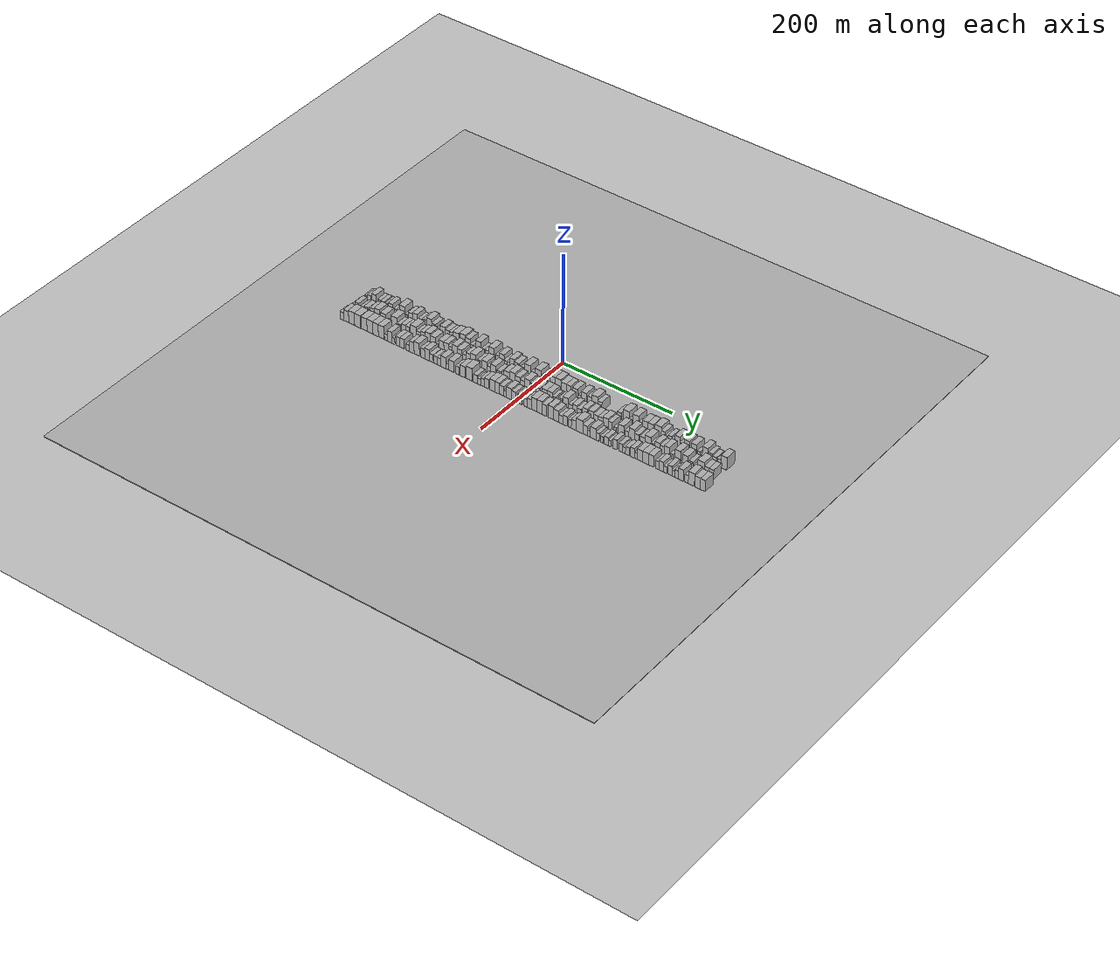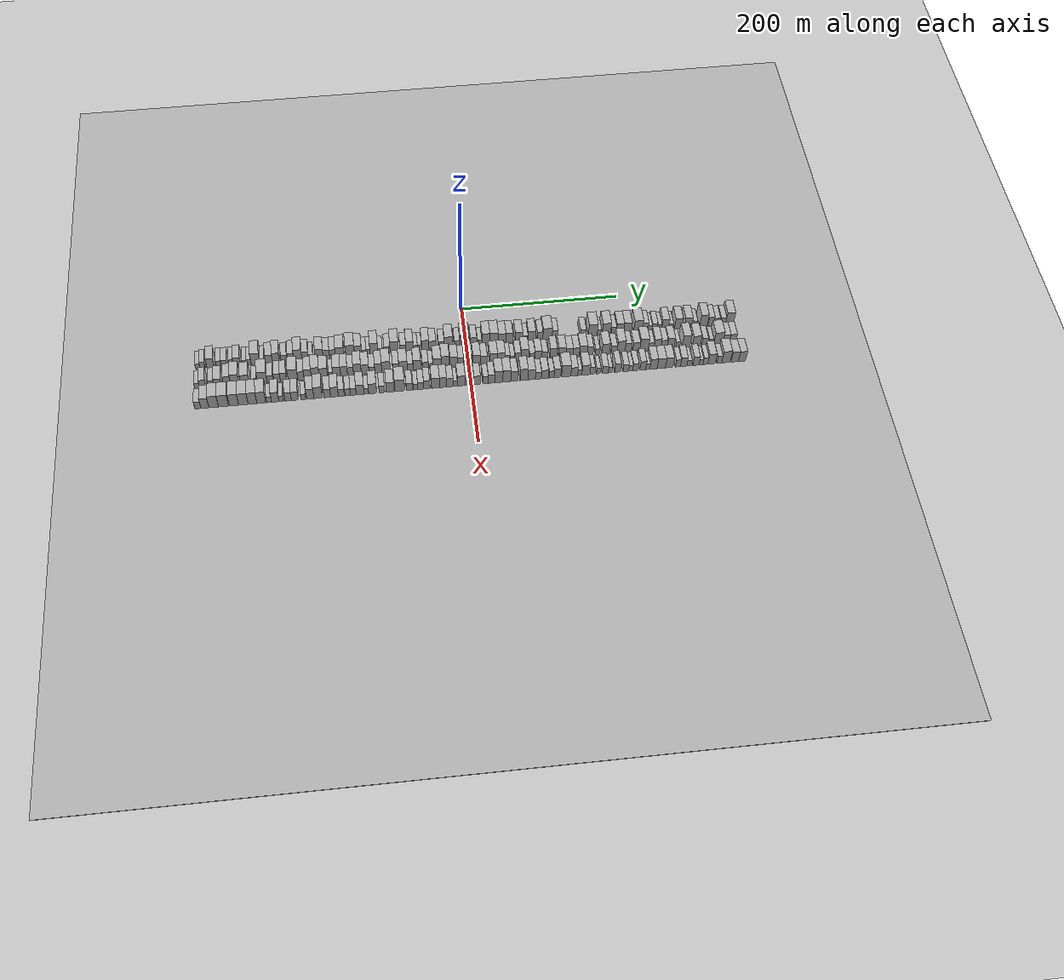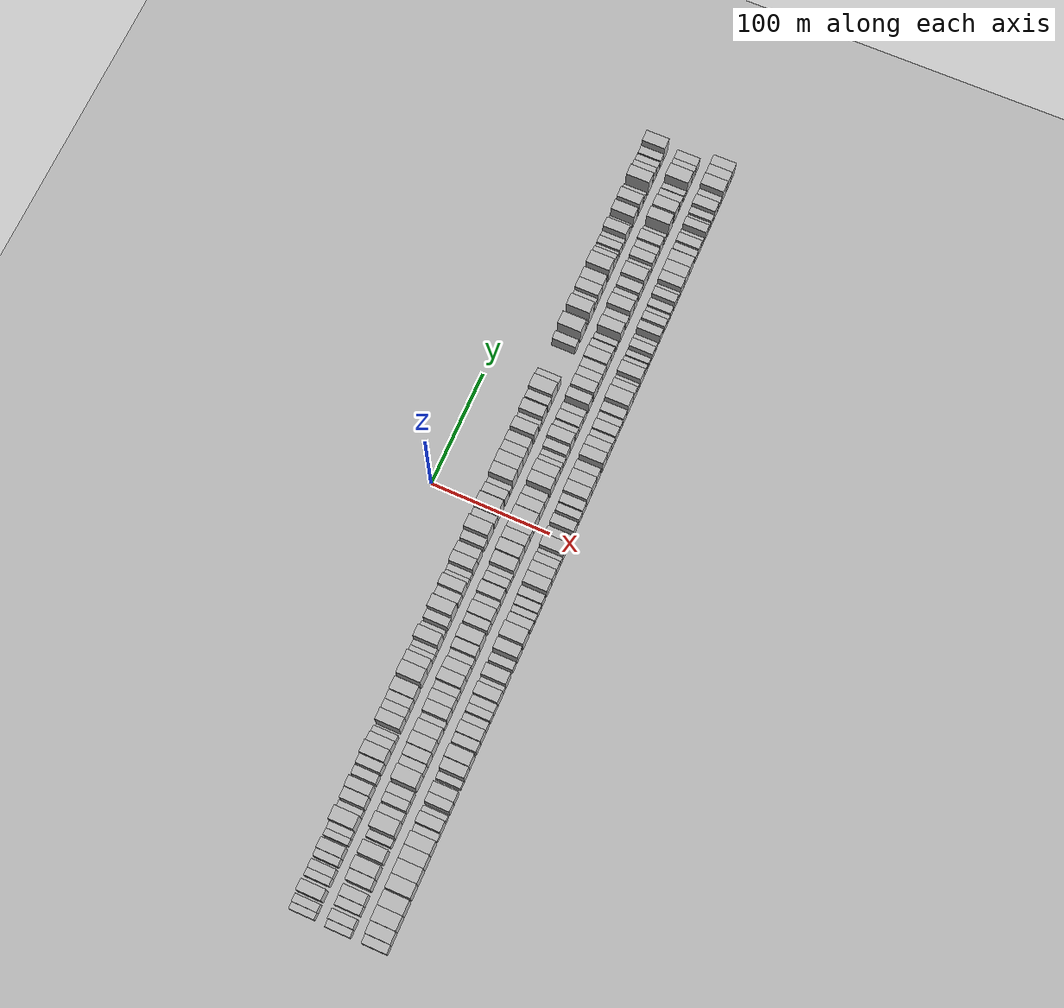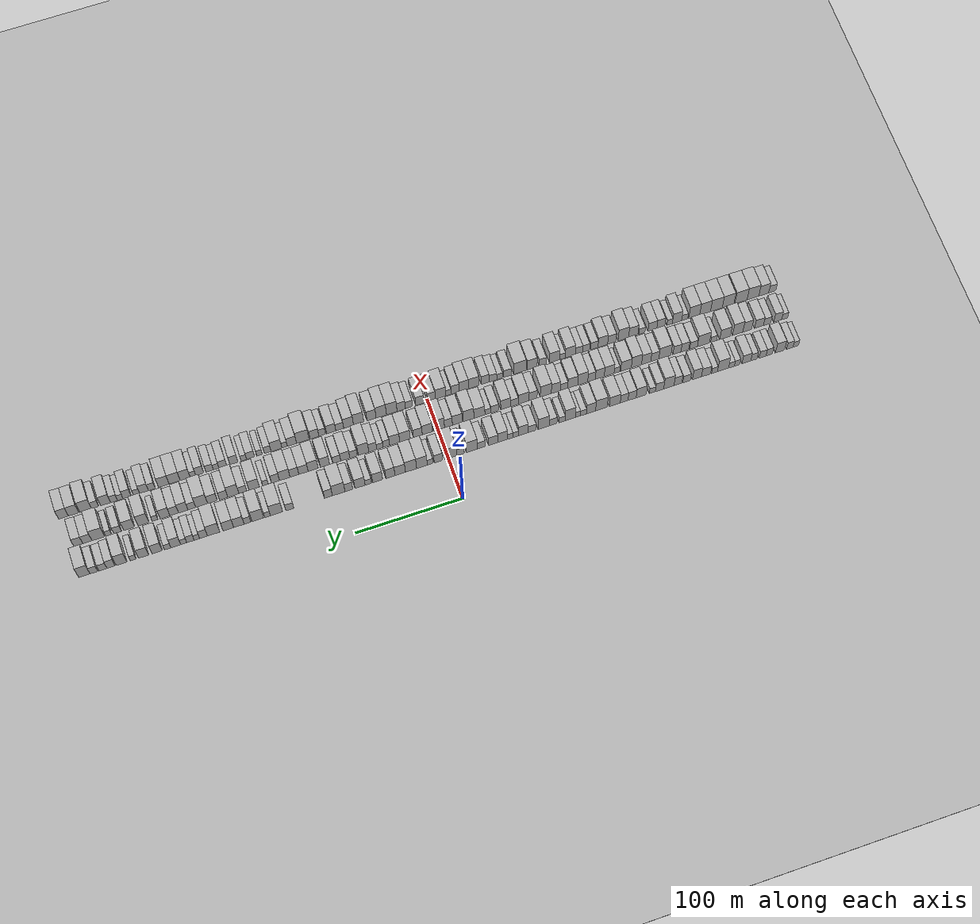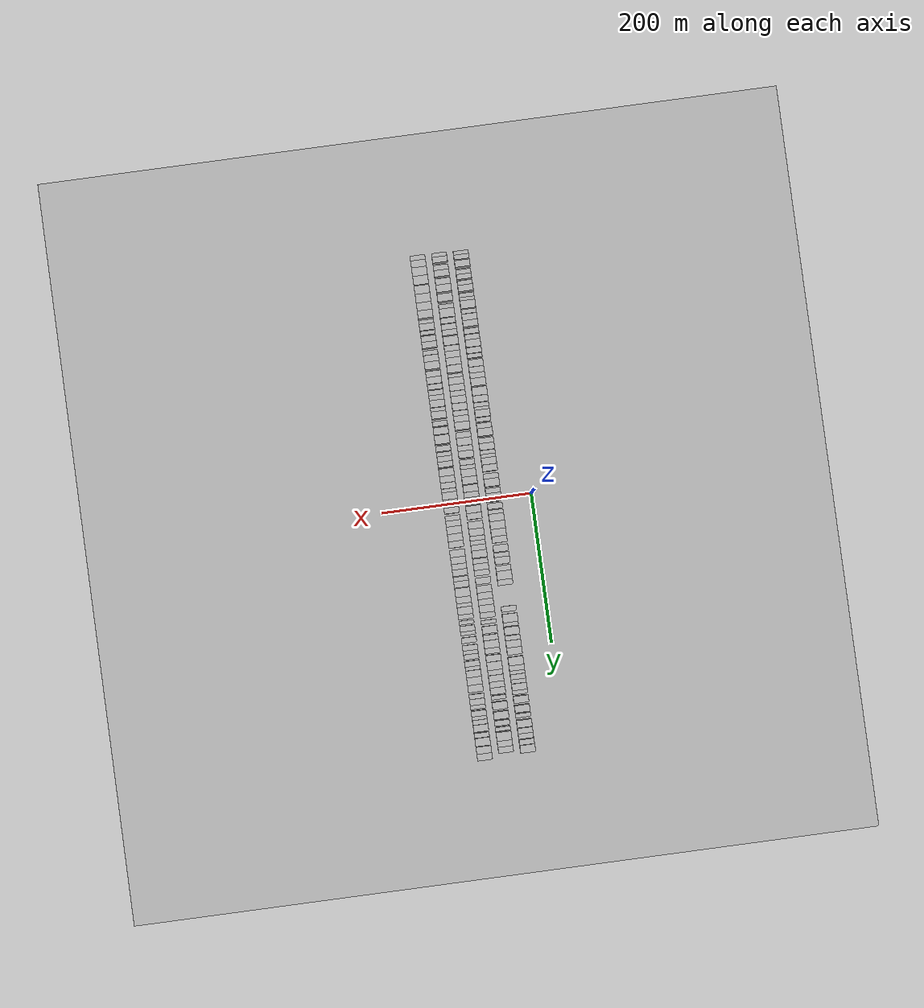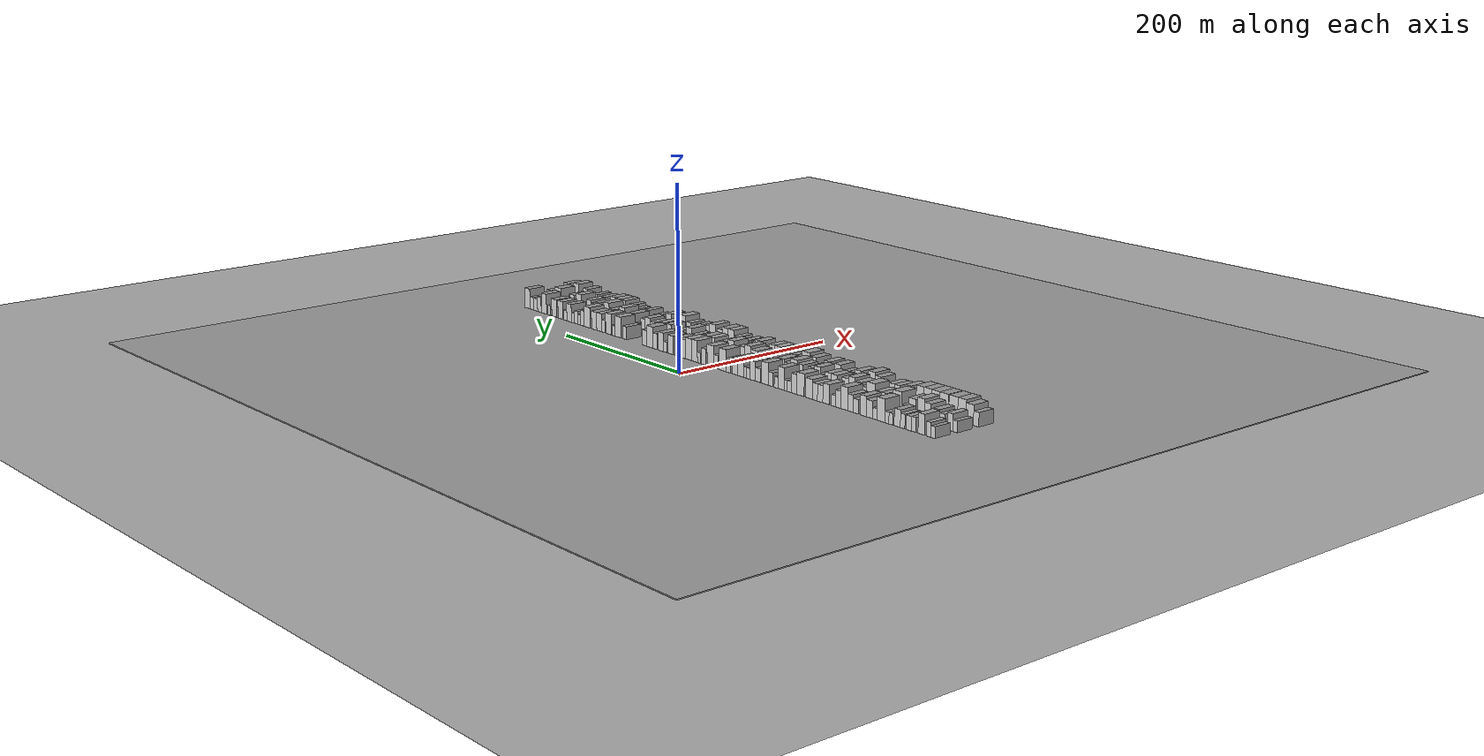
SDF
<?xml version="1.0" encoding="utf-8"?>

<sdf version="1.6">

   <world name="default">

      <gui fullscreen="0">

         <camera name="user_camera">

            <pose>-15 0 4.57585 0 0 0</pose>

            <view_controller>orbit</view_controller>

         </camera>

      </gui>

      <scene>

         <sky>

           <clouds>

             <speed>12</speed>

           </clouds>

         </sky>

         <ambient>0.4 0.4 0.4 1</ambient>

         <background>0.7 0.7 0.7 1</background>

         <shadows>1</shadows>

      </scene>

      <gravity>0 0 -9.8066</gravity>

      <magnetic_field>6e-06 2.3e-05 -4.2e-05</magnetic_field>

      <physics default="0" name="default_physics" type="ode">

         <ode>

            <solver>

               <type>quick</type>

               <iters>10</iters>

               <sor>1.0</sor>

               <use_dynamic_moi_rescaling>0</use_dynamic_moi_rescaling>

            </solver>

            <constraints>

               <cfm>0</cfm>

               <erp>0.2</erp>

               <contact_max_correcting_vel>100</contact_max_correcting_vel>

               <contact_surface_layer>0.001</contact_surface_layer>

            </constraints>

         </ode>

         <max_step_size>0.004</max_step_size>

         <real_time_factor>1</real_time_factor>

         <real_time_update_rate>250</real_time_update_rate>

      </physics>

      <light name="sun" type="directional">

         <cast_shadows>1</cast_shadows>

         <pose>0 0 10 0 0 0</pose>

         <diffuse>0.8 0.8 0.8 1</diffuse>

         <specular>0.2 0.2 0.2 1</specular>

         <attenuation>

            <range>1000</range>

            <constant>0.9</constant>

            <linear>0.01</linear>

            <quadratic>0.001</quadratic>

         </attenuation>

         <direction>-0.5 0.1 -0.9</direction>

      </light>

      <include>

         <name>ground_plane_1</name>

         <uri>model://HANNAS_ground_plane</uri>

         <pose>0 0 0  0 0 0</pose>

      </include>

      <include>

         <name>ground_plane_2</name>

         <uri>model://HANNAS_ground_plane</uri>

         <pose>100 0 0  0 0 0</pose>

      </include>

      <model name="building_1">

         <static>1</static>

         <pose frame="">50.0000 -332.3124 0 0.000000 0.000000 0.000000</pose>

         <link name="link">

            <pose frame="">0 0 6.00 0 0 0</pose>

            <collision name="collision">

               <geometry>

                  <box>

                     <size>20.0000 5.3752 12.0000</size>

                  </box>

               </geometry>

               <max_contacts>10</max_contacts>

               <surface>

                  <contact>

                     <ode/>

                  </contact>

                  <bounce/>

                  <friction>

                     <torsional>

                        <ode/>

                     </torsional>

                     <ode/>

                  </friction>

               </surface>

            </collision>

            <visual name="visual">

               <cast_shadows>0</cast_shadows>

               <geometry>

                  <box>

                     <size>20.0000 5.3752 12.0000</size>

                  </box>

               </geometry>

               <material>

                  <script>

                     <uri>model://HANNAS_wall/materials/scripts</uri>

                     <uri>model://HANNAS_wall/materials/textures</uri>

                     <name>vrc/HANNAS_wall</name>

                  </script>

               </material>

            </visual>

            <self_collide>0</self_collide>

            <enable_wind>0</enable_wind>

            <kinematic>0</kinematic>

         </link>

      </model>

      <model name="building_2">

         <static>1</static>

         <pose frame="">50.0000 -326.4611 0 0.000000 0.000000 0.000000</pose>

         <link name="link">

            <pose frame="">0 0 7.50 0 0 0</pose>

            <collision name="collision">

               <geometry>

                  <box>

                     <size>20.0000 6.3274 15.0000</size>

                  </box>

               </geometry>

               <max_contacts>10</max_contacts>

               <surface>

                  <contact>

                     <ode/>

                  </contact>

                  <bounce/>

                  <friction>

                     <torsional>

                        <ode/>

                     </torsional>

                     <ode/>

                  </friction>

               </surface>

            </collision>

            <visual name="visual">

               <cast_shadows>0</cast_shadows>

               <geometry>

                  <box>

                     <size>20.0000 6.3274 15.0000</size>

                  </box>

               </geometry>

               <material>

                  <script>

                     <uri>model://HANNAS_wall/materials/scripts</uri>

                     <uri>model://HANNAS_wall/materials/textures</uri>

                     <name>vrc/HANNAS_wall</name>

                  </script>

               </material>

            </visual>

            <self_collide>0</self_collide>

            <enable_wind>0</enable_wind>

            <kinematic>0</kinematic>

         </link>

      </model>

      <model name="building_3">

         <static>1</static>

         <pose frame="">50.0000 -316.8551 0 0.000000 0.000000 0.000000</pose>

         <link name="link">

            <pose frame="">0 0 10.50 0 0 0</pose>

            <collision name="collision">

               <geometry>

                  <box>

                     <size>20.0000 8.8847 21.0000</size>

                  </box>

               </geometry>

               <max_contacts>10</max_contacts>

               <surface>

                  <contact>

                     <ode/>

                  </contact>

                  <bounce/>

                  <friction>

                     <torsional>

                        <ode/>

                     </torsional>

                     <ode/>

                  </friction>

               </surface>

            </collision>

            <visual name="visual">

               <cast_shadows>0</cast_shadows>

               <geometry>

                  <box>

                     <size>20.0000 8.8847 21.0000</size>

                  </box>

               </geometry>

               <material>

                  <script>

                     <uri>model://HANNAS_wall/materials/scripts</uri>

                     <uri>model://HANNAS_wall/materials/textures</uri>

                     <name>vrc/HANNAS_wall</name>

                  </script>

               </material>

            </visual>

            <self_collide>0</self_collide>

            <enable_wind>0</enable_wind>

            <kinematic>0</kinematic>

         </link>

      </model>

      <model name="building_4">

         <static>1</static>

         <pose frame="">50.0000 -306.3865 0 0.000000 0.000000 0.000000</pose>

         <link name="link">

            <pose frame="">0 0 7.50 0 0 0</pose>

            <collision name="collision">

               <geometry>

                  <box>

                     <size>20.0000 6.0524 15.0000</size>

                  </box>

               </geometry>

               <max_contacts>10</max_contacts>

               <surface>

                  <contact>

                     <ode/>

                  </contact>

                  <bounce/>

                  <friction>

                     <torsional>

                        <ode/>

                     </torsional>

                     <ode/>

                  </friction>

               </surface>

            </collision>

            <visual name="visual">

               <cast_shadows>0</cast_shadows>

               <geometry>

                  <box>

                     <size>20.0000 6.0524 15.0000</size>

                  </box>

               </geometry>

               <material>

                  <script>

                     <uri>model://HANNAS_wall/materials/scripts</uri>

                     <uri>model://HANNAS_wall/materials/textures</uri>

                     <name>vrc/HANNAS_wall</name>

                  </script>

               </material>

            </visual>

            <self_collide>0</self_collide>

            <enable_wind>0</enable_wind>

            <kinematic>0</kinematic>

         </link>

      </model>

      <model name="building_5">

         <static>1</static>

         <pose frame="">50.0000 -299.9260 0 0.000000 0.000000 0.000000</pose>

         <link name="link">

            <pose frame="">0 0 7.50 0 0 0</pose>

            <collision name="collision">

               <geometry>

                  <box>

                     <size>20.0000 6.8686 15.0000</size>

                  </box>

               </geometry>

               <max_contacts>10</max_contacts>

               <surface>

                  <contact>

                     <ode/>

                  </contact>

                  <bounce/>

                  <friction>

                     <torsional>

                        <ode/>

                     </torsional>

                     <ode/>

                  </friction>

               </surface>

            </collision>

            <visual name="visual">

               <cast_shadows>0</cast_shadows>

               <geometry>

                  <box>

                     <size>20.0000 6.8686 15.0000</size>

                  </box>

               </geometry>

               <material>

                  <script>

                     <uri>model://HANNAS_wall/materials/scripts</uri>

                     <uri>model://HANNAS_wall/materials/textures</uri>

                     <name>vrc/HANNAS_wall</name>

                  </script>

               </material>

            </visual>

            <self_collide>0</self_collide>

            <enable_wind>0</enable_wind>

            <kinematic>0</kinematic>

         </link>

      </model>

      <model name="building_6">

         <static>1</static>

         <pose frame="">50.0000 -291.4294 0 0.000000 0.000000 0.000000</pose>

         <link name="link">

            <pose frame="">0 0 7.50 0 0 0</pose>

            <collision name="collision">

               <geometry>

                  <box>

                     <size>20.0000 6.1247 15.0000</size>

                  </box>

               </geometry>

               <max_contacts>10</max_contacts>

               <surface>

                  <contact>

                     <ode/>

                  </contact>

                  <bounce/>

                  <friction>

                     <torsional>

                        <ode/>

                     </torsional>

                     <ode/>

                  </friction>

               </surface>

            </collision>

            <visual name="visual">

               <cast_shadows>0</cast_shadows>

               <geometry>

                  <box>

                     <size>20.0000 6.1247 15.0000</size>

                  </box>

               </geometry>

               <material>

                  <script>

                     <uri>model://HANNAS_wall/materials/scripts</uri>

                     <uri>model://HANNAS_wall/materials/textures</uri>

                     <name>vrc/HANNAS_wall</name>

                  </script>

               </material>

            </visual>

            <self_collide>0</self_collide>

            <enable_wind>0</enable_wind>

            <kinematic>0</kinematic>

         </link>

      </model>

      <model name="building_7">

         <static>1</static>

         <pose frame="">50.0000 -284.0968 0 0.000000 0.000000 0.000000</pose>

         <link name="link">

            <pose frame="">0 0 9.00 0 0 0</pose>

            <collision name="collision">

               <geometry>

                  <box>

                     <size>20.0000 8.5404 18.0000</size>

                  </box>

               </geometry>

               <max_contacts>10</max_contacts>

               <surface>

                  <contact>

                     <ode/>

                  </contact>

                  <bounce/>

                  <friction>

                     <torsional>

                        <ode/>

                     </torsional>

                     <ode/>

                  </friction>

               </surface>

            </collision>

            <visual name="visual">

               <cast_shadows>0</cast_shadows>

               <geometry>

                  <box>

                     <size>20.0000 8.5404 18.0000</size>

                  </box>

               </geometry>

               <material>

                  <script>

                     <uri>model://HANNAS_wall/materials/scripts</uri>

                     <uri>model://HANNAS_wall/materials/textures</uri>

                     <name>vrc/HANNAS_wall</name>

                  </script>

               </material>

            </visual>

            <self_collide>0</self_collide>

            <enable_wind>0</enable_wind>

            <kinematic>0</kinematic>

         </link>

      </model>

      <model name="building_8">

         <static>1</static>

         <pose frame="">50.0000 -275.1742 0 0.000000 0.000000 0.000000</pose>

         <link name="link">

            <pose frame="">0 0 6.00 0 0 0</pose>

            <collision name="collision">

               <geometry>

                  <box>

                     <size>20.0000 5.3046 12.0000</size>

                  </box>

               </geometry>

               <max_contacts>10</max_contacts>

               <surface>

                  <contact>

                     <ode/>

                  </contact>

                  <bounce/>

                  <friction>

                     <torsional>

                        <ode/>

                     </torsional>

                     <ode/>

                  </friction>

               </surface>

            </collision>

            <visual name="visual">

               <cast_shadows>0</cast_shadows>

               <geometry>

                  <box>

                     <size>20.0000 5.3046 12.0000</size>

                  </box>

               </geometry>

               <material>

                  <script>

                     <uri>model://HANNAS_wall/materials/scripts</uri>

                     <uri>model://HANNAS_wall/materials/textures</uri>

                     <name>vrc/HANNAS_wall</name>

                  </script>

               </material>

            </visual>

            <self_collide>0</self_collide>

            <enable_wind>0</enable_wind>

            <kinematic>0</kinematic>

         </link>

      </model>

      <model name="building_9">

         <static>1</static>

         <pose frame="">50.0000 -269.6709 0 0.000000 0.000000 0.000000</pose>

         <link name="link">

            <pose frame="">0 0 6.00 0 0 0</pose>

            <collision name="collision">

               <geometry>

                  <box>

                     <size>20.0000 5.7021 12.0000</size>

                  </box>

               </geometry>

               <max_contacts>10</max_contacts>

               <surface>

                  <contact>

                     <ode/>

                  </contact>

                  <bounce/>

                  <friction>

                     <torsional>

                        <ode/>

                     </torsional>

                     <ode/>

                  </friction>

               </surface>

            </collision>

            <visual name="visual">

               <cast_shadows>0</cast_shadows>

               <geometry>

                  <box>

                     <size>20.0000 5.7021 12.0000</size>

                  </box>

               </geometry>

               <material>

                  <script>

                     <uri>model://HANNAS_wall/materials/scripts</uri>

                     <uri>model://HANNAS_wall/materials/textures</uri>

                     <name>vrc/HANNAS_wall</name>

                  </script>

               </material>

            </visual>

            <self_collide>0</self_collide>

            <enable_wind>0</enable_wind>

            <kinematic>0</kinematic>

         </link>

      </model>

      <model name="building_10">

         <static>1</static>

         <pose frame="">50.0000 -261.4165 0 0.000000 0.000000 0.000000</pose>

         <link name="link">

            <pose frame="">0 0 12.00 0 0 0</pose>

            <collision name="collision">

               <geometry>

                  <box>

                     <size>20.0000 10.8067 24.0000</size>

                  </box>

               </geometry>

               <max_contacts>10</max_contacts>

               <surface>

                  <contact>

                     <ode/>

                  </contact>

                  <bounce/>

                  <friction>

                     <torsional>

                        <ode/>

                     </torsional>

                     <ode/>

                  </friction>

               </surface>

            </collision>

            <visual name="visual">

               <cast_shadows>0</cast_shadows>

               <geometry>

                  <box>

                     <size>20.0000 10.8067 24.0000</size>

                  </box>

               </geometry>

               <material>

                  <script>

                     <uri>model://HANNAS_wall/materials/scripts</uri>

                     <uri>model://HANNAS_wall/materials/textures</uri>

                     <name>vrc/HANNAS_wall</name>

                  </script>

               </material>

            </visual>

            <self_collide>0</self_collide>

            <enable_wind>0</enable_wind>

            <kinematic>0</kinematic>

         </link>

      </model>

      <model name="building_11">

         <static>1</static>

         <pose frame="">50.0000 -253.1574 0 0.000000 0.000000 0.000000</pose>

         <link name="link">

            <pose frame="">0 0 6.00 0 0 0</pose>

            <collision name="collision">

               <geometry>

                  <box>

                     <size>20.0000 5.7115 12.0000</size>

                  </box>

               </geometry>

               <max_contacts>10</max_contacts>

               <surface>

                  <contact>

                     <ode/>

                  </contact>

                  <bounce/>

                  <friction>

                     <torsional>

                        <ode/>

                     </torsional>

                     <ode/>

                  </friction>

               </surface>

            </collision>

            <visual name="visual">

               <cast_shadows>0</cast_shadows>

               <geometry>

                  <box>

                     <size>20.0000 5.7115 12.0000</size>

                  </box>

               </geometry>

               <material>

                  <script>

                     <uri>model://HANNAS_wall/materials/scripts</uri>

                     <uri>model://HANNAS_wall/materials/textures</uri>

                     <name>vrc/HANNAS_wall</name>

                  </script>

               </material>

            </visual>

            <self_collide>0</self_collide>

            <enable_wind>0</enable_wind>

            <kinematic>0</kinematic>

         </link>

      </model>

      <model name="building_12">

         <static>1</static>

         <pose frame="">50.0000 -244.9199 0 0.000000 0.000000 0.000000</pose>

         <link name="link">

            <pose frame="">0 0 9.00 0 0 0</pose>

            <collision name="collision">

               <geometry>

                  <box>

                     <size>20.0000 8.7636 18.0000</size>

                  </box>

               </geometry>

               <max_contacts>10</max_contacts>

               <surface>

                  <contact>

                     <ode/>

                  </contact>

                  <bounce/>

                  <friction>

                     <torsional>

                        <ode/>

                     </torsional>

                     <ode/>

                  </friction>

               </surface>

            </collision>

            <visual name="visual">

               <cast_shadows>0</cast_shadows>

               <geometry>

                  <box>

                     <size>20.0000 8.7636 18.0000</size>

                  </box>

               </geometry>

               <material>

                  <script>

                     <uri>model://HANNAS_wall/materials/scripts</uri>

                     <uri>model://HANNAS_wall/materials/textures</uri>

                     <name>vrc/HANNAS_wall</name>

                  </script>

               </material>

            </visual>

            <self_collide>0</self_collide>

            <enable_wind>0</enable_wind>

            <kinematic>0</kinematic>

         </link>

      </model>

      <model name="building_13">

         <static>1</static>

         <pose frame="">50.0000 -236.2172 0 0.000000 0.000000 0.000000</pose>

         <link name="link">

            <pose frame="">0 0 10.50 0 0 0</pose>

            <collision name="collision">

               <geometry>

                  <box>

                     <size>20.0000 8.6419 21.0000</size>

                  </box>

               </geometry>

               <max_contacts>10</max_contacts>

               <surface>

                  <contact>

                     <ode/>

                  </contact>

                  <bounce/>

                  <friction>

                     <torsional>

                        <ode/>

                     </torsional>

                     <ode/>

                  </friction>

               </surface>

            </collision>

            <visual name="visual">

               <cast_shadows>0</cast_shadows>

               <geometry>

                  <box>

                     <size>20.0000 8.6419 21.0000</size>

                  </box>

               </geometry>

               <material>

                  <script>

                     <uri>model://HANNAS_wall/materials/scripts</uri>

                     <uri>model://HANNAS_wall/materials/textures</uri>

                     <name>vrc/HANNAS_wall</name>

                  </script>

               </material>

            </visual>

            <self_collide>0</self_collide>

            <enable_wind>0</enable_wind>

            <kinematic>0</kinematic>

         </link>

      </model>

      <model name="building_14">

         <static>1</static>

         <pose frame="">50.0000 -226.2492 0 0.000000 0.000000 0.000000</pose>

         <link name="link">

            <pose frame="">0 0 7.50 0 0 0</pose>

            <collision name="collision">

               <geometry>

                  <box>

                     <size>20.0000 7.2940 15.0000</size>

                  </box>

               </geometry>

               <max_contacts>10</max_contacts>

               <surface>

                  <contact>

                     <ode/>

                  </contact>

                  <bounce/>

                  <friction>

                     <torsional>

                        <ode/>

                     </torsional>

                     <ode/>

                  </friction>

               </surface>

            </collision>

            <visual name="visual">

               <cast_shadows>0</cast_shadows>

               <geometry>

                  <box>

                     <size>20.0000 7.2940 15.0000</size>

                  </box>

               </geometry>

               <material>

                  <script>

                     <uri>model://HANNAS_wall/materials/scripts</uri>

                     <uri>model://HANNAS_wall/materials/textures</uri>

                     <name>vrc/HANNAS_wall</name>

                  </script>

               </material>

            </visual>

            <self_collide>0</self_collide>

            <enable_wind>0</enable_wind>

            <kinematic>0</kinematic>

         </link>

      </model>

      <model name="building_15">

         <static>1</static>

         <pose frame="">50.0000 -217.8523 0 0.000000 0.000000 0.000000</pose>

         <link name="link">

            <pose frame="">0 0 9.00 0 0 0</pose>

            <collision name="collision">

               <geometry>

                  <box>

                     <size>20.0000 7.4997 18.0000</size>

                  </box>

               </geometry>

               <max_contacts>10</max_contacts>

               <surface>

                  <contact>

                     <ode/>

                  </contact>

                  <bounce/>

                  <friction>

                     <torsional>

                        <ode/>

                     </torsional>

                     <ode/>

                  </friction>

               </surface>

            </collision>

            <visual name="visual">

               <cast_shadows>0</cast_shadows>

               <geometry>

                  <box>

                     <size>20.0000 7.4997 18.0000</size>

                  </box>

               </geometry>

               <material>

                  <script>

                     <uri>model://HANNAS_wall/materials/scripts</uri>

                     <uri>model://HANNAS_wall/materials/textures</uri>

                     <name>vrc/HANNAS_wall</name>

                  </script>

               </material>

            </visual>

            <self_collide>0</self_collide>

            <enable_wind>0</enable_wind>

            <kinematic>0</kinematic>

         </link>

      </model>

      <model name="building_16">

         <static>1</static>

         <pose frame="">50.0000 -209.1032 0 0.000000 0.000000 0.000000</pose>

         <link name="link">

            <pose frame="">0 0 12.00 0 0 0</pose>

            <collision name="collision">

               <geometry>

                  <box>

                     <size>20.0000 9.9984 24.0000</size>

                  </box>

               </geometry>

               <max_contacts>10</max_contacts>

               <surface>

                  <contact>

                     <ode/>

                  </contact>

                  <bounce/>

                  <friction>

                     <torsional>

                        <ode/>

                     </torsional>

                     <ode/>

                  </friction>

               </surface>

            </collision>

            <visual name="visual">

               <cast_shadows>0</cast_shadows>

               <geometry>

                  <box>

                     <size>20.0000 9.9984 24.0000</size>

                  </box>

               </geometry>

               <material>

                  <script>

                     <uri>model://HANNAS_wall/materials/scripts</uri>

                     <uri>model://HANNAS_wall/materials/textures</uri>

                     <name>vrc/HANNAS_wall</name>

                  </script>

               </material>

            </visual>

            <self_collide>0</self_collide>

            <enable_wind>0</enable_wind>

            <kinematic>0</kinematic>

         </link>

      </model>

      <model name="building_17">

         <static>1</static>

         <pose frame="">50.0000 -200.1259 0 0.000000 0.000000 0.000000</pose>

         <link name="link">

            <pose frame="">0 0 9.00 0 0 0</pose>

            <collision name="collision">

               <geometry>

                  <box>

                     <size>20.0000 7.9562 18.0000</size>

                  </box>

               </geometry>

               <max_contacts>10</max_contacts>

               <surface>

                  <contact>

                     <ode/>

                  </contact>

                  <bounce/>

                  <friction>

                     <torsional>

                        <ode/>

                     </torsional>

                     <ode/>

                  </friction>

               </surface>

            </collision>

            <visual name="visual">

               <cast_shadows>0</cast_shadows>

               <geometry>

                  <box>

                     <size>20.0000 7.9562 18.0000</size>

                  </box>

               </geometry>

               <material>

                  <script>

                     <uri>model://HANNAS_wall/materials/scripts</uri>

                     <uri>model://HANNAS_wall/materials/textures</uri>

                     <name>vrc/HANNAS_wall</name>

                  </script>

               </material>

            </visual>

            <self_collide>0</self_collide>

            <enable_wind>0</enable_wind>

            <kinematic>0</kinematic>

         </link>

      </model>

      <model name="building_18">

         <static>1</static>

         <pose frame="">50.0000 -193.2746 0 0.000000 0.000000 0.000000</pose>

         <link name="link">

            <pose frame="">0 0 6.00 0 0 0</pose>

            <collision name="collision">

               <geometry>

                  <box>

                     <size>20.0000 5.7465 12.0000</size>

                  </box>

               </geometry>

               <max_contacts>10</max_contacts>

               <surface>

                  <contact>

                     <ode/>

                  </contact>

                  <bounce/>

                  <friction>

                     <torsional>

                        <ode/>

                     </torsional>

                     <ode/>

                  </friction>

               </surface>

            </collision>

            <visual name="visual">

               <cast_shadows>0</cast_shadows>

               <geometry>

                  <box>

                     <size>20.0000 5.7465 12.0000</size>

                  </box>

               </geometry>

               <material>

                  <script>

                     <uri>model://HANNAS_wall/materials/scripts</uri>

                     <uri>model://HANNAS_wall/materials/textures</uri>

                     <name>vrc/HANNAS_wall</name>

                  </script>

               </material>

            </visual>

            <self_collide>0</self_collide>

            <enable_wind>0</enable_wind>

            <kinematic>0</kinematic>

         </link>

      </model>

      <model name="building_19">

         <static>1</static>

         <pose frame="">50.0000 -182.5983 0 0.000000 0.000000 0.000000</pose>

         <link name="link">

            <pose frame="">0 0 10.50 0 0 0</pose>

            <collision name="collision">

               <geometry>

                  <box>

                     <size>20.0000 9.6061 21.0000</size>

                  </box>

               </geometry>

               <max_contacts>10</max_contacts>

               <surface>

                  <contact>

                     <ode/>

                  </contact>

                  <bounce/>

                  <friction>

                     <torsional>

                        <ode/>

                     </torsional>

                     <ode/>

                  </friction>

               </surface>

            </collision>

            <visual name="visual">

               <cast_shadows>0</cast_shadows>

               <geometry>

                  <box>

                     <size>20.0000 9.6061 21.0000</size>

                  </box>

               </geometry>

               <material>

                  <script>

                     <uri>model://HANNAS_wall/materials/scripts</uri>

                     <uri>model://HANNAS_wall/materials/textures</uri>

                     <name>vrc/HANNAS_wall</name>

                  </script>

               </material>

            </visual>

            <self_collide>0</self_collide>

            <enable_wind>0</enable_wind>

            <kinematic>0</kinematic>

         </link>

      </model>

      <model name="building_20">

         <static>1</static>

         <pose frame="">50.0000 -173.8502 0 0.000000 0.000000 0.000000</pose>

         <link name="link">

            <pose frame="">0 0 9.00 0 0 0</pose>

            <collision name="collision">

               <geometry>

                  <box>

                     <size>20.0000 7.8902 18.0000</size>

                  </box>

               </geometry>

               <max_contacts>10</max_contacts>

               <surface>

                  <contact>

                     <ode/>

                  </contact>

                  <bounce/>

                  <friction>

                     <torsional>

                        <ode/>

                     </torsional>

                     <ode/>

                  </friction>

               </surface>

            </collision>

            <visual name="visual">

               <cast_shadows>0</cast_shadows>

               <geometry>

                  <box>

                     <size>20.0000 7.8902 18.0000</size>

                  </box>

               </geometry>

               <material>

                  <script>

                     <uri>model://HANNAS_wall/materials/scripts</uri>

                     <uri>model://HANNAS_wall/materials/textures</uri>

                     <name>vrc/HANNAS_wall</name>

                  </script>

               </material>

            </visual>

            <self_collide>0</self_collide>

            <enable_wind>0</enable_wind>

            <kinematic>0</kinematic>

         </link>

      </model>

      <model name="building_21">

         <static>1</static>

         <pose frame="">50.0000 -166.2073 0 0.000000 0.000000 0.000000</pose>

         <link name="link">

            <pose frame="">0 0 9.00 0 0 0</pose>

            <collision name="collision">

               <geometry>

                  <box>

                     <size>20.0000 7.3956 18.0000</size>

                  </box>

               </geometry>

               <max_contacts>10</max_contacts>

               <surface>

                  <contact>

                     <ode/>

                  </contact>

                  <bounce/>

                  <friction>

                     <torsional>

                        <ode/>

                     </torsional>

                     <ode/>

                  </friction>

               </surface>

            </collision>

            <visual name="visual">

               <cast_shadows>0</cast_shadows>

               <geometry>

                  <box>

                     <size>20.0000 7.3956 18.0000</size>

                  </box>

               </geometry>

               <material>

                  <script>

                     <uri>model://HANNAS_wall/materials/scripts</uri>

                     <uri>model://HANNAS_wall/materials/textures</uri>

                     <name>vrc/HANNAS_wall</name>

                  </script>

               </material>

            </visual>

            <self_collide>0</self_collide>

            <enable_wind>0</enable_wind>

            <kinematic>0</kinematic>

         </link>

      </model>

      <model name="building_22">

         <static>1</static>

         <pose frame="">50.0000 -157.2768 0 0.000000 0.000000 0.000000</pose>

         <link name="link">

            <pose frame="">0 0 10.50 0 0 0</pose>

            <collision name="collision">

               <geometry>

                  <box>

                     <size>20.0000 10.4653 21.0000</size>

                  </box>

               </geometry>

               <max_contacts>10</max_contacts>

               <surface>

                  <contact>

                     <ode/>

                  </contact>

                  <bounce/>

                  <friction>

                     <torsional>

                        <ode/>

                     </torsional>

                     <ode/>

                  </friction>

               </surface>

            </collision>

            <visual name="visual">

               <cast_shadows>0</cast_shadows>

               <geometry>

                  <box>

                     <size>20.0000 10.4653 21.0000</size>

                  </box>

               </geometry>

               <material>

                  <script>

                     <uri>model://HANNAS_wall/materials/scripts</uri>

                     <uri>model://HANNAS_wall/materials/textures</uri>

                     <name>vrc/HANNAS_wall</name>

                  </script>

               </material>

            </visual>

            <self_collide>0</self_collide>

            <enable_wind>0</enable_wind>

            <kinematic>0</kinematic>

         </link>

      </model>

      <model name="building_23">

         <static>1</static>

         <pose frame="">50.0000 -144.4714 0 0.000000 0.000000 0.000000</pose>

         <link name="link">

            <pose frame="">0 0 12.00 0 0 0</pose>

            <collision name="collision">

               <geometry>

                  <box>

                     <size>20.0000 11.1454 24.0000</size>

                  </box>

               </geometry>

               <max_contacts>10</max_contacts>

               <surface>

                  <contact>

                     <ode/>

                  </contact>

                  <bounce/>

                  <friction>

                     <torsional>

                        <ode/>

                     </torsional>

                     <ode/>

                  </friction>

               </surface>

            </collision>

            <visual name="visual">

               <cast_shadows>0</cast_shadows>

               <geometry>

                  <box>

                     <size>20.0000 11.1454 24.0000</size>

                  </box>

               </geometry>

               <material>

                  <script>

                     <uri>model://HANNAS_wall/materials/scripts</uri>

                     <uri>model://HANNAS_wall/materials/textures</uri>

                     <name>vrc/HANNAS_wall</name>

                  </script>

               </material>

            </visual>

            <self_collide>0</self_collide>

            <enable_wind>0</enable_wind>

            <kinematic>0</kinematic>

         </link>

      </model>

      <model name="building_24">

         <static>1</static>

         <pose frame="">50.0000 -134.5044 0 0.000000 0.000000 0.000000</pose>

         <link name="link">

            <pose frame="">0 0 10.50 0 0 0</pose>

            <collision name="collision">

               <geometry>

                  <box>

                     <size>20.0000 8.7886 21.0000</size>

                  </box>

               </geometry>

               <max_contacts>10</max_contacts>

               <surface>

                  <contact>

                     <ode/>

                  </contact>

                  <bounce/>

                  <friction>

                     <torsional>

                        <ode/>

                     </torsional>

                     <ode/>

                  </friction>

               </surface>

            </collision>

            <visual name="visual">

               <cast_shadows>0</cast_shadows>

               <geometry>

                  <box>

                     <size>20.0000 8.7886 21.0000</size>

                  </box>

               </geometry>

               <material>

                  <script>

                     <uri>model://HANNAS_wall/materials/scripts</uri>

                     <uri>model://HANNAS_wall/materials/textures</uri>

                     <name>vrc/HANNAS_wall</name>

                  </script>

               </material>

            </visual>

            <self_collide>0</self_collide>

            <enable_wind>0</enable_wind>

            <kinematic>0</kinematic>

         </link>

      </model>

      <model name="building_25">

         <static>1</static>

         <pose frame="">50.0000 -127.2992 0 0.000000 0.000000 0.000000</pose>

         <link name="link">

            <pose frame="">0 0 6.00 0 0 0</pose>

            <collision name="collision">

               <geometry>

                  <box>

                     <size>20.0000 5.6218 12.0000</size>

                  </box>

               </geometry>

               <max_contacts>10</max_contacts>

               <surface>

                  <contact>

                     <ode/>

                  </contact>

                  <bounce/>

                  <friction>

                     <torsional>

                        <ode/>

                     </torsional>

                     <ode/>

                  </friction>

               </surface>

            </collision>

            <visual name="visual">

               <cast_shadows>0</cast_shadows>

               <geometry>

                  <box>

                     <size>20.0000 5.6218 12.0000</size>

                  </box>

               </geometry>

               <material>

                  <script>

                     <uri>model://HANNAS_wall/materials/scripts</uri>

                     <uri>model://HANNAS_wall/materials/textures</uri>

                     <name>vrc/HANNAS_wall</name>

                  </script>

               </material>

            </visual>

            <self_collide>0</self_collide>

            <enable_wind>0</enable_wind>

            <kinematic>0</kinematic>

         </link>

      </model>

      <model name="building_26">

         <static>1</static>

         <pose frame="">50.0000 -122.0764 0 0.000000 0.000000 0.000000</pose>

         <link name="link">

            <pose frame="">0 0 6.00 0 0 0</pose>

            <collision name="collision">

               <geometry>

                  <box>

                     <size>20.0000 4.8238 12.0000</size>

                  </box>

               </geometry>

               <max_contacts>10</max_contacts>

               <surface>

                  <contact>

                     <ode/>

                  </contact>

                  <bounce/>

                  <friction>

                     <torsional>

                        <ode/>

                     </torsional>

                     <ode/>

                  </friction>

               </surface>

            </collision>

            <visual name="visual">

               <cast_shadows>0</cast_shadows>

               <geometry>

                  <box>

                     <size>20.0000 4.8238 12.0000</size>

                  </box>

               </geometry>

               <material>

                  <script>

                     <uri>model://HANNAS_wall/materials/scripts</uri>

                     <uri>model://HANNAS_wall/materials/textures</uri>

                     <name>vrc/HANNAS_wall</name>

                  </script>

               </material>

            </visual>

            <self_collide>0</self_collide>

            <enable_wind>0</enable_wind>

            <kinematic>0</kinematic>

         </link>

      </model>

      <model name="building_27">

         <static>1</static>

         <pose frame="">50.0000 -114.8184 0 0.000000 0.000000 0.000000</pose>

         <link name="link">

            <pose frame="">0 0 12.00 0 0 0</pose>

            <collision name="collision">

               <geometry>

                  <box>

                     <size>20.0000 9.6922 24.0000</size>

                  </box>

               </geometry>

               <max_contacts>10</max_contacts>

               <surface>

                  <contact>

                     <ode/>

                  </contact>

                  <bounce/>

                  <friction>

                     <torsional>

                        <ode/>

                     </torsional>

                     <ode/>

                  </friction>

               </surface>

            </collision>

            <visual name="visual">

               <cast_shadows>0</cast_shadows>

               <geometry>

                  <box>

                     <size>20.0000 9.6922 24.0000</size>

                  </box>

               </geometry>

               <material>

                  <script>

                     <uri>model://HANNAS_wall/materials/scripts</uri>

                     <uri>model://HANNAS_wall/materials/textures</uri>

                     <name>vrc/HANNAS_wall</name>

                  </script>

               </material>

            </visual>

            <self_collide>0</self_collide>

            <enable_wind>0</enable_wind>

            <kinematic>0</kinematic>

         </link>

      </model>

      <model name="building_28">

         <static>1</static>

         <pose frame="">50.0000 -107.0664 0 0.000000 0.000000 0.000000</pose>

         <link name="link">

            <pose frame="">0 0 6.00 0 0 0</pose>

            <collision name="collision">

               <geometry>

                  <box>

                     <size>20.0000 5.8118 12.0000</size>

                  </box>

               </geometry>

               <max_contacts>10</max_contacts>

               <surface>

                  <contact>

                     <ode/>

                  </contact>

                  <bounce/>

                  <friction>

                     <torsional>

                        <ode/>

                     </torsional>

                     <ode/>

                  </friction>

               </surface>

            </collision>

            <visual name="visual">

               <cast_shadows>0</cast_shadows>

               <geometry>

                  <box>

                     <size>20.0000 5.8118 12.0000</size>

                  </box>

               </geometry>

               <material>

                  <script>

                     <uri>model://HANNAS_wall/materials/scripts</uri>

                     <uri>model://HANNAS_wall/materials/textures</uri>

                     <name>vrc/HANNAS_wall</name>

                  </script>

               </material>

            </visual>

            <self_collide>0</self_collide>

            <enable_wind>0</enable_wind>

            <kinematic>0</kinematic>

         </link>

      </model>

      <model name="building_29">

         <static>1</static>

         <pose frame="">50.0000 -98.4347 0 0.000000 0.000000 0.000000</pose>

         <link name="link">

            <pose frame="">0 0 7.50 0 0 0</pose>

            <collision name="collision">

               <geometry>

                  <box>

                     <size>20.0000 7.4516 15.0000</size>

                  </box>

               </geometry>

               <max_contacts>10</max_contacts>

               <surface>

                  <contact>

                     <ode/>

                  </contact>

                  <bounce/>

                  <friction>

                     <torsional>

                        <ode/>

                     </torsional>

                     <ode/>

                  </friction>

               </surface>

            </collision>

            <visual name="visual">

               <cast_shadows>0</cast_shadows>

               <geometry>

                  <box>

                     <size>20.0000 7.4516 15.0000</size>

                  </box>

               </geometry>

               <material>

                  <script>

                     <uri>model://HANNAS_wall/materials/scripts</uri>

                     <uri>model://HANNAS_wall/materials/textures</uri>

                     <name>vrc/HANNAS_wall</name>

                  </script>

               </material>

            </visual>

            <self_collide>0</self_collide>

            <enable_wind>0</enable_wind>

            <kinematic>0</kinematic>

         </link>

      </model>

      <model name="building_30">

         <static>1</static>

         <pose frame="">50.0000 -89.5122 0 0.000000 0.000000 0.000000</pose>

         <link name="link">

            <pose frame="">0 0 12.00 0 0 0</pose>

            <collision name="collision">

               <geometry>

                  <box>

                     <size>20.0000 10.3935 24.0000</size>

                  </box>

               </geometry>

               <max_contacts>10</max_contacts>

               <surface>

                  <contact>

                     <ode/>

                  </contact>

                  <bounce/>

                  <friction>

                     <torsional>

                        <ode/>

                     </torsional>

                     <ode/>

                  </friction>

               </surface>

            </collision>

            <visual name="visual">

               <cast_shadows>0</cast_shadows>

               <geometry>

                  <box>

                     <size>20.0000 10.3935 24.0000</size>

                  </box>

               </geometry>

               <material>

                  <script>

                     <uri>model://HANNAS_wall/materials/scripts</uri>

                     <uri>model://HANNAS_wall/materials/textures</uri>

                     <name>vrc/HANNAS_wall</name>

                  </script>

               </material>

            </visual>

            <self_collide>0</self_collide>

            <enable_wind>0</enable_wind>

            <kinematic>0</kinematic>

         </link>

      </model>

      <model name="building_31">

         <static>1</static>

         <pose frame="">50.0000 -78.6340 0 0.000000 0.000000 0.000000</pose>

         <link name="link">

            <pose frame="">0 0 7.50 0 0 0</pose>

            <collision name="collision">

               <geometry>

                  <box>

                     <size>20.0000 7.3629 15.0000</size>

                  </box>

               </geometry>

               <max_contacts>10</max_contacts>

               <surface>

                  <contact>

                     <ode/>

                  </contact>

                  <bounce/>

                  <friction>

                     <torsional>

                        <ode/>

                     </torsional>

                     <ode/>

                  </friction>

               </surface>

            </collision>

            <visual name="visual">

               <cast_shadows>0</cast_shadows>

               <geometry>

                  <box>

                     <size>20.0000 7.3629 15.0000</size>

                  </box>

               </geometry>

               <material>

                  <script>

                     <uri>model://HANNAS_wall/materials/scripts</uri>

                     <uri>model://HANNAS_wall/materials/textures</uri>

                     <name>vrc/HANNAS_wall</name>

                  </script>

               </material>

            </visual>

            <self_collide>0</self_collide>

            <enable_wind>0</enable_wind>

            <kinematic>0</kinematic>

         </link>

      </model>

      <model name="building_32">

         <static>1</static>

         <pose frame="">50.0000 -70.3934 0 0.000000 0.000000 0.000000</pose>

         <link name="link">

            <pose frame="">0 0 10.50 0 0 0</pose>

            <collision name="collision">

               <geometry>

                  <box>

                     <size>20.0000 9.1181 21.0000</size>

                  </box>

               </geometry>

               <max_contacts>10</max_contacts>

               <surface>

                  <contact>

                     <ode/>

                  </contact>

                  <bounce/>

                  <friction>

                     <torsional>

                        <ode/>

                     </torsional>

                     <ode/>

                  </friction>

               </surface>

            </collision>

            <visual name="visual">

               <cast_shadows>0</cast_shadows>

               <geometry>

                  <box>

                     <size>20.0000 9.1181 21.0000</size>

                  </box>

               </geometry>

               <material>

                  <script>

                     <uri>model://HANNAS_wall/materials/scripts</uri>

                     <uri>model://HANNAS_wall/materials/textures</uri>

                     <name>vrc/HANNAS_wall</name>

                  </script>

               </material>

            </visual>

            <self_collide>0</self_collide>

            <enable_wind>0</enable_wind>

            <kinematic>0</kinematic>

         </link>

      </model>

      <model name="building_33">

         <static>1</static>

         <pose frame="">50.0000 -63.2022 0 0.000000 0.000000 0.000000</pose>

         <link name="link">

            <pose frame="">0 0 6.00 0 0 0</pose>

            <collision name="collision">

               <geometry>

                  <box>

                     <size>20.0000 5.2643 12.0000</size>

                  </box>

               </geometry>

               <max_contacts>10</max_contacts>

               <surface>

                  <contact>

                     <ode/>

                  </contact>

                  <bounce/>

                  <friction>

                     <torsional>

                        <ode/>

                     </torsional>

                     <ode/>

                  </friction>

               </surface>

            </collision>

            <visual name="visual">

               <cast_shadows>0</cast_shadows>

               <geometry>

                  <box>

                     <size>20.0000 5.2643 12.0000</size>

                  </box>

               </geometry>

               <material>

                  <script>

                     <uri>model://HANNAS_wall/materials/scripts</uri>

                     <uri>model://HANNAS_wall/materials/textures</uri>

                     <name>vrc/HANNAS_wall</name>

                  </script>

               </material>

            </visual>

            <self_collide>0</self_collide>

            <enable_wind>0</enable_wind>

            <kinematic>0</kinematic>

         </link>

      </model>

      <model name="building_34">

         <static>1</static>

         <pose frame="">50.0000 -58.0219 0 0.000000 0.000000 0.000000</pose>

         <link name="link">

            <pose frame="">0 0 6.00 0 0 0</pose>

            <collision name="collision">

               <geometry>

                  <box>

                     <size>20.0000 5.0963 12.0000</size>

                  </box>

               </geometry>

               <max_contacts>10</max_contacts>

               <surface>

                  <contact>

                     <ode/>

                  </contact>

                  <bounce/>

                  <friction>

                     <torsional>

                        <ode/>

                     </torsional>

                     <ode/>

                  </friction>

               </surface>

            </collision>

            <visual name="visual">

               <cast_shadows>0</cast_shadows>

               <geometry>

                  <box>

                     <size>20.0000 5.0963 12.0000</size>

                  </box>

               </geometry>

               <material>

                  <script>

                     <uri>model://HANNAS_wall/materials/scripts</uri>

                     <uri>model://HANNAS_wall/materials/textures</uri>

                     <name>vrc/HANNAS_wall</name>

                  </script>

               </material>

            </visual>

            <self_collide>0</self_collide>

            <enable_wind>0</enable_wind>

            <kinematic>0</kinematic>

         </link>

      </model>

      <model name="building_35">

         <static>1</static>

         <pose frame="">50.0000 -50.8570 0 0.000000 0.000000 0.000000</pose>

         <link name="link">

            <pose frame="">0 0 10.50 0 0 0</pose>

            <collision name="collision">

               <geometry>

                  <box>

                     <size>20.0000 9.2334 21.0000</size>

                  </box>

               </geometry>

               <max_contacts>10</max_contacts>

               <surface>

                  <contact>

                     <ode/>

                  </contact>

                  <bounce/>

                  <friction>

                     <torsional>

                        <ode/>

                     </torsional>

                     <ode/>

                  </friction>

               </surface>

            </collision>

            <visual name="visual">

               <cast_shadows>0</cast_shadows>

               <geometry>

                  <box>

                     <size>20.0000 9.2334 21.0000</size>

                  </box>

               </geometry>

               <material>

                  <script>

                     <uri>model://HANNAS_wall/materials/scripts</uri>

                     <uri>model://HANNAS_wall/materials/textures</uri>

                     <name>vrc/HANNAS_wall</name>

                  </script>

               </material>

            </visual>

            <self_collide>0</self_collide>

            <enable_wind>0</enable_wind>

            <kinematic>0</kinematic>

         </link>

      </model>

      <model name="building_36">

         <static>1</static>

         <pose frame="">50.0000 -41.8305 0 0.000000 0.000000 0.000000</pose>

         <link name="link">

            <pose frame="">0 0 9.00 0 0 0</pose>

            <collision name="collision">

               <geometry>

                  <box>

                     <size>20.0000 8.8197 18.0000</size>

                  </box>

               </geometry>

               <max_contacts>10</max_contacts>

               <surface>

                  <contact>

                     <ode/>

                  </contact>

                  <bounce/>

                  <friction>

                     <torsional>

                        <ode/>

                     </torsional>

                     <ode/>

                  </friction>

               </surface>

            </collision>

            <visual name="visual">

               <cast_shadows>0</cast_shadows>

               <geometry>

                  <box>

                     <size>20.0000 8.8197 18.0000</size>

                  </box>

               </geometry>

               <material>

                  <script>

                     <uri>model://HANNAS_wall/materials/scripts</uri>

                     <uri>model://HANNAS_wall/materials/textures</uri>

                     <name>vrc/HANNAS_wall</name>

                  </script>

               </material>

            </visual>

            <self_collide>0</self_collide>

            <enable_wind>0</enable_wind>

            <kinematic>0</kinematic>

         </link>

      </model>

      <model name="building_37">

         <static>1</static>

         <pose frame="">50.0000 -30.7251 0 0.000000 0.000000 0.000000</pose>

         <link name="link">

            <pose frame="">0 0 7.50 0 0 0</pose>

            <collision name="collision">

               <geometry>

                  <box>

                     <size>20.0000 7.3911 15.0000</size>

                  </box>

               </geometry>

               <max_contacts>10</max_contacts>

               <surface>

                  <contact>

                     <ode/>

                  </contact>

                  <bounce/>

                  <friction>

                     <torsional>

                        <ode/>

                     </torsional>

                     <ode/>

                  </friction>

               </surface>

            </collision>

            <visual name="visual">

               <cast_shadows>0</cast_shadows>

               <geometry>

                  <box>

                     <size>20.0000 7.3911 15.0000</size>

                  </box>

               </geometry>

               <material>

                  <script>

                     <uri>model://HANNAS_wall/materials/scripts</uri>

                     <uri>model://HANNAS_wall/materials/textures</uri>

                     <name>vrc/HANNAS_wall</name>

                  </script>

               </material>

            </visual>

            <self_collide>0</self_collide>

            <enable_wind>0</enable_wind>

            <kinematic>0</kinematic>

         </link>

      </model>

      <model name="building_38">

         <static>1</static>

         <pose frame="">50.0000 -21.7830 0 0.000000 0.000000 0.000000</pose>

         <link name="link">

            <pose frame="">0 0 12.00 0 0 0</pose>

            <collision name="collision">

               <geometry>

                  <box>

                     <size>20.0000 10.4931 24.0000</size>

                  </box>

               </geometry>

               <max_contacts>10</max_contacts>

               <surface>

                  <contact>

                     <ode/>

                  </contact>

                  <bounce/>

                  <friction>

                     <torsional>

                        <ode/>

                     </torsional>

                     <ode/>

                  </friction>

               </surface>

            </collision>

            <visual name="visual">

               <cast_shadows>0</cast_shadows>

               <geometry>

                  <box>

                     <size>20.0000 10.4931 24.0000</size>

                  </box>

               </geometry>

               <material>

                  <script>

                     <uri>model://HANNAS_wall/materials/scripts</uri>

                     <uri>model://HANNAS_wall/materials/textures</uri>

                     <name>vrc/HANNAS_wall</name>

                  </script>

               </material>

            </visual>

            <self_collide>0</self_collide>

            <enable_wind>0</enable_wind>

            <kinematic>0</kinematic>

         </link>

      </model>

      <model name="building_39">

         <static>1</static>

         <pose frame="">50.0000 -11.0587 0 0.000000 0.000000 0.000000</pose>

         <link name="link">

            <pose frame="">0 0 7.50 0 0 0</pose>

            <collision name="collision">

               <geometry>

                  <box>

                     <size>20.0000 6.9554 15.0000</size>

                  </box>

               </geometry>

               <max_contacts>10</max_contacts>

               <surface>

                  <contact>

                     <ode/>

                  </contact>

                  <bounce/>

                  <friction>

                     <torsional>

                        <ode/>

                     </torsional>

                     <ode/>

                  </friction>

               </surface>

            </collision>

            <visual name="visual">

               <cast_shadows>0</cast_shadows>

               <geometry>

                  <box>

                     <size>20.0000 6.9554 15.0000</size>

                  </box>

               </geometry>

               <material>

                  <script>

                     <uri>model://HANNAS_wall/materials/scripts</uri>

                     <uri>model://HANNAS_wall/materials/textures</uri>

                     <name>vrc/HANNAS_wall</name>

                  </script>

               </material>

            </visual>

            <self_collide>0</self_collide>

            <enable_wind>0</enable_wind>

            <kinematic>0</kinematic>

         </link>

      </model>

      <model name="building_40">

         <static>1</static>

         <pose frame="">50.0000 -1.9249 0 0.000000 0.000000 0.000000</pose>

         <link name="link">

            <pose frame="">0 0 12.00 0 0 0</pose>

            <collision name="collision">

               <geometry>

                  <box>

                     <size>20.0000 11.3123 24.0000</size>

                  </box>

               </geometry>

               <max_contacts>10</max_contacts>

               <surface>

                  <contact>

                     <ode/>

                  </contact>

                  <bounce/>

                  <friction>

                     <torsional>

                        <ode/>

                     </torsional>

                     <ode/>

                  </friction>

               </surface>

            </collision>

            <visual name="visual">

               <cast_shadows>0</cast_shadows>

               <geometry>

                  <box>

                     <size>20.0000 11.3123 24.0000</size>

                  </box>

               </geometry>

               <material>

                  <script>

                     <uri>model://HANNAS_wall/materials/scripts</uri>

                     <uri>model://HANNAS_wall/materials/textures</uri>

                     <name>vrc/HANNAS_wall</name>

                  </script>

               </material>

            </visual>

            <self_collide>0</self_collide>

            <enable_wind>0</enable_wind>

            <kinematic>0</kinematic>

         </link>

      </model>

      <model name="building_41">

         <static>1</static>

         <pose frame="">50.0000 9.6621 0 0.000000 0.000000 0.000000</pose>

         <link name="link">

            <pose frame="">0 0 9.00 0 0 0</pose>

            <collision name="collision">

               <geometry>

                  <box>

                     <size>20.0000 7.8618 18.0000</size>

                  </box>

               </geometry>

               <max_contacts>10</max_contacts>

               <surface>

                  <contact>

                     <ode/>

                  </contact>

                  <bounce/>

                  <friction>

                     <torsional>

                        <ode/>

                     </torsional>

                     <ode/>

                  </friction>

               </surface>

            </collision>

            <visual name="visual">

               <cast_shadows>0</cast_shadows>

               <geometry>

                  <box>

                     <size>20.0000 7.8618 18.0000</size>

                  </box>

               </geometry>

               <material>

                  <script>

                     <uri>model://HANNAS_wall/materials/scripts</uri>

                     <uri>model://HANNAS_wall/materials/textures</uri>

                     <name>vrc/HANNAS_wall</name>

                  </script>

               </material>

            </visual>

            <self_collide>0</self_collide>

            <enable_wind>0</enable_wind>

            <kinematic>0</kinematic>

         </link>

      </model>

      <model name="building_42">

         <static>1</static>

         <pose frame="">50.0000 17.3283 0 0.000000 0.000000 0.000000</pose>

         <link name="link">

            <pose frame="">0 0 6.00 0 0 0</pose>

            <collision name="collision">

               <geometry>

                  <box>

                     <size>20.0000 5.4705 12.0000</size>

                  </box>

               </geometry>

               <max_contacts>10</max_contacts>

               <surface>

                  <contact>

                     <ode/>

                  </contact>

                  <bounce/>

                  <friction>

                     <torsional>

                        <ode/>

                     </torsional>

                     <ode/>

                  </friction>

               </surface>

            </collision>

            <visual name="visual">

               <cast_shadows>0</cast_shadows>

               <geometry>

                  <box>

                     <size>20.0000 5.4705 12.0000</size>

                  </box>

               </geometry>

               <material>

                  <script>

                     <uri>model://HANNAS_wall/materials/scripts</uri>

                     <uri>model://HANNAS_wall/materials/textures</uri>

                     <name>vrc/HANNAS_wall</name>

                  </script>

               </material>

            </visual>

            <self_collide>0</self_collide>

            <enable_wind>0</enable_wind>

            <kinematic>0</kinematic>

         </link>

      </model>

      <model name="building_43">

         <static>1</static>

         <pose frame="">50.0000 25.0624 0 0.000000 0.000000 0.000000</pose>

         <link name="link">

            <pose frame="">0 0 12.00 0 0 0</pose>

            <collision name="collision">

               <geometry>

                  <box>

                     <size>20.0000 9.9977 24.0000</size>

                  </box>

               </geometry>

               <max_contacts>10</max_contacts>

               <surface>

                  <contact>

                     <ode/>

                  </contact>

                  <bounce/>

                  <friction>

                     <torsional>

                        <ode/>

                     </torsional>

                     <ode/>

                  </friction>

               </surface>

            </collision>

            <visual name="visual">

               <cast_shadows>0</cast_shadows>

               <geometry>

                  <box>

                     <size>20.0000 9.9977 24.0000</size>

                  </box>

               </geometry>

               <material>

                  <script>

                     <uri>model://HANNAS_wall/materials/scripts</uri>

                     <uri>model://HANNAS_wall/materials/textures</uri>

                     <name>vrc/HANNAS_wall</name>

                  </script>

               </material>

            </visual>

            <self_collide>0</self_collide>

            <enable_wind>0</enable_wind>

            <kinematic>0</kinematic>

         </link>

      </model>

      <model name="building_44">

         <static>1</static>

         <pose frame="">50.0000 35.2665 0 0.000000 0.000000 0.000000</pose>

         <link name="link">

            <pose frame="">0 0 12.00 0 0 0</pose>

            <collision name="collision">

               <geometry>

                  <box>

                     <size>20.0000 10.4106 24.0000</size>

                  </box>

               </geometry>

               <max_contacts>10</max_contacts>

               <surface>

                  <contact>

                     <ode/>

                  </contact>

                  <bounce/>

                  <friction>

                     <torsional>

                        <ode/>

                     </torsional>

                     <ode/>

                  </friction>

               </surface>

            </collision>

            <visual name="visual">

               <cast_shadows>0</cast_shadows>

               <geometry>

                  <box>

                     <size>20.0000 10.4106 24.0000</size>

                  </box>

               </geometry>

               <material>

                  <script>

                     <uri>model://HANNAS_wall/materials/scripts</uri>

                     <uri>model://HANNAS_wall/materials/textures</uri>

                     <name>vrc/HANNAS_wall</name>

                  </script>

               </material>

            </visual>

            <self_collide>0</self_collide>

            <enable_wind>0</enable_wind>

            <kinematic>0</kinematic>

         </link>

      </model>

      <model name="building_45">

         <static>1</static>

         <pose frame="">50.0000 45.3380 0 0.000000 0.000000 0.000000</pose>

         <link name="link">

            <pose frame="">0 0 10.50 0 0 0</pose>

            <collision name="collision">

               <geometry>

                  <box>

                     <size>20.0000 9.7325 21.0000</size>

                  </box>

               </geometry>

               <max_contacts>10</max_contacts>

               <surface>

                  <contact>

                     <ode/>

                  </contact>

                  <bounce/>

                  <friction>

                     <torsional>

                        <ode/>

                     </torsional>

                     <ode/>

                  </friction>

               </surface>

            </collision>

            <visual name="visual">

               <cast_shadows>0</cast_shadows>

               <geometry>

                  <box>

                     <size>20.0000 9.7325 21.0000</size>

                  </box>

               </geometry>

               <material>

                  <script>

                     <uri>model://HANNAS_wall/materials/scripts</uri>

                     <uri>model://HANNAS_wall/materials/textures</uri>

                     <name>vrc/HANNAS_wall</name>

                  </script>

               </material>

            </visual>

            <self_collide>0</self_collide>

            <enable_wind>0</enable_wind>

            <kinematic>0</kinematic>

         </link>

      </model>

      <model name="building_46">

         <static>1</static>

         <pose frame="">50.0000 54.4588 0 0.000000 0.000000 0.000000</pose>

         <link name="link">

            <pose frame="">0 0 10.50 0 0 0</pose>

            <collision name="collision">

               <geometry>

                  <box>

                     <size>20.0000 8.5090 21.0000</size>

                  </box>

               </geometry>

               <max_contacts>10</max_contacts>

               <surface>

                  <contact>

                     <ode/>

                  </contact>

                  <bounce/>

                  <friction>

                     <torsional>

                        <ode/>

                     </torsional>

                     <ode/>

                  </friction>

               </surface>

            </collision>

            <visual name="visual">

               <cast_shadows>0</cast_shadows>

               <geometry>

                  <box>

                     <size>20.0000 8.5090 21.0000</size>

                  </box>

               </geometry>

               <material>

                  <script>

                     <uri>model://HANNAS_wall/materials/scripts</uri>

                     <uri>model://HANNAS_wall/materials/textures</uri>

                     <name>vrc/HANNAS_wall</name>

                  </script>

               </material>

            </visual>

            <self_collide>0</self_collide>

            <enable_wind>0</enable_wind>

            <kinematic>0</kinematic>

         </link>

      </model>

      <model name="building_47">

         <static>1</static>

         <pose frame="">50.0000 66.4038 0 0.000000 0.000000 0.000000</pose>

         <link name="link">

            <pose frame="">0 0 10.50 0 0 0</pose>

            <collision name="collision">

               <geometry>

                  <box>

                     <size>20.0000 9.3811 21.0000</size>

                  </box>

               </geometry>

               <max_contacts>10</max_contacts>

               <surface>

                  <contact>

                     <ode/>

                  </contact>

                  <bounce/>

                  <friction>

                     <torsional>

                        <ode/>

                     </torsional>

                     <ode/>

                  </friction>

               </surface>

            </collision>

            <visual name="visual">

               <cast_shadows>0</cast_shadows>

               <geometry>

                  <box>

                     <size>20.0000 9.3811 21.0000</size>

                  </box>

               </geometry>

               <material>

                  <script>

                     <uri>model://HANNAS_wall/materials/scripts</uri>

                     <uri>model://HANNAS_wall/materials/textures</uri>

                     <name>vrc/HANNAS_wall</name>

                  </script>

               </material>

            </visual>

            <self_collide>0</self_collide>

            <enable_wind>0</enable_wind>

            <kinematic>0</kinematic>

         </link>

      </model>

      <model name="building_48">

         <static>1</static>

         <pose frame="">50.0000 75.0633 0 0.000000 0.000000 0.000000</pose>

         <link name="link">

            <pose frame="">0 0 6.00 0 0 0</pose>

            <collision name="collision">

               <geometry>

                  <box>

                     <size>20.0000 5.9378 12.0000</size>

                  </box>

               </geometry>

               <max_contacts>10</max_contacts>

               <surface>

                  <contact>

                     <ode/>

                  </contact>

                  <bounce/>

                  <friction>

                     <torsional>

                        <ode/>

                     </torsional>

                     <ode/>

                  </friction>

               </surface>

            </collision>

            <visual name="visual">

               <cast_shadows>0</cast_shadows>

               <geometry>

                  <box>

                     <size>20.0000 5.9378 12.0000</size>

                  </box>

               </geometry>

               <material>

                  <script>

                     <uri>model://HANNAS_wall/materials/scripts</uri>

                     <uri>model://HANNAS_wall/materials/textures</uri>

                     <name>vrc/HANNAS_wall</name>

                  </script>

               </material>

            </visual>

            <self_collide>0</self_collide>

            <enable_wind>0</enable_wind>

            <kinematic>0</kinematic>

         </link>

      </model>

      <model name="building_49">

         <static>1</static>

         <pose frame="">50.0000 82.7642 0 0.000000 0.000000 0.000000</pose>

         <link name="link">

            <pose frame="">0 0 10.50 0 0 0</pose>

            <collision name="collision">

               <geometry>

                  <box>

                     <size>20.0000 9.4639 21.0000</size>

                  </box>

               </geometry>

               <max_contacts>10</max_contacts>

               <surface>

                  <contact>

                     <ode/>

                  </contact>

                  <bounce/>

                  <friction>

                     <torsional>

                        <ode/>

                     </torsional>

                     <ode/>

                  </friction>

               </surface>

            </collision>

            <visual name="visual">

               <cast_shadows>0</cast_shadows>

               <geometry>

                  <box>

                     <size>20.0000 9.4639 21.0000</size>

                  </box>

               </geometry>

               <material>

                  <script>

                     <uri>model://HANNAS_wall/materials/scripts</uri>

                     <uri>model://HANNAS_wall/materials/textures</uri>

                     <name>vrc/HANNAS_wall</name>

                  </script>

               </material>

            </visual>

            <self_collide>0</self_collide>

            <enable_wind>0</enable_wind>

            <kinematic>0</kinematic>

         </link>

      </model>

      <model name="building_50">

         <static>1</static>

         <pose frame="">50.0000 93.1037 0 0.000000 0.000000 0.000000</pose>

         <link name="link">

            <pose frame="">0 0 9.00 0 0 0</pose>

            <collision name="collision">

               <geometry>

                  <box>

                     <size>20.0000 7.2151 18.0000</size>

                  </box>

               </geometry>

               <max_contacts>10</max_contacts>

               <surface>

                  <contact>

                     <ode/>

                  </contact>

                  <bounce/>

                  <friction>

                     <torsional>

                        <ode/>

                     </torsional>

                     <ode/>

                  </friction>

               </surface>

            </collision>

            <visual name="visual">

               <cast_shadows>0</cast_shadows>

               <geometry>

                  <box>

                     <size>20.0000 7.2151 18.0000</size>

                  </box>

               </geometry>

               <material>

                  <script>

                     <uri>model://HANNAS_wall/materials/scripts</uri>

                     <uri>model://HANNAS_wall/materials/textures</uri>

                     <name>vrc/HANNAS_wall</name>

                  </script>

               </material>

            </visual>

            <self_collide>0</self_collide>

            <enable_wind>0</enable_wind>

            <kinematic>0</kinematic>

         </link>

      </model>

      <model name="building_51">

         <static>1</static>

         <pose frame="">50.0000 102.4961 0 0.000000 0.000000 0.000000</pose>

         <link name="link">

            <pose frame="">0 0 12.00 0 0 0</pose>

            <collision name="collision">

               <geometry>

                  <box>

                     <size>20.0000 11.5699 24.0000</size>

                  </box>

               </geometry>

               <max_contacts>10</max_contacts>

               <surface>

                  <contact>

                     <ode/>

                  </contact>

                  <bounce/>

                  <friction>

                     <torsional>

                        <ode/>

                     </torsional>

                     <ode/>

                  </friction>

               </surface>

            </collision>

            <visual name="visual">

               <cast_shadows>0</cast_shadows>

               <geometry>

                  <box>

                     <size>20.0000 11.5699 24.0000</size>

                  </box>

               </geometry>

               <material>

                  <script>

                     <uri>model://HANNAS_wall/materials/scripts</uri>

                     <uri>model://HANNAS_wall/materials/textures</uri>

                     <name>vrc/HANNAS_wall</name>

                  </script>

               </material>

            </visual>

            <self_collide>0</self_collide>

            <enable_wind>0</enable_wind>

            <kinematic>0</kinematic>

         </link>

      </model>

      <model name="building_52">

         <static>1</static>

         <pose frame="">50.0000 111.9788 0 0.000000 0.000000 0.000000</pose>

         <link name="link">

            <pose frame="">0 0 9.00 0 0 0</pose>

            <collision name="collision">

               <geometry>

                  <box>

                     <size>20.0000 7.3954 18.0000</size>

                  </box>

               </geometry>

               <max_contacts>10</max_contacts>

               <surface>

                  <contact>

                     <ode/>

                  </contact>

                  <bounce/>

                  <friction>

                     <torsional>

                        <ode/>

                     </torsional>

                     <ode/>

                  </friction>

               </surface>

            </collision>

            <visual name="visual">

               <cast_shadows>0</cast_shadows>

               <geometry>

                  <box>

                     <size>20.0000 7.3954 18.0000</size>

                  </box>

               </geometry>

               <material>

                  <script>

                     <uri>model://HANNAS_wall/materials/scripts</uri>

                     <uri>model://HANNAS_wall/materials/textures</uri>

                     <name>vrc/HANNAS_wall</name>

                  </script>

               </material>

            </visual>

            <self_collide>0</self_collide>

            <enable_wind>0</enable_wind>

            <kinematic>0</kinematic>

         </link>

      </model>

      <model name="building_53">

         <static>1</static>

         <pose frame="">50.0000 147.6479 0 0.000000 0.000000 0.000000</pose>

         <link name="link">

            <pose frame="">0 0 7.50 0 0 0</pose>

            <collision name="collision">

               <geometry>

                  <box>

                     <size>20.0000 7.3143 15.0000</size>

                  </box>

               </geometry>

               <max_contacts>10</max_contacts>

               <surface>

                  <contact>

                     <ode/>

                  </contact>

                  <bounce/>

                  <friction>

                     <torsional>

                        <ode/>

                     </torsional>

                     <ode/>

                  </friction>

               </surface>

            </collision>

            <visual name="visual">

               <cast_shadows>0</cast_shadows>

               <geometry>

                  <box>

                     <size>20.0000 7.3143 15.0000</size>

                  </box>

               </geometry>

               <material>

                  <script>

                     <uri>model://HANNAS_wall/materials/scripts</uri>

                     <uri>model://HANNAS_wall/materials/textures</uri>

                     <name>vrc/HANNAS_wall</name>

                  </script>

               </material>

            </visual>

            <self_collide>0</self_collide>

            <enable_wind>0</enable_wind>

            <kinematic>0</kinematic>

         </link>

      </model>

      <model name="building_54">

         <static>1</static>

         <pose frame="">50.0000 159.9370 0 0.000000 0.000000 0.000000</pose>

         <link name="link">

            <pose frame="">0 0 12.00 0 0 0</pose>

            <collision name="collision">

               <geometry>

                  <box>

                     <size>20.0000 11.2640 24.0000</size>

                  </box>

               </geometry>

               <max_contacts>10</max_contacts>

               <surface>

                  <contact>

                     <ode/>

                  </contact>

                  <bounce/>

                  <friction>

                     <torsional>

                        <ode/>

                     </torsional>

                     <ode/>

                  </friction>

               </surface>

            </collision>

            <visual name="visual">

               <cast_shadows>0</cast_shadows>

               <geometry>

                  <box>

                     <size>20.0000 11.2640 24.0000</size>

                  </box>

               </geometry>

               <material>

                  <script>

                     <uri>model://HANNAS_wall/materials/scripts</uri>

                     <uri>model://HANNAS_wall/materials/textures</uri>

                     <name>vrc/HANNAS_wall</name>

                  </script>

               </material>

            </visual>

            <self_collide>0</self_collide>

            <enable_wind>0</enable_wind>

            <kinematic>0</kinematic>

         </link>

      </model>

      <model name="building_55">

         <static>1</static>

         <pose frame="">50.0000 168.1762 0 0.000000 0.000000 0.000000</pose>

         <link name="link">

            <pose frame="">0 0 6.00 0 0 0</pose>

            <collision name="collision">

               <geometry>

                  <box>

                     <size>20.0000 5.2142 12.0000</size>

                  </box>

               </geometry>

               <max_contacts>10</max_contacts>

               <surface>

                  <contact>

                     <ode/>

                  </contact>

                  <bounce/>

                  <friction>

                     <torsional>

                        <ode/>

                     </torsional>

                     <ode/>

                  </friction>

               </surface>

            </collision>

            <visual name="visual">

               <cast_shadows>0</cast_shadows>

               <geometry>

                  <box>

                     <size>20.0000 5.2142 12.0000</size>

                  </box>

               </geometry>

               <material>

                  <script>

                     <uri>model://HANNAS_wall/materials/scripts</uri>

                     <uri>model://HANNAS_wall/materials/textures</uri>

                     <name>vrc/HANNAS_wall</name>

                  </script>

               </material>

            </visual>

            <self_collide>0</self_collide>

            <enable_wind>0</enable_wind>

            <kinematic>0</kinematic>

         </link>

      </model>

      <model name="building_56">

         <static>1</static>

         <pose frame="">50.0000 177.0735 0 0.000000 0.000000 0.000000</pose>

         <link name="link">

            <pose frame="">0 0 12.00 0 0 0</pose>

            <collision name="collision">

               <geometry>

                  <box>

                     <size>20.0000 10.5805 24.0000</size>

                  </box>

               </geometry>

               <max_contacts>10</max_contacts>

               <surface>

                  <contact>

                     <ode/>

                  </contact>

                  <bounce/>

                  <friction>

                     <torsional>

                        <ode/>

                     </torsional>

                     <ode/>

                  </friction>

               </surface>

            </collision>

            <visual name="visual">

               <cast_shadows>0</cast_shadows>

               <geometry>

                  <box>

                     <size>20.0000 10.5805 24.0000</size>

                  </box>

               </geometry>

               <material>

                  <script>

                     <uri>model://HANNAS_wall/materials/scripts</uri>

                     <uri>model://HANNAS_wall/materials/textures</uri>

                     <name>vrc/HANNAS_wall</name>

                  </script>

               </material>

            </visual>

            <self_collide>0</self_collide>

            <enable_wind>0</enable_wind>

            <kinematic>0</kinematic>

         </link>

      </model>

      <model name="building_57">

         <static>1</static>

         <pose frame="">50.0000 186.5038 0 0.000000 0.000000 0.000000</pose>

         <link name="link">

            <pose frame="">0 0 7.50 0 0 0</pose>

            <collision name="collision">

               <geometry>

                  <box>

                     <size>20.0000 6.2799 15.0000</size>

                  </box>

               </geometry>

               <max_contacts>10</max_contacts>

               <surface>

                  <contact>

                     <ode/>

                  </contact>

                  <bounce/>

                  <friction>

                     <torsional>

                        <ode/>

                     </torsional>

                     <ode/>

                  </friction>

               </surface>

            </collision>

            <visual name="visual">

               <cast_shadows>0</cast_shadows>

               <geometry>

                  <box>

                     <size>20.0000 6.2799 15.0000</size>

                  </box>

               </geometry>

               <material>

                  <script>

                     <uri>model://HANNAS_wall/materials/scripts</uri>

                     <uri>model://HANNAS_wall/materials/textures</uri>

                     <name>vrc/HANNAS_wall</name>

                  </script>

               </material>

            </visual>

            <self_collide>0</self_collide>

            <enable_wind>0</enable_wind>

            <kinematic>0</kinematic>

         </link>

      </model>

      <model name="building_58">

         <static>1</static>

         <pose frame="">50.0000 194.4133 0 0.000000 0.000000 0.000000</pose>

         <link name="link">

            <pose frame="">0 0 10.50 0 0 0</pose>

            <collision name="collision">

               <geometry>

                  <box>

                     <size>20.0000 9.5391 21.0000</size>

                  </box>

               </geometry>

               <max_contacts>10</max_contacts>

               <surface>

                  <contact>

                     <ode/>

                  </contact>

                  <bounce/>

                  <friction>

                     <torsional>

                        <ode/>

                     </torsional>

                     <ode/>

                  </friction>

               </surface>

            </collision>

            <visual name="visual">

               <cast_shadows>0</cast_shadows>

               <geometry>

                  <box>

                     <size>20.0000 9.5391 21.0000</size>

                  </box>

               </geometry>

               <material>

                  <script>

                     <uri>model://HANNAS_wall/materials/scripts</uri>

                     <uri>model://HANNAS_wall/materials/textures</uri>

                     <name>vrc/HANNAS_wall</name>

                  </script>

               </material>

            </visual>

            <self_collide>0</self_collide>

            <enable_wind>0</enable_wind>

            <kinematic>0</kinematic>

         </link>

      </model>

      <model name="building_59">

         <static>1</static>

         <pose frame="">50.0000 204.0315 0 0.000000 0.000000 0.000000</pose>

         <link name="link">

            <pose frame="">0 0 10.50 0 0 0</pose>

            <collision name="collision">

               <geometry>

                  <box>

                     <size>20.0000 9.6973 21.0000</size>

                  </box>

               </geometry>

               <max_contacts>10</max_contacts>

               <surface>

                  <contact>

                     <ode/>

                  </contact>

                  <bounce/>

                  <friction>

                     <torsional>

                        <ode/>

                     </torsional>

                     <ode/>

                  </friction>

               </surface>

            </collision>

            <visual name="visual">

               <cast_shadows>0</cast_shadows>

               <geometry>

                  <box>

                     <size>20.0000 9.6973 21.0000</size>

                  </box>

               </geometry>

               <material>

                  <script>

                     <uri>model://HANNAS_wall/materials/scripts</uri>

                     <uri>model://HANNAS_wall/materials/textures</uri>

                     <name>vrc/HANNAS_wall</name>

                  </script>

               </material>

            </visual>

            <self_collide>0</self_collide>

            <enable_wind>0</enable_wind>

            <kinematic>0</kinematic>

         </link>

      </model>

      <model name="building_60">

         <static>1</static>

         <pose frame="">50.0000 217.4549 0 0.000000 0.000000 0.000000</pose>

         <link name="link">

            <pose frame="">0 0 12.00 0 0 0</pose>

            <collision name="collision">

               <geometry>

                  <box>

                     <size>20.0000 11.1494 24.0000</size>

                  </box>

               </geometry>

               <max_contacts>10</max_contacts>

               <surface>

                  <contact>

                     <ode/>

                  </contact>

                  <bounce/>

                  <friction>

                     <torsional>

                        <ode/>

                     </torsional>

                     <ode/>

                  </friction>

               </surface>

            </collision>

            <visual name="visual">

               <cast_shadows>0</cast_shadows>

               <geometry>

                  <box>

                     <size>20.0000 11.1494 24.0000</size>

                  </box>

               </geometry>

               <material>

                  <script>

                     <uri>model://HANNAS_wall/materials/scripts</uri>

                     <uri>model://HANNAS_wall/materials/textures</uri>

                     <name>vrc/HANNAS_wall</name>

                  </script>

               </material>

            </visual>

            <self_collide>0</self_collide>

            <enable_wind>0</enable_wind>

            <kinematic>0</kinematic>

         </link>

      </model>

      <model name="building_61">

         <static>1</static>

         <pose frame="">50.0000 226.6363 0 0.000000 0.000000 0.000000</pose>

         <link name="link">

            <pose frame="">0 0 9.00 0 0 0</pose>

            <collision name="collision">

               <geometry>

                  <box>

                     <size>20.0000 7.2135 18.0000</size>

                  </box>

               </geometry>

               <max_contacts>10</max_contacts>

               <surface>

                  <contact>

                     <ode/>

                  </contact>

                  <bounce/>

                  <friction>

                     <torsional>

                        <ode/>

                     </torsional>

                     <ode/>

                  </friction>

               </surface>

            </collision>

            <visual name="visual">

               <cast_shadows>0</cast_shadows>

               <geometry>

                  <box>

                     <size>20.0000 7.2135 18.0000</size>

                  </box>

               </geometry>

               <material>

                  <script>

                     <uri>model://HANNAS_wall/materials/scripts</uri>

                     <uri>model://HANNAS_wall/materials/textures</uri>

                     <name>vrc/HANNAS_wall</name>

                  </script>

               </material>

            </visual>

            <self_collide>0</self_collide>

            <enable_wind>0</enable_wind>

            <kinematic>0</kinematic>

         </link>

      </model>

      <model name="building_62">

         <static>1</static>

         <pose frame="">50.0000 232.7166 0 0.000000 0.000000 0.000000</pose>

         <link name="link">

            <pose frame="">0 0 6.00 0 0 0</pose>

            <collision name="collision">

               <geometry>

                  <box>

                     <size>20.0000 4.9470 12.0000</size>

                  </box>

               </geometry>

               <max_contacts>10</max_contacts>

               <surface>

                  <contact>

                     <ode/>

                  </contact>

                  <bounce/>

                  <friction>

                     <torsional>

                        <ode/>

                     </torsional>

                     <ode/>

                  </friction>

               </surface>

            </collision>

            <visual name="visual">

               <cast_shadows>0</cast_shadows>

               <geometry>

                  <box>

                     <size>20.0000 4.9470 12.0000</size>

                  </box>

               </geometry>

               <material>

                  <script>

                     <uri>model://HANNAS_wall/materials/scripts</uri>

                     <uri>model://HANNAS_wall/materials/textures</uri>

                     <name>vrc/HANNAS_wall</name>

                  </script>

               </material>

            </visual>

            <self_collide>0</self_collide>

            <enable_wind>0</enable_wind>

            <kinematic>0</kinematic>

         </link>

      </model>

      <model name="building_63">

         <static>1</static>

         <pose frame="">50.0000 238.5636 0 0.000000 0.000000 0.000000</pose>

         <link name="link">

            <pose frame="">0 0 7.50 0 0 0</pose>

            <collision name="collision">

               <geometry>

                  <box>

                     <size>20.0000 6.7471 15.0000</size>

                  </box>

               </geometry>

               <max_contacts>10</max_contacts>

               <surface>

                  <contact>

                     <ode/>

                  </contact>

                  <bounce/>

                  <friction>

                     <torsional>

                        <ode/>

                     </torsional>

                     <ode/>

                  </friction>

               </surface>

            </collision>

            <visual name="visual">

               <cast_shadows>0</cast_shadows>

               <geometry>

                  <box>

                     <size>20.0000 6.7471 15.0000</size>

                  </box>

               </geometry>

               <material>

                  <script>

                     <uri>model://HANNAS_wall/materials/scripts</uri>

                     <uri>model://HANNAS_wall/materials/textures</uri>

                     <name>vrc/HANNAS_wall</name>

                  </script>

               </material>

            </visual>

            <self_collide>0</self_collide>

            <enable_wind>0</enable_wind>

            <kinematic>0</kinematic>

         </link>

      </model>

      <model name="building_64">

         <static>1</static>

         <pose frame="">50.0000 244.7161 0 0.000000 0.000000 0.000000</pose>

         <link name="link">

            <pose frame="">0 0 6.00 0 0 0</pose>

            <collision name="collision">

               <geometry>

                  <box>

                     <size>20.0000 5.5579 12.0000</size>

                  </box>

               </geometry>

               <max_contacts>10</max_contacts>

               <surface>

                  <contact>

                     <ode/>

                  </contact>

                  <bounce/>

                  <friction>

                     <torsional>

                        <ode/>

                     </torsional>

                     <ode/>

                  </friction>

               </surface>

            </collision>

            <visual name="visual">

               <cast_shadows>0</cast_shadows>

               <geometry>

                  <box>

                     <size>20.0000 5.5579 12.0000</size>

                  </box>

               </geometry>

               <material>

                  <script>

                     <uri>model://HANNAS_wall/materials/scripts</uri>

                     <uri>model://HANNAS_wall/materials/textures</uri>

                     <name>vrc/HANNAS_wall</name>

                  </script>

               </material>

            </visual>

            <self_collide>0</self_collide>

            <enable_wind>0</enable_wind>

            <kinematic>0</kinematic>

         </link>

      </model>

      <model name="building_65">

         <static>1</static>

         <pose frame="">50.0000 251.9067 0 0.000000 0.000000 0.000000</pose>

         <link name="link">

            <pose frame="">0 0 10.50 0 0 0</pose>

            <collision name="collision">

               <geometry>

                  <box>

                     <size>20.0000 8.8235 21.0000</size>

                  </box>

               </geometry>

               <max_contacts>10</max_contacts>

               <surface>

                  <contact>

                     <ode/>

                  </contact>

                  <bounce/>

                  <friction>

                     <torsional>

                        <ode/>

                     </torsional>

                     <ode/>

                  </friction>

               </surface>

            </collision>

            <visual name="visual">

               <cast_shadows>0</cast_shadows>

               <geometry>

                  <box>

                     <size>20.0000 8.8235 21.0000</size>

                  </box>

               </geometry>

               <material>

                  <script>

                     <uri>model://HANNAS_wall/materials/scripts</uri>

                     <uri>model://HANNAS_wall/materials/textures</uri>

                     <name>vrc/HANNAS_wall</name>

                  </script>

               </material>

            </visual>

            <self_collide>0</self_collide>

            <enable_wind>0</enable_wind>

            <kinematic>0</kinematic>

         </link>

      </model>

      <model name="building_66">

         <static>1</static>

         <pose frame="">50.0000 259.2285 0 0.000000 0.000000 0.000000</pose>

         <link name="link">

            <pose frame="">0 0 6.00 0 0 0</pose>

            <collision name="collision">

               <geometry>

                  <box>

                     <size>20.0000 5.8201 12.0000</size>

                  </box>

               </geometry>

               <max_contacts>10</max_contacts>

               <surface>

                  <contact>

                     <ode/>

                  </contact>

                  <bounce/>

                  <friction>

                     <torsional>

                        <ode/>

                     </torsional>

                     <ode/>

                  </friction>

               </surface>

            </collision>

            <visual name="visual">

               <cast_shadows>0</cast_shadows>

               <geometry>

                  <box>

                     <size>20.0000 5.8201 12.0000</size>

                  </box>

               </geometry>

               <material>

                  <script>

                     <uri>model://HANNAS_wall/materials/scripts</uri>

                     <uri>model://HANNAS_wall/materials/textures</uri>

                     <name>vrc/HANNAS_wall</name>

                  </script>

               </material>

            </visual>

            <self_collide>0</self_collide>

            <enable_wind>0</enable_wind>

            <kinematic>0</kinematic>

         </link>

      </model>

      <model name="building_67">

         <static>1</static>

         <pose frame="">50.0000 268.7913 0 0.000000 0.000000 0.000000</pose>

         <link name="link">

            <pose frame="">0 0 10.50 0 0 0</pose>

            <collision name="collision">

               <geometry>

                  <box>

                     <size>20.0000 9.3053 21.0000</size>

                  </box>

               </geometry>

               <max_contacts>10</max_contacts>

               <surface>

                  <contact>

                     <ode/>

                  </contact>

                  <bounce/>

                  <friction>

                     <torsional>

                        <ode/>

                     </torsional>

                     <ode/>

                  </friction>

               </surface>

            </collision>

            <visual name="visual">

               <cast_shadows>0</cast_shadows>

               <geometry>

                  <box>

                     <size>20.0000 9.3053 21.0000</size>

                  </box>

               </geometry>

               <material>

                  <script>

                     <uri>model://HANNAS_wall/materials/scripts</uri>

                     <uri>model://HANNAS_wall/materials/textures</uri>

                     <name>vrc/HANNAS_wall</name>

                  </script>

               </material>

            </visual>

            <self_collide>0</self_collide>

            <enable_wind>0</enable_wind>

            <kinematic>0</kinematic>

         </link>

      </model>

      <model name="building_68">

         <static>1</static>

         <pose frame="">50.0000 281.1431 0 0.000000 0.000000 0.000000</pose>

         <link name="link">

            <pose frame="">0 0 10.50 0 0 0</pose>

            <collision name="collision">

               <geometry>

                  <box>

                     <size>20.0000 9.3983 21.0000</size>

                  </box>

               </geometry>

               <max_contacts>10</max_contacts>

               <surface>

                  <contact>

                     <ode/>

                  </contact>

                  <bounce/>

                  <friction>

                     <torsional>

                        <ode/>

                     </torsional>

                     <ode/>

                  </friction>

               </surface>

            </collision>

            <visual name="visual">

               <cast_shadows>0</cast_shadows>

               <geometry>

                  <box>

                     <size>20.0000 9.3983 21.0000</size>

                  </box>

               </geometry>

               <material>

                  <script>

                     <uri>model://HANNAS_wall/materials/scripts</uri>

                     <uri>model://HANNAS_wall/materials/textures</uri>

                     <name>vrc/HANNAS_wall</name>

                  </script>

               </material>

            </visual>

            <self_collide>0</self_collide>

            <enable_wind>0</enable_wind>

            <kinematic>0</kinematic>

         </link>

      </model>

      <model name="building_69">

         <static>1</static>

         <pose frame="">50.0000 290.4955 0 0.000000 0.000000 0.000000</pose>

         <link name="link">

            <pose frame="">0 0 6.00 0 0 0</pose>

            <collision name="collision">

               <geometry>

                  <box>

                     <size>20.0000 5.3065 12.0000</size>

                  </box>

               </geometry>

               <max_contacts>10</max_contacts>

               <surface>

                  <contact>

                     <ode/>

                  </contact>

                  <bounce/>

                  <friction>

                     <torsional>

                        <ode/>

                     </torsional>

                     <ode/>

                  </friction>

               </surface>

            </collision>

            <visual name="visual">

               <cast_shadows>0</cast_shadows>

               <geometry>

                  <box>

                     <size>20.0000 5.3065 12.0000</size>

                  </box>

               </geometry>

               <material>

                  <script>

                     <uri>model://HANNAS_wall/materials/scripts</uri>

                     <uri>model://HANNAS_wall/materials/textures</uri>

                     <name>vrc/HANNAS_wall</name>

                  </script>

               </material>

            </visual>

            <self_collide>0</self_collide>

            <enable_wind>0</enable_wind>

            <kinematic>0</kinematic>

         </link>

      </model>

      <model name="building_70">

         <static>1</static>

         <pose frame="">50.0000 301.0372 0 0.000000 0.000000 0.000000</pose>

         <link name="link">

            <pose frame="">0 0 12.00 0 0 0</pose>

            <collision name="collision">

               <geometry>

                  <box>

                     <size>20.0000 9.7767 24.0000</size>

                  </box>

               </geometry>

               <max_contacts>10</max_contacts>

               <surface>

                  <contact>

                     <ode/>

                  </contact>

                  <bounce/>

                  <friction>

                     <torsional>

                        <ode/>

                     </torsional>

                     <ode/>

                  </friction>

               </surface>

            </collision>

            <visual name="visual">

               <cast_shadows>0</cast_shadows>

               <geometry>

                  <box>

                     <size>20.0000 9.7767 24.0000</size>

                  </box>

               </geometry>

               <material>

                  <script>

                     <uri>model://HANNAS_wall/materials/scripts</uri>

                     <uri>model://HANNAS_wall/materials/textures</uri>

                     <name>vrc/HANNAS_wall</name>

                  </script>

               </material>

            </visual>

            <self_collide>0</self_collide>

            <enable_wind>0</enable_wind>

            <kinematic>0</kinematic>

         </link>

      </model>

      <model name="building_71">

         <static>1</static>

         <pose frame="">50.0000 310.5488 0 0.000000 0.000000 0.000000</pose>

         <link name="link">

            <pose frame="">0 0 9.00 0 0 0</pose>

            <collision name="collision">

               <geometry>

                  <box>

                     <size>20.0000 7.2466 18.0000</size>

                  </box>

               </geometry>

               <max_contacts>10</max_contacts>

               <surface>

                  <contact>

                     <ode/>

                  </contact>

                  <bounce/>

                  <friction>

                     <torsional>

                        <ode/>

                     </torsional>

                     <ode/>

                  </friction>

               </surface>

            </collision>

            <visual name="visual">

               <cast_shadows>0</cast_shadows>

               <geometry>

                  <box>

                     <size>20.0000 7.2466 18.0000</size>

                  </box>

               </geometry>

               <material>

                  <script>

                     <uri>model://HANNAS_wall/materials/scripts</uri>

                     <uri>model://HANNAS_wall/materials/textures</uri>

                     <name>vrc/HANNAS_wall</name>

                  </script>

               </material>

            </visual>

            <self_collide>0</self_collide>

            <enable_wind>0</enable_wind>

            <kinematic>0</kinematic>

         </link>

      </model>

      <model name="building_72">

         <static>1</static>

         <pose frame="">50.0000 317.8101 0 0.000000 0.000000 0.000000</pose>

         <link name="link">

            <pose frame="">0 0 7.50 0 0 0</pose>

            <collision name="collision">

               <geometry>

                  <box>

                     <size>20.0000 7.2759 15.0000</size>

                  </box>

               </geometry>

               <max_contacts>10</max_contacts>

               <surface>

                  <contact>

                     <ode/>

                  </contact>

                  <bounce/>

                  <friction>

                     <torsional>

                        <ode/>

                     </torsional>

                     <ode/>

                  </friction>

               </surface>

            </collision>

            <visual name="visual">

               <cast_shadows>0</cast_shadows>

               <geometry>

                  <box>

                     <size>20.0000 7.2759 15.0000</size>

                  </box>

               </geometry>

               <material>

                  <script>

                     <uri>model://HANNAS_wall/materials/scripts</uri>

                     <uri>model://HANNAS_wall/materials/textures</uri>

                     <name>vrc/HANNAS_wall</name>

                  </script>

               </material>

            </visual>

            <self_collide>0</self_collide>

            <enable_wind>0</enable_wind>

            <kinematic>0</kinematic>

         </link>

      </model>

      <model name="building_73">

         <static>1</static>

         <pose frame="">50.0000 325.9385 0 0.000000 0.000000 0.000000</pose>

         <link name="link">

            <pose frame="">0 0 7.50 0 0 0</pose>

            <collision name="collision">

               <geometry>

                  <box>

                     <size>20.0000 6.9809 15.0000</size>

                  </box>

               </geometry>

               <max_contacts>10</max_contacts>

               <surface>

                  <contact>

                     <ode/>

                  </contact>

                  <bounce/>

                  <friction>

                     <torsional>

                        <ode/>

                     </torsional>

                     <ode/>

                  </friction>

               </surface>

            </collision>

            <visual name="visual">

               <cast_shadows>0</cast_shadows>

               <geometry>

                  <box>

                     <size>20.0000 6.9809 15.0000</size>

                  </box>

               </geometry>

               <material>

                  <script>

                     <uri>model://HANNAS_wall/materials/scripts</uri>

                     <uri>model://HANNAS_wall/materials/textures</uri>

                     <name>vrc/HANNAS_wall</name>

                  </script>

               </material>

            </visual>

            <self_collide>0</self_collide>

            <enable_wind>0</enable_wind>

            <kinematic>0</kinematic>

         </link>

      </model>

      <model name="building_74">

         <static>1</static>

         <pose frame="">50.0000 334.4975 0 0.000000 0.000000 0.000000</pose>

         <link name="link">

            <pose frame="">0 0 12.00 0 0 0</pose>

            <collision name="collision">

               <geometry>

                  <box>

                     <size>20.0000 10.1372 24.0000</size>

                  </box>

               </geometry>

               <max_contacts>10</max_contacts>

               <surface>

                  <contact>

                     <ode/>

                  </contact>

                  <bounce/>

                  <friction>

                     <torsional>

                        <ode/>

                     </torsional>

                     <ode/>

                  </friction>

               </surface>

            </collision>

            <visual name="visual">

               <cast_shadows>0</cast_shadows>

               <geometry>

                  <box>

                     <size>20.0000 10.1372 24.0000</size>

                  </box>

               </geometry>

               <material>

                  <script>

                     <uri>model://HANNAS_wall/materials/scripts</uri>

                     <uri>model://HANNAS_wall/materials/textures</uri>

                     <name>vrc/HANNAS_wall</name>

                  </script>

               </material>

            </visual>

            <self_collide>0</self_collide>

            <enable_wind>0</enable_wind>

            <kinematic>0</kinematic>

         </link>

      </model>

      <model name="building_75">

         <static>1</static>

         <pose frame="">79.0000 -333.0246 0 0.000000 0.000000 0.000000</pose>

         <link name="link">

            <pose frame="">0 0 6.00 0 0 0</pose>

            <collision name="collision">

               <geometry>

                  <box>

                     <size>20.0000 5.9508 12.0000</size>

                  </box>

               </geometry>

               <max_contacts>10</max_contacts>

               <surface>

                  <contact>

                     <ode/>

                  </contact>

                  <bounce/>

                  <friction>

                     <torsional>

                        <ode/>

                     </torsional>

                     <ode/>

                  </friction>

               </surface>

            </collision>

            <visual name="visual">

               <cast_shadows>0</cast_shadows>

               <geometry>

                  <box>

                     <size>20.0000 5.9508 12.0000</size>

                  </box>

               </geometry>

               <material>

                  <script>

                     <uri>model://HANNAS_wall/materials/scripts</uri>

                     <uri>model://HANNAS_wall/materials/textures</uri>

                     <name>vrc/HANNAS_wall</name>

                  </script>

               </material>

            </visual>

            <self_collide>0</self_collide>

            <enable_wind>0</enable_wind>

            <kinematic>0</kinematic>

         </link>

      </model>

      <model name="building_76">

         <static>1</static>

         <pose frame="">79.0000 -326.1938 0 0.000000 0.000000 0.000000</pose>

         <link name="link">

            <pose frame="">0 0 9.00 0 0 0</pose>

            <collision name="collision">

               <geometry>

                  <box>

                     <size>20.0000 7.7109 18.0000</size>

                  </box>

               </geometry>

               <max_contacts>10</max_contacts>

               <surface>

                  <contact>

                     <ode/>

                  </contact>

                  <bounce/>

                  <friction>

                     <torsional>

                        <ode/>

                     </torsional>

                     <ode/>

                  </friction>

               </surface>

            </collision>

            <visual name="visual">

               <cast_shadows>0</cast_shadows>

               <geometry>

                  <box>

                     <size>20.0000 7.7109 18.0000</size>

                  </box>

               </geometry>

               <material>

                  <script>

                     <uri>model://HANNAS_wall/materials/scripts</uri>

                     <uri>model://HANNAS_wall/materials/textures</uri>

                     <name>vrc/HANNAS_wall</name>

                  </script>

               </material>

            </visual>

            <self_collide>0</self_collide>

            <enable_wind>0</enable_wind>

            <kinematic>0</kinematic>

         </link>

      </model>

      <model name="building_77">

         <static>1</static>

         <pose frame="">79.0000 -315.7616 0 0.000000 0.000000 0.000000</pose>

         <link name="link">

            <pose frame="">0 0 7.50 0 0 0</pose>

            <collision name="collision">

               <geometry>

                  <box>

                     <size>20.0000 7.1535 15.0000</size>

                  </box>

               </geometry>

               <max_contacts>10</max_contacts>

               <surface>

                  <contact>

                     <ode/>

                  </contact>

                  <bounce/>

                  <friction>

                     <torsional>

                        <ode/>

                     </torsional>

                     <ode/>

                  </friction>

               </surface>

            </collision>

            <visual name="visual">

               <cast_shadows>0</cast_shadows>

               <geometry>

                  <box>

                     <size>20.0000 7.1535 15.0000</size>

                  </box>

               </geometry>

               <material>

                  <script>

                     <uri>model://HANNAS_wall/materials/scripts</uri>

                     <uri>model://HANNAS_wall/materials/textures</uri>

                     <name>vrc/HANNAS_wall</name>

                  </script>

               </material>

            </visual>

            <self_collide>0</self_collide>

            <enable_wind>0</enable_wind>

            <kinematic>0</kinematic>

         </link>

      </model>

      <model name="building_78">

         <static>1</static>

         <pose frame="">79.0000 -307.8486 0 0.000000 0.000000 0.000000</pose>

         <link name="link">

            <pose frame="">0 0 9.00 0 0 0</pose>

            <collision name="collision">

               <geometry>

                  <box>

                     <size>20.0000 8.6723 18.0000</size>

                  </box>

               </geometry>

               <max_contacts>10</max_contacts>

               <surface>

                  <contact>

                     <ode/>

                  </contact>

                  <bounce/>

                  <friction>

                     <torsional>

                        <ode/>

                     </torsional>

                     <ode/>

                  </friction>

               </surface>

            </collision>

            <visual name="visual">

               <cast_shadows>0</cast_shadows>

               <geometry>

                  <box>

                     <size>20.0000 8.6723 18.0000</size>

                  </box>

               </geometry>

               <material>

                  <script>

                     <uri>model://HANNAS_wall/materials/scripts</uri>

                     <uri>model://HANNAS_wall/materials/textures</uri>

                     <name>vrc/HANNAS_wall</name>

                  </script>

               </material>

            </visual>

            <self_collide>0</self_collide>

            <enable_wind>0</enable_wind>

            <kinematic>0</kinematic>

         </link>

      </model>

      <model name="building_79">

         <static>1</static>

         <pose frame="">79.0000 -296.2455 0 0.000000 0.000000 0.000000</pose>

         <link name="link">

            <pose frame="">0 0 10.50 0 0 0</pose>

            <collision name="collision">

               <geometry>

                  <box>

                     <size>20.0000 8.5339 21.0000</size>

                  </box>

               </geometry>

               <max_contacts>10</max_contacts>

               <surface>

                  <contact>

                     <ode/>

                  </contact>

                  <bounce/>

                  <friction>

                     <torsional>

                        <ode/>

                     </torsional>

                     <ode/>

                  </friction>

               </surface>

            </collision>

            <visual name="visual">

               <cast_shadows>0</cast_shadows>

               <geometry>

                  <box>

                     <size>20.0000 8.5339 21.0000</size>

                  </box>

               </geometry>

               <material>

                  <script>

                     <uri>model://HANNAS_wall/materials/scripts</uri>

                     <uri>model://HANNAS_wall/materials/textures</uri>

                     <name>vrc/HANNAS_wall</name>

                  </script>

               </material>

            </visual>

            <self_collide>0</self_collide>

            <enable_wind>0</enable_wind>

            <kinematic>0</kinematic>

         </link>

      </model>

      <model name="building_80">

         <static>1</static>

         <pose frame="">79.0000 -286.9466 0 0.000000 0.000000 0.000000</pose>

         <link name="link">

            <pose frame="">0 0 12.00 0 0 0</pose>

            <collision name="collision">

               <geometry>

                  <box>

                     <size>20.0000 10.0640 24.0000</size>

                  </box>

               </geometry>

               <max_contacts>10</max_contacts>

               <surface>

                  <contact>

                     <ode/>

                  </contact>

                  <bounce/>

                  <friction>

                     <torsional>

                        <ode/>

                     </torsional>

                     <ode/>

                  </friction>

               </surface>

            </collision>

            <visual name="visual">

               <cast_shadows>0</cast_shadows>

               <geometry>

                  <box>

                     <size>20.0000 10.0640 24.0000</size>

                  </box>

               </geometry>

               <material>

                  <script>

                     <uri>model://HANNAS_wall/materials/scripts</uri>

                     <uri>model://HANNAS_wall/materials/textures</uri>

                     <name>vrc/HANNAS_wall</name>

                  </script>

               </material>

            </visual>

            <self_collide>0</self_collide>

            <enable_wind>0</enable_wind>

            <kinematic>0</kinematic>

         </link>

      </model>

      <model name="building_81">

         <static>1</static>

         <pose frame="">79.0000 -274.7111 0 0.000000 0.000000 0.000000</pose>

         <link name="link">

            <pose frame="">0 0 10.50 0 0 0</pose>

            <collision name="collision">

               <geometry>

                  <box>

                     <size>20.0000 10.4068 21.0000</size>

                  </box>

               </geometry>

               <max_contacts>10</max_contacts>

               <surface>

                  <contact>

                     <ode/>

                  </contact>

                  <bounce/>

                  <friction>

                     <torsional>

                        <ode/>

                     </torsional>

                     <ode/>

                  </friction>

               </surface>

            </collision>

            <visual name="visual">

               <cast_shadows>0</cast_shadows>

               <geometry>

                  <box>

                     <size>20.0000 10.4068 21.0000</size>

                  </box>

               </geometry>

               <material>

                  <script>

                     <uri>model://HANNAS_wall/materials/scripts</uri>

                     <uri>model://HANNAS_wall/materials/textures</uri>

                     <name>vrc/HANNAS_wall</name>

                  </script>

               </material>

            </visual>

            <self_collide>0</self_collide>

            <enable_wind>0</enable_wind>

            <kinematic>0</kinematic>

         </link>

      </model>

      <model name="building_82">

         <static>1</static>

         <pose frame="">79.0000 -263.5470 0 0.000000 0.000000 0.000000</pose>

         <link name="link">

            <pose frame="">0 0 6.00 0 0 0</pose>

            <collision name="collision">

               <geometry>

                  <box>

                     <size>20.0000 5.9213 12.0000</size>

                  </box>

               </geometry>

               <max_contacts>10</max_contacts>

               <surface>

                  <contact>

                     <ode/>

                  </contact>

                  <bounce/>

                  <friction>

                     <torsional>

                        <ode/>

                     </torsional>

                     <ode/>

                  </friction>

               </surface>

            </collision>

            <visual name="visual">

               <cast_shadows>0</cast_shadows>

               <geometry>

                  <box>

                     <size>20.0000 5.9213 12.0000</size>

                  </box>

               </geometry>

               <material>

                  <script>

                     <uri>model://HANNAS_wall/materials/scripts</uri>

                     <uri>model://HANNAS_wall/materials/textures</uri>

                     <name>vrc/HANNAS_wall</name>

                  </script>

               </material>

            </visual>

            <self_collide>0</self_collide>

            <enable_wind>0</enable_wind>

            <kinematic>0</kinematic>

         </link>

      </model>

      <model name="building_83">

         <static>1</static>

         <pose frame="">79.0000 -253.6723 0 0.000000 0.000000 0.000000</pose>

         <link name="link">

            <pose frame="">0 0 12.00 0 0 0</pose>

            <collision name="collision">

               <geometry>

                  <box>

                     <size>20.0000 11.8282 24.0000</size>

                  </box>

               </geometry>

               <max_contacts>10</max_contacts>

               <surface>

                  <contact>

                     <ode/>

                  </contact>

                  <bounce/>

                  <friction>

                     <torsional>

                        <ode/>

                     </torsional>

                     <ode/>

                  </friction>

               </surface>

            </collision>

            <visual name="visual">

               <cast_shadows>0</cast_shadows>

               <geometry>

                  <box>

                     <size>20.0000 11.8282 24.0000</size>

                  </box>

               </geometry>

               <material>

                  <script>

                     <uri>model://HANNAS_wall/materials/scripts</uri>

                     <uri>model://HANNAS_wall/materials/textures</uri>

                     <name>vrc/HANNAS_wall</name>

                  </script>

               </material>

            </visual>

            <self_collide>0</self_collide>

            <enable_wind>0</enable_wind>

            <kinematic>0</kinematic>

         </link>

      </model>

      <model name="building_84">

         <static>1</static>

         <pose frame="">79.0000 -244.0399 0 0.000000 0.000000 0.000000</pose>

         <link name="link">

            <pose frame="">0 0 7.50 0 0 0</pose>

            <collision name="collision">

               <geometry>

                  <box>

                     <size>20.0000 7.4366 15.0000</size>

                  </box>

               </geometry>

               <max_contacts>10</max_contacts>

               <surface>

                  <contact>

                     <ode/>

                  </contact>

                  <bounce/>

                  <friction>

                     <torsional>

                        <ode/>

                     </torsional>

                     <ode/>

                  </friction>

               </surface>

            </collision>

            <visual name="visual">

               <cast_shadows>0</cast_shadows>

               <geometry>

                  <box>

                     <size>20.0000 7.4366 15.0000</size>

                  </box>

               </geometry>

               <material>

                  <script>

                     <uri>model://HANNAS_wall/materials/scripts</uri>

                     <uri>model://HANNAS_wall/materials/textures</uri>

                     <name>vrc/HANNAS_wall</name>

                  </script>

               </material>

            </visual>

            <self_collide>0</self_collide>

            <enable_wind>0</enable_wind>

            <kinematic>0</kinematic>

         </link>

      </model>

      <model name="building_85">

         <static>1</static>

         <pose frame="">79.0000 -235.5253 0 0.000000 0.000000 0.000000</pose>

         <link name="link">

            <pose frame="">0 0 9.00 0 0 0</pose>

            <collision name="collision">

               <geometry>

                  <box>

                     <size>20.0000 7.5925 18.0000</size>

                  </box>

               </geometry>

               <max_contacts>10</max_contacts>

               <surface>

                  <contact>

                     <ode/>

                  </contact>

                  <bounce/>

                  <friction>

                     <torsional>

                        <ode/>

                     </torsional>

                     <ode/>

                  </friction>

               </surface>

            </collision>

            <visual name="visual">

               <cast_shadows>0</cast_shadows>

               <geometry>

                  <box>

                     <size>20.0000 7.5925 18.0000</size>

                  </box>

               </geometry>

               <material>

                  <script>

                     <uri>model://HANNAS_wall/materials/scripts</uri>

                     <uri>model://HANNAS_wall/materials/textures</uri>

                     <name>vrc/HANNAS_wall</name>

                  </script>

               </material>

            </visual>

            <self_collide>0</self_collide>

            <enable_wind>0</enable_wind>

            <kinematic>0</kinematic>

         </link>

      </model>

      <model name="building_86">

         <static>1</static>

         <pose frame="">79.0000 -227.9254 0 0.000000 0.000000 0.000000</pose>

         <link name="link">

            <pose frame="">0 0 9.00 0 0 0</pose>

            <collision name="collision">

               <geometry>

                  <box>

                     <size>20.0000 7.6072 18.0000</size>

                  </box>

               </geometry>

               <max_contacts>10</max_contacts>

               <surface>

                  <contact>

                     <ode/>

                  </contact>

                  <bounce/>

                  <friction>

                     <torsional>

                        <ode/>

                     </torsional>

                     <ode/>

                  </friction>

               </surface>

            </collision>

            <visual name="visual">

               <cast_shadows>0</cast_shadows>

               <geometry>

                  <box>

                     <size>20.0000 7.6072 18.0000</size>

                  </box>

               </geometry>

               <material>

                  <script>

                     <uri>model://HANNAS_wall/materials/scripts</uri>

                     <uri>model://HANNAS_wall/materials/textures</uri>

                     <name>vrc/HANNAS_wall</name>

                  </script>

               </material>

            </visual>

            <self_collide>0</self_collide>

            <enable_wind>0</enable_wind>

            <kinematic>0</kinematic>

         </link>

      </model>

      <model name="building_87">

         <static>1</static>

         <pose frame="">79.0000 -216.2284 0 0.000000 0.000000 0.000000</pose>

         <link name="link">

            <pose frame="">0 0 12.00 0 0 0</pose>

            <collision name="collision">

               <geometry>

                  <box>

                     <size>20.0000 11.7868 24.0000</size>

                  </box>

               </geometry>

               <max_contacts>10</max_contacts>

               <surface>

                  <contact>

                     <ode/>

                  </contact>

                  <bounce/>

                  <friction>

                     <torsional>

                        <ode/>

                     </torsional>

                     <ode/>

                  </friction>

               </surface>

            </collision>

            <visual name="visual">

               <cast_shadows>0</cast_shadows>

               <geometry>

                  <box>

                     <size>20.0000 11.7868 24.0000</size>

                  </box>

               </geometry>

               <material>

                  <script>

                     <uri>model://HANNAS_wall/materials/scripts</uri>

                     <uri>model://HANNAS_wall/materials/textures</uri>

                     <name>vrc/HANNAS_wall</name>

                  </script>

               </material>

            </visual>

            <self_collide>0</self_collide>

            <enable_wind>0</enable_wind>

            <kinematic>0</kinematic>

         </link>

      </model>

      <model name="building_88">

         <static>1</static>

         <pose frame="">79.0000 -206.4520 0 0.000000 0.000000 0.000000</pose>

         <link name="link">

            <pose frame="">0 0 9.00 0 0 0</pose>

            <collision name="collision">

               <geometry>

                  <box>

                     <size>20.0000 7.7661 18.0000</size>

                  </box>

               </geometry>

               <max_contacts>10</max_contacts>

               <surface>

                  <contact>

                     <ode/>

                  </contact>

                  <bounce/>

                  <friction>

                     <torsional>

                        <ode/>

                     </torsional>

                     <ode/>

                  </friction>

               </surface>

            </collision>

            <visual name="visual">

               <cast_shadows>0</cast_shadows>

               <geometry>

                  <box>

                     <size>20.0000 7.7661 18.0000</size>

                  </box>

               </geometry>

               <material>

                  <script>

                     <uri>model://HANNAS_wall/materials/scripts</uri>

                     <uri>model://HANNAS_wall/materials/textures</uri>

                     <name>vrc/HANNAS_wall</name>

                  </script>

               </material>

            </visual>

            <self_collide>0</self_collide>

            <enable_wind>0</enable_wind>

            <kinematic>0</kinematic>

         </link>

      </model>

      <model name="building_89">

         <static>1</static>

         <pose frame="">79.0000 -198.0844 0 0.000000 0.000000 0.000000</pose>

         <link name="link">

            <pose frame="">0 0 10.50 0 0 0</pose>

            <collision name="collision">

               <geometry>

                  <box>

                     <size>20.0000 8.9691 21.0000</size>

                  </box>

               </geometry>

               <max_contacts>10</max_contacts>

               <surface>

                  <contact>

                     <ode/>

                  </contact>

                  <bounce/>

                  <friction>

                     <torsional>

                        <ode/>

                     </torsional>

                     <ode/>

                  </friction>

               </surface>

            </collision>

            <visual name="visual">

               <cast_shadows>0</cast_shadows>

               <geometry>

                  <box>

                     <size>20.0000 8.9691 21.0000</size>

                  </box>

               </geometry>

               <material>

                  <script>

                     <uri>model://HANNAS_wall/materials/scripts</uri>

                     <uri>model://HANNAS_wall/materials/textures</uri>

                     <name>vrc/HANNAS_wall</name>

                  </script>

               </material>

            </visual>

            <self_collide>0</self_collide>

            <enable_wind>0</enable_wind>

            <kinematic>0</kinematic>

         </link>

      </model>

      <model name="building_90">

         <static>1</static>

         <pose frame="">79.0000 -188.7000 0 0.000000 0.000000 0.000000</pose>

         <link name="link">

            <pose frame="">0 0 12.00 0 0 0</pose>

            <collision name="collision">

               <geometry>

                  <box>

                     <size>20.0000 9.7997 24.0000</size>

                  </box>

               </geometry>

               <max_contacts>10</max_contacts>

               <surface>

                  <contact>

                     <ode/>

                  </contact>

                  <bounce/>

                  <friction>

                     <torsional>

                        <ode/>

                     </torsional>

                     <ode/>

                  </friction>

               </surface>

            </collision>

            <visual name="visual">

               <cast_shadows>0</cast_shadows>

               <geometry>

                  <box>

                     <size>20.0000 9.7997 24.0000</size>

                  </box>

               </geometry>

               <material>

                  <script>

                     <uri>model://HANNAS_wall/materials/scripts</uri>

                     <uri>model://HANNAS_wall/materials/textures</uri>

                     <name>vrc/HANNAS_wall</name>

                  </script>

               </material>

            </visual>

            <self_collide>0</self_collide>

            <enable_wind>0</enable_wind>

            <kinematic>0</kinematic>

         </link>

      </model>

      <model name="building_91">

         <static>1</static>

         <pose frame="">79.0000 -178.6765 0 0.000000 0.000000 0.000000</pose>

         <link name="link">

            <pose frame="">0 0 10.50 0 0 0</pose>

            <collision name="collision">

               <geometry>

                  <box>

                     <size>20.0000 10.2473 21.0000</size>

                  </box>

               </geometry>

               <max_contacts>10</max_contacts>

               <surface>

                  <contact>

                     <ode/>

                  </contact>

                  <bounce/>

                  <friction>

                     <torsional>

                        <ode/>

                     </torsional>

                     <ode/>

                  </friction>

               </surface>

            </collision>

            <visual name="visual">

               <cast_shadows>0</cast_shadows>

               <geometry>

                  <box>

                     <size>20.0000 10.2473 21.0000</size>

                  </box>

               </geometry>

               <material>

                  <script>

                     <uri>model://HANNAS_wall/materials/scripts</uri>

                     <uri>model://HANNAS_wall/materials/textures</uri>

                     <name>vrc/HANNAS_wall</name>

                  </script>

               </material>

            </visual>

            <self_collide>0</self_collide>

            <enable_wind>0</enable_wind>

            <kinematic>0</kinematic>

         </link>

      </model>

      <model name="building_92">

         <static>1</static>

         <pose frame="">79.0000 -169.8927 0 0.000000 0.000000 0.000000</pose>

         <link name="link">

            <pose frame="">0 0 6.00 0 0 0</pose>

            <collision name="collision">

               <geometry>

                  <box>

                     <size>20.0000 5.3204 12.0000</size>

                  </box>

               </geometry>

               <max_contacts>10</max_contacts>

               <surface>

                  <contact>

                     <ode/>

                  </contact>

                  <bounce/>

                  <friction>

                     <torsional>

                        <ode/>

                     </torsional>

                     <ode/>

                  </friction>

               </surface>

            </collision>

            <visual name="visual">

               <cast_shadows>0</cast_shadows>

               <geometry>

                  <box>

                     <size>20.0000 5.3204 12.0000</size>

                  </box>

               </geometry>

               <material>

                  <script>

                     <uri>model://HANNAS_wall/materials/scripts</uri>

                     <uri>model://HANNAS_wall/materials/textures</uri>

                     <name>vrc/HANNAS_wall</name>

                  </script>

               </material>

            </visual>

            <self_collide>0</self_collide>

            <enable_wind>0</enable_wind>

            <kinematic>0</kinematic>

         </link>

      </model>

      <model name="building_93">

         <static>1</static>

         <pose frame="">79.0000 -162.5135 0 0.000000 0.000000 0.000000</pose>

         <link name="link">

            <pose frame="">0 0 10.50 0 0 0</pose>

            <collision name="collision">

               <geometry>

                  <box>

                     <size>20.0000 9.4381 21.0000</size>

                  </box>

               </geometry>

               <max_contacts>10</max_contacts>

               <surface>

                  <contact>

                     <ode/>

                  </contact>

                  <bounce/>

                  <friction>

                     <torsional>

                        <ode/>

                     </torsional>

                     <ode/>

                  </friction>

               </surface>

            </collision>

            <visual name="visual">

               <cast_shadows>0</cast_shadows>

               <geometry>

                  <box>

                     <size>20.0000 9.4381 21.0000</size>

                  </box>

               </geometry>

               <material>

                  <script>

                     <uri>model://HANNAS_wall/materials/scripts</uri>

                     <uri>model://HANNAS_wall/materials/textures</uri>

                     <name>vrc/HANNAS_wall</name>

                  </script>

               </material>

            </visual>

            <self_collide>0</self_collide>

            <enable_wind>0</enable_wind>

            <kinematic>0</kinematic>

         </link>

      </model>

      <model name="building_94">

         <static>1</static>

         <pose frame="">79.0000 -153.5056 0 0.000000 0.000000 0.000000</pose>

         <link name="link">

            <pose frame="">0 0 10.50 0 0 0</pose>

            <collision name="collision">

               <geometry>

                  <box>

                     <size>20.0000 8.5777 21.0000</size>

                  </box>

               </geometry>

               <max_contacts>10</max_contacts>

               <surface>

                  <contact>

                     <ode/>

                  </contact>

                  <bounce/>

                  <friction>

                     <torsional>

                        <ode/>

                     </torsional>

                     <ode/>

                  </friction>

               </surface>

            </collision>

            <visual name="visual">

               <cast_shadows>0</cast_shadows>

               <geometry>

                  <box>

                     <size>20.0000 8.5777 21.0000</size>

                  </box>

               </geometry>

               <material>

                  <script>

                     <uri>model://HANNAS_wall/materials/scripts</uri>

                     <uri>model://HANNAS_wall/materials/textures</uri>

                     <name>vrc/HANNAS_wall</name>

                  </script>

               </material>

            </visual>

            <self_collide>0</self_collide>

            <enable_wind>0</enable_wind>

            <kinematic>0</kinematic>

         </link>

      </model>

      <model name="building_95">

         <static>1</static>

         <pose frame="">79.0000 -145.5648 0 0.000000 0.000000 0.000000</pose>

         <link name="link">

            <pose frame="">0 0 9.00 0 0 0</pose>

            <collision name="collision">

               <geometry>

                  <box>

                     <size>20.0000 7.3039 18.0000</size>

                  </box>

               </geometry>

               <max_contacts>10</max_contacts>

               <surface>

                  <contact>

                     <ode/>

                  </contact>

                  <bounce/>

                  <friction>

                     <torsional>

                        <ode/>

                     </torsional>

                     <ode/>

                  </friction>

               </surface>

            </collision>

            <visual name="visual">

               <cast_shadows>0</cast_shadows>

               <geometry>

                  <box>

                     <size>20.0000 7.3039 18.0000</size>

                  </box>

               </geometry>

               <material>

                  <script>

                     <uri>model://HANNAS_wall/materials/scripts</uri>

                     <uri>model://HANNAS_wall/materials/textures</uri>

                     <name>vrc/HANNAS_wall</name>

                  </script>

               </material>

            </visual>

            <self_collide>0</self_collide>

            <enable_wind>0</enable_wind>

            <kinematic>0</kinematic>

         </link>

      </model>

      <model name="building_96">

         <static>1</static>

         <pose frame="">79.0000 -137.1071 0 0.000000 0.000000 0.000000</pose>

         <link name="link">

            <pose frame="">0 0 12.00 0 0 0</pose>

            <collision name="collision">

               <geometry>

                  <box>

                     <size>20.0000 9.6114 24.0000</size>

                  </box>

               </geometry>

               <max_contacts>10</max_contacts>

               <surface>

                  <contact>

                     <ode/>

                  </contact>

                  <bounce/>

                  <friction>

                     <torsional>

                        <ode/>

                     </torsional>

                     <ode/>

                  </friction>

               </surface>

            </collision>

            <visual name="visual">

               <cast_shadows>0</cast_shadows>

               <geometry>

                  <box>

                     <size>20.0000 9.6114 24.0000</size>

                  </box>

               </geometry>

               <material>

                  <script>

                     <uri>model://HANNAS_wall/materials/scripts</uri>

                     <uri>model://HANNAS_wall/materials/textures</uri>

                     <name>vrc/HANNAS_wall</name>

                  </script>

               </material>

            </visual>

            <self_collide>0</self_collide>

            <enable_wind>0</enable_wind>

            <kinematic>0</kinematic>

         </link>

      </model>

      <model name="building_97">

         <static>1</static>

         <pose frame="">79.0000 -127.5388 0 0.000000 0.000000 0.000000</pose>

         <link name="link">

            <pose frame="">0 0 10.50 0 0 0</pose>

            <collision name="collision">

               <geometry>

                  <box>

                     <size>20.0000 9.5252 21.0000</size>

                  </box>

               </geometry>

               <max_contacts>10</max_contacts>

               <surface>

                  <contact>

                     <ode/>

                  </contact>

                  <bounce/>

                  <friction>

                     <torsional>

                        <ode/>

                     </torsional>

                     <ode/>

                  </friction>

               </surface>

            </collision>

            <visual name="visual">

               <cast_shadows>0</cast_shadows>

               <geometry>

                  <box>

                     <size>20.0000 9.5252 21.0000</size>

                  </box>

               </geometry>

               <material>

                  <script>

                     <uri>model://HANNAS_wall/materials/scripts</uri>

                     <uri>model://HANNAS_wall/materials/textures</uri>

                     <name>vrc/HANNAS_wall</name>

                  </script>

               </material>

            </visual>

            <self_collide>0</self_collide>

            <enable_wind>0</enable_wind>

            <kinematic>0</kinematic>

         </link>

      </model>

      <model name="building_98">

         <static>1</static>

         <pose frame="">79.0000 -119.1554 0 0.000000 0.000000 0.000000</pose>

         <link name="link">

            <pose frame="">0 0 7.50 0 0 0</pose>

            <collision name="collision">

               <geometry>

                  <box>

                     <size>20.0000 7.2415 15.0000</size>

                  </box>

               </geometry>

               <max_contacts>10</max_contacts>

               <surface>

                  <contact>

                     <ode/>

                  </contact>

                  <bounce/>

                  <friction>

                     <torsional>

                        <ode/>

                     </torsional>

                     <ode/>

                  </friction>

               </surface>

            </collision>

            <visual name="visual">

               <cast_shadows>0</cast_shadows>

               <geometry>

                  <box>

                     <size>20.0000 7.2415 15.0000</size>

                  </box>

               </geometry>

               <material>

                  <script>

                     <uri>model://HANNAS_wall/materials/scripts</uri>

                     <uri>model://HANNAS_wall/materials/textures</uri>

                     <name>vrc/HANNAS_wall</name>

                  </script>

               </material>

            </visual>

            <self_collide>0</self_collide>

            <enable_wind>0</enable_wind>

            <kinematic>0</kinematic>

         </link>

      </model>

      <model name="building_99">

         <static>1</static>

         <pose frame="">79.0000 -111.3024 0 0.000000 0.000000 0.000000</pose>

         <link name="link">

            <pose frame="">0 0 10.50 0 0 0</pose>

            <collision name="collision">

               <geometry>

                  <box>

                     <size>20.0000 8.4645 21.0000</size>

                  </box>

               </geometry>

               <max_contacts>10</max_contacts>

               <surface>

                  <contact>

                     <ode/>

                  </contact>

                  <bounce/>

                  <friction>

                     <torsional>

                        <ode/>

                     </torsional>

                     <ode/>

                  </friction>

               </surface>

            </collision>

            <visual name="visual">

               <cast_shadows>0</cast_shadows>

               <geometry>

                  <box>

                     <size>20.0000 8.4645 21.0000</size>

                  </box>

               </geometry>

               <material>

                  <script>

                     <uri>model://HANNAS_wall/materials/scripts</uri>

                     <uri>model://HANNAS_wall/materials/textures</uri>

                     <name>vrc/HANNAS_wall</name>

                  </script>

               </material>

            </visual>

            <self_collide>0</self_collide>

            <enable_wind>0</enable_wind>

            <kinematic>0</kinematic>

         </link>

      </model>

      <model name="building_100">

         <static>1</static>

         <pose frame="">79.0000 -101.7887 0 0.000000 0.000000 0.000000</pose>

         <link name="link">

            <pose frame="">0 0 12.00 0 0 0</pose>

            <collision name="collision">

               <geometry>

                  <box>

                     <size>20.0000 10.5630 24.0000</size>

                  </box>

               </geometry>

               <max_contacts>10</max_contacts>

               <surface>

                  <contact>

                     <ode/>

                  </contact>

                  <bounce/>

                  <friction>

                     <torsional>

                        <ode/>

                     </torsional>

                     <ode/>

                  </friction>

               </surface>

            </collision>

            <visual name="visual">

               <cast_shadows>0</cast_shadows>

               <geometry>

                  <box>

                     <size>20.0000 10.5630 24.0000</size>

                  </box>

               </geometry>

               <material>

                  <script>

                     <uri>model://HANNAS_wall/materials/scripts</uri>

                     <uri>model://HANNAS_wall/materials/textures</uri>

                     <name>vrc/HANNAS_wall</name>

                  </script>

               </material>

            </visual>

            <self_collide>0</self_collide>

            <enable_wind>0</enable_wind>

            <kinematic>0</kinematic>

         </link>

      </model>

      <model name="building_101">

         <static>1</static>

         <pose frame="">79.0000 -89.7005 0 0.000000 0.000000 0.000000</pose>

         <link name="link">

            <pose frame="">0 0 9.00 0 0 0</pose>

            <collision name="collision">

               <geometry>

                  <box>

                     <size>20.0000 7.6134 18.0000</size>

                  </box>

               </geometry>

               <max_contacts>10</max_contacts>

               <surface>

                  <contact>

                     <ode/>

                  </contact>

                  <bounce/>

                  <friction>

                     <torsional>

                        <ode/>

                     </torsional>

                     <ode/>

                  </friction>

               </surface>

            </collision>

            <visual name="visual">

               <cast_shadows>0</cast_shadows>

               <geometry>

                  <box>

                     <size>20.0000 7.6134 18.0000</size>

                  </box>

               </geometry>

               <material>

                  <script>

                     <uri>model://HANNAS_wall/materials/scripts</uri>

                     <uri>model://HANNAS_wall/materials/textures</uri>

                     <name>vrc/HANNAS_wall</name>

                  </script>

               </material>

            </visual>

            <self_collide>0</self_collide>

            <enable_wind>0</enable_wind>

            <kinematic>0</kinematic>

         </link>

      </model>

      <model name="building_102">

         <static>1</static>

         <pose frame="">79.0000 -80.7603 0 0.000000 0.000000 0.000000</pose>

         <link name="link">

            <pose frame="">0 0 10.50 0 0 0</pose>

            <collision name="collision">

               <geometry>

                  <box>

                     <size>20.0000 10.2671 21.0000</size>

                  </box>

               </geometry>

               <max_contacts>10</max_contacts>

               <surface>

                  <contact>

                     <ode/>

                  </contact>

                  <bounce/>

                  <friction>

                     <torsional>

                        <ode/>

                     </torsional>

                     <ode/>

                  </friction>

               </surface>

            </collision>

            <visual name="visual">

               <cast_shadows>0</cast_shadows>

               <geometry>

                  <box>

                     <size>20.0000 10.2671 21.0000</size>

                  </box>

               </geometry>

               <material>

                  <script>

                     <uri>model://HANNAS_wall/materials/scripts</uri>

                     <uri>model://HANNAS_wall/materials/textures</uri>

                     <name>vrc/HANNAS_wall</name>

                  </script>

               </material>

            </visual>

            <self_collide>0</self_collide>

            <enable_wind>0</enable_wind>

            <kinematic>0</kinematic>

         </link>

      </model>

      <model name="building_103">

         <static>1</static>

         <pose frame="">79.0000 -72.0006 0 0.000000 0.000000 0.000000</pose>

         <link name="link">

            <pose frame="">0 0 7.50 0 0 0</pose>

            <collision name="collision">

               <geometry>

                  <box>

                     <size>20.0000 7.2522 15.0000</size>

                  </box>

               </geometry>

               <max_contacts>10</max_contacts>

               <surface>

                  <contact>

                     <ode/>

                  </contact>

                  <bounce/>

                  <friction>

                     <torsional>

                        <ode/>

                     </torsional>

                     <ode/>

                  </friction>

               </surface>

            </collision>

            <visual name="visual">

               <cast_shadows>0</cast_shadows>

               <geometry>

                  <box>

                     <size>20.0000 7.2522 15.0000</size>

                  </box>

               </geometry>

               <material>

                  <script>

                     <uri>model://HANNAS_wall/materials/scripts</uri>

                     <uri>model://HANNAS_wall/materials/textures</uri>

                     <name>vrc/HANNAS_wall</name>

                  </script>

               </material>

            </visual>

            <self_collide>0</self_collide>

            <enable_wind>0</enable_wind>

            <kinematic>0</kinematic>

         </link>

      </model>

      <model name="building_104">

         <static>1</static>

         <pose frame="">79.0000 -63.6377 0 0.000000 0.000000 0.000000</pose>

         <link name="link">

            <pose frame="">0 0 10.50 0 0 0</pose>

            <collision name="collision">

               <geometry>

                  <box>

                     <size>20.0000 9.4737 21.0000</size>

                  </box>

               </geometry>

               <max_contacts>10</max_contacts>

               <surface>

                  <contact>

                     <ode/>

                  </contact>

                  <bounce/>

                  <friction>

                     <torsional>

                        <ode/>

                     </torsional>

                     <ode/>

                  </friction>

               </surface>

            </collision>

            <visual name="visual">

               <cast_shadows>0</cast_shadows>

               <geometry>

                  <box>

                     <size>20.0000 9.4737 21.0000</size>

                  </box>

               </geometry>

               <material>

                  <script>

                     <uri>model://HANNAS_wall/materials/scripts</uri>

                     <uri>model://HANNAS_wall/materials/textures</uri>

                     <name>vrc/HANNAS_wall</name>

                  </script>

               </material>

            </visual>

            <self_collide>0</self_collide>

            <enable_wind>0</enable_wind>

            <kinematic>0</kinematic>

         </link>

      </model>

      <model name="building_105">

         <static>1</static>

         <pose frame="">79.0000 -53.2099 0 0.000000 0.000000 0.000000</pose>

         <link name="link">

            <pose frame="">0 0 7.50 0 0 0</pose>

            <collision name="collision">

               <geometry>

                  <box>

                     <size>20.0000 7.3819 15.0000</size>

                  </box>

               </geometry>

               <max_contacts>10</max_contacts>

               <surface>

                  <contact>

                     <ode/>

                  </contact>

                  <bounce/>

                  <friction>

                     <torsional>

                        <ode/>

                     </torsional>

                     <ode/>

                  </friction>

               </surface>

            </collision>

            <visual name="visual">

               <cast_shadows>0</cast_shadows>

               <geometry>

                  <box>

                     <size>20.0000 7.3819 15.0000</size>

                  </box>

               </geometry>

               <material>

                  <script>

                     <uri>model://HANNAS_wall/materials/scripts</uri>

                     <uri>model://HANNAS_wall/materials/textures</uri>

                     <name>vrc/HANNAS_wall</name>

                  </script>

               </material>

            </visual>

            <self_collide>0</self_collide>

            <enable_wind>0</enable_wind>

            <kinematic>0</kinematic>

         </link>

      </model>

      <model name="building_106">

         <static>1</static>

         <pose frame="">79.0000 -46.7026 0 0.000000 0.000000 0.000000</pose>

         <link name="link">

            <pose frame="">0 0 6.00 0 0 0</pose>

            <collision name="collision">

               <geometry>

                  <box>

                     <size>20.0000 5.6326 12.0000</size>

                  </box>

               </geometry>

               <max_contacts>10</max_contacts>

               <surface>

                  <contact>

                     <ode/>

                  </contact>

                  <bounce/>

                  <friction>

                     <torsional>

                        <ode/>

                     </torsional>

                     <ode/>

                  </friction>

               </surface>

            </collision>

            <visual name="visual">

               <cast_shadows>0</cast_shadows>

               <geometry>

                  <box>

                     <size>20.0000 5.6326 12.0000</size>

                  </box>

               </geometry>

               <material>

                  <script>

                     <uri>model://HANNAS_wall/materials/scripts</uri>

                     <uri>model://HANNAS_wall/materials/textures</uri>

                     <name>vrc/HANNAS_wall</name>

                  </script>

               </material>

            </visual>

            <self_collide>0</self_collide>

            <enable_wind>0</enable_wind>

            <kinematic>0</kinematic>

         </link>

      </model>

      <model name="building_107">

         <static>1</static>

         <pose frame="">79.0000 -38.7095 0 0.000000 0.000000 0.000000</pose>

         <link name="link">

            <pose frame="">0 0 10.50 0 0 0</pose>

            <collision name="collision">

               <geometry>

                  <box>

                     <size>20.0000 10.3536 21.0000</size>

                  </box>

               </geometry>

               <max_contacts>10</max_contacts>

               <surface>

                  <contact>

                     <ode/>

                  </contact>

                  <bounce/>

                  <friction>

                     <torsional>

                        <ode/>

                     </torsional>

                     <ode/>

                  </friction>

               </surface>

            </collision>

            <visual name="visual">

               <cast_shadows>0</cast_shadows>

               <geometry>

                  <box>

                     <size>20.0000 10.3536 21.0000</size>

                  </box>

               </geometry>

               <material>

                  <script>

                     <uri>model://HANNAS_wall/materials/scripts</uri>

                     <uri>model://HANNAS_wall/materials/textures</uri>

                     <name>vrc/HANNAS_wall</name>

                  </script>

               </material>

            </visual>

            <self_collide>0</self_collide>

            <enable_wind>0</enable_wind>

            <kinematic>0</kinematic>

         </link>

      </model>

      <model name="building_108">

         <static>1</static>

         <pose frame="">79.0000 -28.5107 0 0.000000 0.000000 0.000000</pose>

         <link name="link">

            <pose frame="">0 0 12.00 0 0 0</pose>

            <collision name="collision">

               <geometry>

                  <box>

                     <size>20.0000 10.0440 24.0000</size>

                  </box>

               </geometry>

               <max_contacts>10</max_contacts>

               <surface>

                  <contact>

                     <ode/>

                  </contact>

                  <bounce/>

                  <friction>

                     <torsional>

                        <ode/>

                     </torsional>

                     <ode/>

                  </friction>

               </surface>

            </collision>

            <visual name="visual">

               <cast_shadows>0</cast_shadows>

               <geometry>

                  <box>

                     <size>20.0000 10.0440 24.0000</size>

                  </box>

               </geometry>

               <material>

                  <script>

                     <uri>model://HANNAS_wall/materials/scripts</uri>

                     <uri>model://HANNAS_wall/materials/textures</uri>

                     <name>vrc/HANNAS_wall</name>

                  </script>

               </material>

            </visual>

            <self_collide>0</self_collide>

            <enable_wind>0</enable_wind>

            <kinematic>0</kinematic>

         </link>

      </model>

      <model name="building_109">

         <static>1</static>

         <pose frame="">79.0000 -17.8325 0 0.000000 0.000000 0.000000</pose>

         <link name="link">

            <pose frame="">0 0 10.50 0 0 0</pose>

            <collision name="collision">

               <geometry>

                  <box>

                     <size>20.0000 9.3123 21.0000</size>

                  </box>

               </geometry>

               <max_contacts>10</max_contacts>

               <surface>

                  <contact>

                     <ode/>

                  </contact>

                  <bounce/>

                  <friction>

                     <torsional>

                        <ode/>

                     </torsional>

                     <ode/>

                  </friction>

               </surface>

            </collision>

            <visual name="visual">

               <cast_shadows>0</cast_shadows>

               <geometry>

                  <box>

                     <size>20.0000 9.3123 21.0000</size>

                  </box>

               </geometry>

               <material>

                  <script>

                     <uri>model://HANNAS_wall/materials/scripts</uri>

                     <uri>model://HANNAS_wall/materials/textures</uri>

                     <name>vrc/HANNAS_wall</name>

                  </script>

               </material>

            </visual>

            <self_collide>0</self_collide>

            <enable_wind>0</enable_wind>

            <kinematic>0</kinematic>

         </link>

      </model>

      <model name="building_110">

         <static>1</static>

         <pose frame="">79.0000 -9.4732 0 0.000000 0.000000 0.000000</pose>

         <link name="link">

            <pose frame="">0 0 9.00 0 0 0</pose>

            <collision name="collision">

               <geometry>

                  <box>

                     <size>20.0000 7.4063 18.0000</size>

                  </box>

               </geometry>

               <max_contacts>10</max_contacts>

               <surface>

                  <contact>

                     <ode/>

                  </contact>

                  <bounce/>

                  <friction>

                     <torsional>

                        <ode/>

                     </torsional>

                     <ode/>

                  </friction>

               </surface>

            </collision>

            <visual name="visual">

               <cast_shadows>0</cast_shadows>

               <geometry>

                  <box>

                     <size>20.0000 7.4063 18.0000</size>

                  </box>

               </geometry>

               <material>

                  <script>

                     <uri>model://HANNAS_wall/materials/scripts</uri>

                     <uri>model://HANNAS_wall/materials/textures</uri>

                     <name>vrc/HANNAS_wall</name>

                  </script>

               </material>

            </visual>

            <self_collide>0</self_collide>

            <enable_wind>0</enable_wind>

            <kinematic>0</kinematic>

         </link>

      </model>

      <model name="building_111">

         <static>1</static>

         <pose frame="">79.0000 -0.5664 0 0.000000 0.000000 0.000000</pose>

         <link name="link">

            <pose frame="">0 0 12.00 0 0 0</pose>

            <collision name="collision">

               <geometry>

                  <box>

                     <size>20.0000 10.4074 24.0000</size>

                  </box>

               </geometry>

               <max_contacts>10</max_contacts>

               <surface>

                  <contact>

                     <ode/>

                  </contact>

                  <bounce/>

                  <friction>

                     <torsional>

                        <ode/>

                     </torsional>

                     <ode/>

                  </friction>

               </surface>

            </collision>

            <visual name="visual">

               <cast_shadows>0</cast_shadows>

               <geometry>

                  <box>

                     <size>20.0000 10.4074 24.0000</size>

                  </box>

               </geometry>

               <material>

                  <script>

                     <uri>model://HANNAS_wall/materials/scripts</uri>

                     <uri>model://HANNAS_wall/materials/textures</uri>

                     <name>vrc/HANNAS_wall</name>

                  </script>

               </material>

            </visual>

            <self_collide>0</self_collide>

            <enable_wind>0</enable_wind>

            <kinematic>0</kinematic>

         </link>

      </model>

      <model name="building_112">

         <static>1</static>

         <pose frame="">79.0000 10.4202 0 0.000000 0.000000 0.000000</pose>

         <link name="link">

            <pose frame="">0 0 10.50 0 0 0</pose>

            <collision name="collision">

               <geometry>

                  <box>

                     <size>20.0000 9.5658 21.0000</size>

                  </box>

               </geometry>

               <max_contacts>10</max_contacts>

               <surface>

                  <contact>

                     <ode/>

                  </contact>

                  <bounce/>

                  <friction>

                     <torsional>

                        <ode/>

                     </torsional>

                     <ode/>

                  </friction>

               </surface>

            </collision>

            <visual name="visual">

               <cast_shadows>0</cast_shadows>

               <geometry>

                  <box>

                     <size>20.0000 9.5658 21.0000</size>

                  </box>

               </geometry>

               <material>

                  <script>

                     <uri>model://HANNAS_wall/materials/scripts</uri>

                     <uri>model://HANNAS_wall/materials/textures</uri>

                     <name>vrc/HANNAS_wall</name>

                  </script>

               </material>

            </visual>

            <self_collide>0</self_collide>

            <enable_wind>0</enable_wind>

            <kinematic>0</kinematic>

         </link>

      </model>

      <model name="building_113">

         <static>1</static>

         <pose frame="">79.0000 19.3299 0 0.000000 0.000000 0.000000</pose>

         <link name="link">

            <pose frame="">0 0 9.00 0 0 0</pose>

            <collision name="collision">

               <geometry>

                  <box>

                     <size>20.0000 8.2535 18.0000</size>

                  </box>

               </geometry>

               <max_contacts>10</max_contacts>

               <surface>

                  <contact>

                     <ode/>

                  </contact>

                  <bounce/>

                  <friction>

                     <torsional>

                        <ode/>

                     </torsional>

                     <ode/>

                  </friction>

               </surface>

            </collision>

            <visual name="visual">

               <cast_shadows>0</cast_shadows>

               <geometry>

                  <box>

                     <size>20.0000 8.2535 18.0000</size>

                  </box>

               </geometry>

               <material>

                  <script>

                     <uri>model://HANNAS_wall/materials/scripts</uri>

                     <uri>model://HANNAS_wall/materials/textures</uri>

                     <name>vrc/HANNAS_wall</name>

                  </script>

               </material>

            </visual>

            <self_collide>0</self_collide>

            <enable_wind>0</enable_wind>

            <kinematic>0</kinematic>

         </link>

      </model>

      <model name="building_114">

         <static>1</static>

         <pose frame="">79.0000 31.3929 0 0.000000 0.000000 0.000000</pose>

         <link name="link">

            <pose frame="">0 0 10.50 0 0 0</pose>

            <collision name="collision">

               <geometry>

                  <box>

                     <size>20.0000 9.8724 21.0000</size>

                  </box>

               </geometry>

               <max_contacts>10</max_contacts>

               <surface>

                  <contact>

                     <ode/>

                  </contact>

                  <bounce/>

                  <friction>

                     <torsional>

                        <ode/>

                     </torsional>

                     <ode/>

                  </friction>

               </surface>

            </collision>

            <visual name="visual">

               <cast_shadows>0</cast_shadows>

               <geometry>

                  <box>

                     <size>20.0000 9.8724 21.0000</size>

                  </box>

               </geometry>

               <material>

                  <script>

                     <uri>model://HANNAS_wall/materials/scripts</uri>

                     <uri>model://HANNAS_wall/materials/textures</uri>

                     <name>vrc/HANNAS_wall</name>

                  </script>

               </material>

            </visual>

            <self_collide>0</self_collide>

            <enable_wind>0</enable_wind>

            <kinematic>0</kinematic>

         </link>

      </model>

      <model name="building_115">

         <static>1</static>

         <pose frame="">79.0000 41.0868 0 0.000000 0.000000 0.000000</pose>

         <link name="link">

            <pose frame="">0 0 10.50 0 0 0</pose>

            <collision name="collision">

               <geometry>

                  <box>

                     <size>20.0000 9.5153 21.0000</size>

                  </box>

               </geometry>

               <max_contacts>10</max_contacts>

               <surface>

                  <contact>

                     <ode/>

                  </contact>

                  <bounce/>

                  <friction>

                     <torsional>

                        <ode/>

                     </torsional>

                     <ode/>

                  </friction>

               </surface>

            </collision>

            <visual name="visual">

               <cast_shadows>0</cast_shadows>

               <geometry>

                  <box>

                     <size>20.0000 9.5153 21.0000</size>

                  </box>

               </geometry>

               <material>

                  <script>

                     <uri>model://HANNAS_wall/materials/scripts</uri>

                     <uri>model://HANNAS_wall/materials/textures</uri>

                     <name>vrc/HANNAS_wall</name>

                  </script>

               </material>

            </visual>

            <self_collide>0</self_collide>

            <enable_wind>0</enable_wind>

            <kinematic>0</kinematic>

         </link>

      </model>

      <model name="building_116">

         <static>1</static>

         <pose frame="">79.0000 48.8703 0 0.000000 0.000000 0.000000</pose>

         <link name="link">

            <pose frame="">0 0 7.50 0 0 0</pose>

            <collision name="collision">

               <geometry>

                  <box>

                     <size>20.0000 6.0516 15.0000</size>

                  </box>

               </geometry>

               <max_contacts>10</max_contacts>

               <surface>

                  <contact>

                     <ode/>

                  </contact>

                  <bounce/>

                  <friction>

                     <torsional>

                        <ode/>

                     </torsional>

                     <ode/>

                  </friction>

               </surface>

            </collision>

            <visual name="visual">

               <cast_shadows>0</cast_shadows>

               <geometry>

                  <box>

                     <size>20.0000 6.0516 15.0000</size>

                  </box>

               </geometry>

               <material>

                  <script>

                     <uri>model://HANNAS_wall/materials/scripts</uri>

                     <uri>model://HANNAS_wall/materials/textures</uri>

                     <name>vrc/HANNAS_wall</name>

                  </script>

               </material>

            </visual>

            <self_collide>0</self_collide>

            <enable_wind>0</enable_wind>

            <kinematic>0</kinematic>

         </link>

      </model>

      <model name="building_117">

         <static>1</static>

         <pose frame="">79.0000 54.8504 0 0.000000 0.000000 0.000000</pose>

         <link name="link">

            <pose frame="">0 0 6.00 0 0 0</pose>

            <collision name="collision">

               <geometry>

                  <box>

                     <size>20.0000 5.9087 12.0000</size>

                  </box>

               </geometry>

               <max_contacts>10</max_contacts>

               <surface>

                  <contact>

                     <ode/>

                  </contact>

                  <bounce/>

                  <friction>

                     <torsional>

                        <ode/>

                     </torsional>

                     <ode/>

                  </friction>

               </surface>

            </collision>

            <visual name="visual">

               <cast_shadows>0</cast_shadows>

               <geometry>

                  <box>

                     <size>20.0000 5.9087 12.0000</size>

                  </box>

               </geometry>

               <material>

                  <script>

                     <uri>model://HANNAS_wall/materials/scripts</uri>

                     <uri>model://HANNAS_wall/materials/textures</uri>

                     <name>vrc/HANNAS_wall</name>

                  </script>

               </material>

            </visual>

            <self_collide>0</self_collide>

            <enable_wind>0</enable_wind>

            <kinematic>0</kinematic>

         </link>

      </model>

      <model name="building_118">

         <static>1</static>

         <pose frame="">79.0000 61.5943 0 0.000000 0.000000 0.000000</pose>

         <link name="link">

            <pose frame="">0 0 9.00 0 0 0</pose>

            <collision name="collision">

               <geometry>

                  <box>

                     <size>20.0000 7.5792 18.0000</size>

                  </box>

               </geometry>

               <max_contacts>10</max_contacts>

               <surface>

                  <contact>

                     <ode/>

                  </contact>

                  <bounce/>

                  <friction>

                     <torsional>

                        <ode/>

                     </torsional>

                     <ode/>

                  </friction>

               </surface>

            </collision>

            <visual name="visual">

               <cast_shadows>0</cast_shadows>

               <geometry>

                  <box>

                     <size>20.0000 7.5792 18.0000</size>

                  </box>

               </geometry>

               <material>

                  <script>

                     <uri>model://HANNAS_wall/materials/scripts</uri>

                     <uri>model://HANNAS_wall/materials/textures</uri>

                     <name>vrc/HANNAS_wall</name>

                  </script>

               </material>

            </visual>

            <self_collide>0</self_collide>

            <enable_wind>0</enable_wind>

            <kinematic>0</kinematic>

         </link>

      </model>

      <model name="building_119">

         <static>1</static>

         <pose frame="">79.0000 70.2655 0 0.000000 0.000000 0.000000</pose>

         <link name="link">

            <pose frame="">0 0 12.00 0 0 0</pose>

            <collision name="collision">

               <geometry>

                  <box>

                     <size>20.0000 9.7632 24.0000</size>

                  </box>

               </geometry>

               <max_contacts>10</max_contacts>

               <surface>

                  <contact>

                     <ode/>

                  </contact>

                  <bounce/>

                  <friction>

                     <torsional>

                        <ode/>

                     </torsional>

                     <ode/>

                  </friction>

               </surface>

            </collision>

            <visual name="visual">

               <cast_shadows>0</cast_shadows>

               <geometry>

                  <box>

                     <size>20.0000 9.7632 24.0000</size>

                  </box>

               </geometry>

               <material>

                  <script>

                     <uri>model://HANNAS_wall/materials/scripts</uri>

                     <uri>model://HANNAS_wall/materials/textures</uri>

                     <name>vrc/HANNAS_wall</name>

                  </script>

               </material>

            </visual>

            <self_collide>0</self_collide>

            <enable_wind>0</enable_wind>

            <kinematic>0</kinematic>

         </link>

      </model>

      <model name="building_120">

         <static>1</static>

         <pose frame="">79.0000 79.5717 0 0.000000 0.000000 0.000000</pose>

         <link name="link">

            <pose frame="">0 0 7.50 0 0 0</pose>

            <collision name="collision">

               <geometry>

                  <box>

                     <size>20.0000 6.8492 15.0000</size>

                  </box>

               </geometry>

               <max_contacts>10</max_contacts>

               <surface>

                  <contact>

                     <ode/>

                  </contact>

                  <bounce/>

                  <friction>

                     <torsional>

                        <ode/>

                     </torsional>

                     <ode/>

                  </friction>

               </surface>

            </collision>

            <visual name="visual">

               <cast_shadows>0</cast_shadows>

               <geometry>

                  <box>

                     <size>20.0000 6.8492 15.0000</size>

                  </box>

               </geometry>

               <material>

                  <script>

                     <uri>model://HANNAS_wall/materials/scripts</uri>

                     <uri>model://HANNAS_wall/materials/textures</uri>

                     <name>vrc/HANNAS_wall</name>

                  </script>

               </material>

            </visual>

            <self_collide>0</self_collide>

            <enable_wind>0</enable_wind>

            <kinematic>0</kinematic>

         </link>

      </model>

      <model name="building_121">

         <static>1</static>

         <pose frame="">79.0000 87.2828 0 0.000000 0.000000 0.000000</pose>

         <link name="link">

            <pose frame="">0 0 9.00 0 0 0</pose>

            <collision name="collision">

               <geometry>

                  <box>

                     <size>20.0000 8.5730 18.0000</size>

                  </box>

               </geometry>

               <max_contacts>10</max_contacts>

               <surface>

                  <contact>

                     <ode/>

                  </contact>

                  <bounce/>

                  <friction>

                     <torsional>

                        <ode/>

                     </torsional>

                     <ode/>

                  </friction>

               </surface>

            </collision>

            <visual name="visual">

               <cast_shadows>0</cast_shadows>

               <geometry>

                  <box>

                     <size>20.0000 8.5730 18.0000</size>

                  </box>

               </geometry>

               <material>

                  <script>

                     <uri>model://HANNAS_wall/materials/scripts</uri>

                     <uri>model://HANNAS_wall/materials/textures</uri>

                     <name>vrc/HANNAS_wall</name>

                  </script>

               </material>

            </visual>

            <self_collide>0</self_collide>

            <enable_wind>0</enable_wind>

            <kinematic>0</kinematic>

         </link>

      </model>

      <model name="building_122">

         <static>1</static>

         <pose frame="">79.0000 95.2167 0 0.000000 0.000000 0.000000</pose>

         <link name="link">

            <pose frame="">0 0 7.50 0 0 0</pose>

            <collision name="collision">

               <geometry>

                  <box>

                     <size>20.0000 7.2949 15.0000</size>

                  </box>

               </geometry>

               <max_contacts>10</max_contacts>

               <surface>

                  <contact>

                     <ode/>

                  </contact>

                  <bounce/>

                  <friction>

                     <torsional>

                        <ode/>

                     </torsional>

                     <ode/>

                  </friction>

               </surface>

            </collision>

            <visual name="visual">

               <cast_shadows>0</cast_shadows>

               <geometry>

                  <box>

                     <size>20.0000 7.2949 15.0000</size>

                  </box>

               </geometry>

               <material>

                  <script>

                     <uri>model://HANNAS_wall/materials/scripts</uri>

                     <uri>model://HANNAS_wall/materials/textures</uri>

                     <name>vrc/HANNAS_wall</name>

                  </script>

               </material>

            </visual>

            <self_collide>0</self_collide>

            <enable_wind>0</enable_wind>

            <kinematic>0</kinematic>

         </link>

      </model>

      <model name="building_123">

         <static>1</static>

         <pose frame="">79.0000 106.1734 0 0.000000 0.000000 0.000000</pose>

         <link name="link">

            <pose frame="">0 0 10.50 0 0 0</pose>

            <collision name="collision">

               <geometry>

                  <box>

                     <size>20.0000 8.6186 21.0000</size>

                  </box>

               </geometry>

               <max_contacts>10</max_contacts>

               <surface>

                  <contact>

                     <ode/>

                  </contact>

                  <bounce/>

                  <friction>

                     <torsional>

                        <ode/>

                     </torsional>

                     <ode/>

                  </friction>

               </surface>

            </collision>

            <visual name="visual">

               <cast_shadows>0</cast_shadows>

               <geometry>

                  <box>

                     <size>20.0000 8.6186 21.0000</size>

                  </box>

               </geometry>

               <material>

                  <script>

                     <uri>model://HANNAS_wall/materials/scripts</uri>

                     <uri>model://HANNAS_wall/materials/textures</uri>

                     <name>vrc/HANNAS_wall</name>

                  </script>

               </material>

            </visual>

            <self_collide>0</self_collide>

            <enable_wind>0</enable_wind>

            <kinematic>0</kinematic>

         </link>

      </model>

      <model name="building_124">

         <static>1</static>

         <pose frame="">79.0000 117.1242 0 0.000000 0.000000 0.000000</pose>

         <link name="link">

            <pose frame="">0 0 10.50 0 0 0</pose>

            <collision name="collision">

               <geometry>

                  <box>

                     <size>20.0000 9.2830 21.0000</size>

                  </box>

               </geometry>

               <max_contacts>10</max_contacts>

               <surface>

                  <contact>

                     <ode/>

                  </contact>

                  <bounce/>

                  <friction>

                     <torsional>

                        <ode/>

                     </torsional>

                     <ode/>

                  </friction>

               </surface>

            </collision>

            <visual name="visual">

               <cast_shadows>0</cast_shadows>

               <geometry>

                  <box>

                     <size>20.0000 9.2830 21.0000</size>

                  </box>

               </geometry>

               <material>

                  <script>

                     <uri>model://HANNAS_wall/materials/scripts</uri>

                     <uri>model://HANNAS_wall/materials/textures</uri>

                     <name>vrc/HANNAS_wall</name>

                  </script>

               </material>

            </visual>

            <self_collide>0</self_collide>

            <enable_wind>0</enable_wind>

            <kinematic>0</kinematic>

         </link>

      </model>

      <model name="building_125">

         <static>1</static>

         <pose frame="">79.0000 126.1529 0 0.000000 0.000000 0.000000</pose>

         <link name="link">

            <pose frame="">0 0 9.00 0 0 0</pose>

            <collision name="collision">

               <geometry>

                  <box>

                     <size>20.0000 8.7744 18.0000</size>

                  </box>

               </geometry>

               <max_contacts>10</max_contacts>

               <surface>

                  <contact>

                     <ode/>

                  </contact>

                  <bounce/>

                  <friction>

                     <torsional>

                        <ode/>

                     </torsional>

                     <ode/>

                  </friction>

               </surface>

            </collision>

            <visual name="visual">

               <cast_shadows>0</cast_shadows>

               <geometry>

                  <box>

                     <size>20.0000 8.7744 18.0000</size>

                  </box>

               </geometry>

               <material>

                  <script>

                     <uri>model://HANNAS_wall/materials/scripts</uri>

                     <uri>model://HANNAS_wall/materials/textures</uri>

                     <name>vrc/HANNAS_wall</name>

                  </script>

               </material>

            </visual>

            <self_collide>0</self_collide>

            <enable_wind>0</enable_wind>

            <kinematic>0</kinematic>

         </link>

      </model>

      <model name="building_126">

         <static>1</static>

         <pose frame="">79.0000 134.5566 0 0.000000 0.000000 0.000000</pose>

         <link name="link">

            <pose frame="">0 0 9.00 0 0 0</pose>

            <collision name="collision">

               <geometry>

                  <box>

                     <size>20.0000 8.0329 18.0000</size>

                  </box>

               </geometry>

               <max_contacts>10</max_contacts>

               <surface>

                  <contact>

                     <ode/>

                  </contact>

                  <bounce/>

                  <friction>

                     <torsional>

                        <ode/>

                     </torsional>

                     <ode/>

                  </friction>

               </surface>

            </collision>

            <visual name="visual">

               <cast_shadows>0</cast_shadows>

               <geometry>

                  <box>

                     <size>20.0000 8.0329 18.0000</size>

                  </box>

               </geometry>

               <material>

                  <script>

                     <uri>model://HANNAS_wall/materials/scripts</uri>

                     <uri>model://HANNAS_wall/materials/textures</uri>

                     <name>vrc/HANNAS_wall</name>

                  </script>

               </material>

            </visual>

            <self_collide>0</self_collide>

            <enable_wind>0</enable_wind>

            <kinematic>0</kinematic>

         </link>

      </model>

      <model name="building_127">

         <static>1</static>

         <pose frame="">79.0000 143.4894 0 0.000000 0.000000 0.000000</pose>

         <link name="link">

            <pose frame="">0 0 10.50 0 0 0</pose>

            <collision name="collision">

               <geometry>

                  <box>

                     <size>20.0000 9.8327 21.0000</size>

                  </box>

               </geometry>

               <max_contacts>10</max_contacts>

               <surface>

                  <contact>

                     <ode/>

                  </contact>

                  <bounce/>

                  <friction>

                     <torsional>

                        <ode/>

                     </torsional>

                     <ode/>

                  </friction>

               </surface>

            </collision>

            <visual name="visual">

               <cast_shadows>0</cast_shadows>

               <geometry>

                  <box>

                     <size>20.0000 9.8327 21.0000</size>

                  </box>

               </geometry>

               <material>

                  <script>

                     <uri>model://HANNAS_wall/materials/scripts</uri>

                     <uri>model://HANNAS_wall/materials/textures</uri>

                     <name>vrc/HANNAS_wall</name>

                  </script>

               </material>

            </visual>

            <self_collide>0</self_collide>

            <enable_wind>0</enable_wind>

            <kinematic>0</kinematic>

         </link>

      </model>

      <model name="building_128">

         <static>1</static>

         <pose frame="">79.0000 152.0933 0 0.000000 0.000000 0.000000</pose>

         <link name="link">

            <pose frame="">0 0 9.00 0 0 0</pose>

            <collision name="collision">

               <geometry>

                  <box>

                     <size>20.0000 7.3751 18.0000</size>

                  </box>

               </geometry>

               <max_contacts>10</max_contacts>

               <surface>

                  <contact>

                     <ode/>

                  </contact>

                  <bounce/>

                  <friction>

                     <torsional>

                        <ode/>

                     </torsional>

                     <ode/>

                  </friction>

               </surface>

            </collision>

            <visual name="visual">

               <cast_shadows>0</cast_shadows>

               <geometry>

                  <box>

                     <size>20.0000 7.3751 18.0000</size>

                  </box>

               </geometry>

               <material>

                  <script>

                     <uri>model://HANNAS_wall/materials/scripts</uri>

                     <uri>model://HANNAS_wall/materials/textures</uri>

                     <name>vrc/HANNAS_wall</name>

                  </script>

               </material>

            </visual>

            <self_collide>0</self_collide>

            <enable_wind>0</enable_wind>

            <kinematic>0</kinematic>

         </link>

      </model>

      <model name="building_129">

         <static>1</static>

         <pose frame="">79.0000 161.3317 0 0.000000 0.000000 0.000000</pose>

         <link name="link">

            <pose frame="">0 0 6.00 0 0 0</pose>

            <collision name="collision">

               <geometry>

                  <box>

                     <size>20.0000 5.1016 12.0000</size>

                  </box>

               </geometry>

               <max_contacts>10</max_contacts>

               <surface>

                  <contact>

                     <ode/>

                  </contact>

                  <bounce/>

                  <friction>

                     <torsional>

                        <ode/>

                     </torsional>

                     <ode/>

                  </friction>

               </surface>

            </collision>

            <visual name="visual">

               <cast_shadows>0</cast_shadows>

               <geometry>

                  <box>

                     <size>20.0000 5.1016 12.0000</size>

                  </box>

               </geometry>

               <material>

                  <script>

                     <uri>model://HANNAS_wall/materials/scripts</uri>

                     <uri>model://HANNAS_wall/materials/textures</uri>

                     <name>vrc/HANNAS_wall</name>

                  </script>

               </material>

            </visual>

            <self_collide>0</self_collide>

            <enable_wind>0</enable_wind>

            <kinematic>0</kinematic>

         </link>

      </model>

      <model name="building_130">

         <static>1</static>

         <pose frame="">79.0000 171.7281 0 0.000000 0.000000 0.000000</pose>

         <link name="link">

            <pose frame="">0 0 10.50 0 0 0</pose>

            <collision name="collision">

               <geometry>

                  <box>

                     <size>20.0000 9.6912 21.0000</size>

                  </box>

               </geometry>

               <max_contacts>10</max_contacts>

               <surface>

                  <contact>

                     <ode/>

                  </contact>

                  <bounce/>

                  <friction>

                     <torsional>

                        <ode/>

                     </torsional>

                     <ode/>

                  </friction>

               </surface>

            </collision>

            <visual name="visual">

               <cast_shadows>0</cast_shadows>

               <geometry>

                  <box>

                     <size>20.0000 9.6912 21.0000</size>

                  </box>

               </geometry>

               <material>

                  <script>

                     <uri>model://HANNAS_wall/materials/scripts</uri>

                     <uri>model://HANNAS_wall/materials/textures</uri>

                     <name>vrc/HANNAS_wall</name>

                  </script>

               </material>

            </visual>

            <self_collide>0</self_collide>

            <enable_wind>0</enable_wind>

            <kinematic>0</kinematic>

         </link>

      </model>

      <model name="building_131">

         <static>1</static>

         <pose frame="">79.0000 182.2149 0 0.000000 0.000000 0.000000</pose>

         <link name="link">

            <pose frame="">0 0 7.50 0 0 0</pose>

            <collision name="collision">

               <geometry>

                  <box>

                     <size>20.0000 7.2823 15.0000</size>

                  </box>

               </geometry>

               <max_contacts>10</max_contacts>

               <surface>

                  <contact>

                     <ode/>

                  </contact>

                  <bounce/>

                  <friction>

                     <torsional>

                        <ode/>

                     </torsional>

                     <ode/>

                  </friction>

               </surface>

            </collision>

            <visual name="visual">

               <cast_shadows>0</cast_shadows>

               <geometry>

                  <box>

                     <size>20.0000 7.2823 15.0000</size>

                  </box>

               </geometry>

               <material>

                  <script>

                     <uri>model://HANNAS_wall/materials/scripts</uri>

                     <uri>model://HANNAS_wall/materials/textures</uri>

                     <name>vrc/HANNAS_wall</name>

                  </script>

               </material>

            </visual>

            <self_collide>0</self_collide>

            <enable_wind>0</enable_wind>

            <kinematic>0</kinematic>

         </link>

      </model>

      <model name="building_132">

         <static>1</static>

         <pose frame="">79.0000 190.9403 0 0.000000 0.000000 0.000000</pose>

         <link name="link">

            <pose frame="">0 0 12.00 0 0 0</pose>

            <collision name="collision">

               <geometry>

                  <box>

                     <size>20.0000 10.1685 24.0000</size>

                  </box>

               </geometry>

               <max_contacts>10</max_contacts>

               <surface>

                  <contact>

                     <ode/>

                  </contact>

                  <bounce/>

                  <friction>

                     <torsional>

                        <ode/>

                     </torsional>

                     <ode/>

                  </friction>

               </surface>

            </collision>

            <visual name="visual">

               <cast_shadows>0</cast_shadows>

               <geometry>

                  <box>

                     <size>20.0000 10.1685 24.0000</size>

                  </box>

               </geometry>

               <material>

                  <script>

                     <uri>model://HANNAS_wall/materials/scripts</uri>

                     <uri>model://HANNAS_wall/materials/textures</uri>

                     <name>vrc/HANNAS_wall</name>

                  </script>

               </material>

            </visual>

            <self_collide>0</self_collide>

            <enable_wind>0</enable_wind>

            <kinematic>0</kinematic>

         </link>

      </model>

      <model name="building_133">

         <static>1</static>

         <pose frame="">79.0000 199.8588 0 0.000000 0.000000 0.000000</pose>

         <link name="link">

            <pose frame="">0 0 9.00 0 0 0</pose>

            <collision name="collision">

               <geometry>

                  <box>

                     <size>20.0000 7.6685 18.0000</size>

                  </box>

               </geometry>

               <max_contacts>10</max_contacts>

               <surface>

                  <contact>

                     <ode/>

                  </contact>

                  <bounce/>

                  <friction>

                     <torsional>

                        <ode/>

                     </torsional>

                     <ode/>

                  </friction>

               </surface>

            </collision>

            <visual name="visual">

               <cast_shadows>0</cast_shadows>

               <geometry>

                  <box>

                     <size>20.0000 7.6685 18.0000</size>

                  </box>

               </geometry>

               <material>

                  <script>

                     <uri>model://HANNAS_wall/materials/scripts</uri>

                     <uri>model://HANNAS_wall/materials/textures</uri>

                     <name>vrc/HANNAS_wall</name>

                  </script>

               </material>

            </visual>

            <self_collide>0</self_collide>

            <enable_wind>0</enable_wind>

            <kinematic>0</kinematic>

         </link>

      </model>

      <model name="building_134">

         <static>1</static>

         <pose frame="">79.0000 210.1257 0 0.000000 0.000000 0.000000</pose>

         <link name="link">

            <pose frame="">0 0 9.00 0 0 0</pose>

            <collision name="collision">

               <geometry>

                  <box>

                     <size>20.0000 8.8654 18.0000</size>

                  </box>

               </geometry>

               <max_contacts>10</max_contacts>

               <surface>

                  <contact>

                     <ode/>

                  </contact>

                  <bounce/>

                  <friction>

                     <torsional>

                        <ode/>

                     </torsional>

                     <ode/>

                  </friction>

               </surface>

            </collision>

            <visual name="visual">

               <cast_shadows>0</cast_shadows>

               <geometry>

                  <box>

                     <size>20.0000 8.8654 18.0000</size>

                  </box>

               </geometry>

               <material>

                  <script>

                     <uri>model://HANNAS_wall/materials/scripts</uri>

                     <uri>model://HANNAS_wall/materials/textures</uri>

                     <name>vrc/HANNAS_wall</name>

                  </script>

               </material>

            </visual>

            <self_collide>0</self_collide>

            <enable_wind>0</enable_wind>

            <kinematic>0</kinematic>

         </link>

      </model>

      <model name="building_135">

         <static>1</static>

         <pose frame="">79.0000 220.0191 0 0.000000 0.000000 0.000000</pose>

         <link name="link">

            <pose frame="">0 0 12.00 0 0 0</pose>

            <collision name="collision">

               <geometry>

                  <box>

                     <size>20.0000 10.9213 24.0000</size>

                  </box>

               </geometry>

               <max_contacts>10</max_contacts>

               <surface>

                  <contact>

                     <ode/>

                  </contact>

                  <bounce/>

                  <friction>

                     <torsional>

                        <ode/>

                     </torsional>

                     <ode/>

                  </friction>

               </surface>

            </collision>

            <visual name="visual">

               <cast_shadows>0</cast_shadows>

               <geometry>

                  <box>

                     <size>20.0000 10.9213 24.0000</size>

                  </box>

               </geometry>

               <material>

                  <script>

                     <uri>model://HANNAS_wall/materials/scripts</uri>

                     <uri>model://HANNAS_wall/materials/textures</uri>

                     <name>vrc/HANNAS_wall</name>

                  </script>

               </material>

            </visual>

            <self_collide>0</self_collide>

            <enable_wind>0</enable_wind>

            <kinematic>0</kinematic>

         </link>

      </model>

      <model name="building_136">

         <static>1</static>

         <pose frame="">79.0000 228.9990 0 0.000000 0.000000 0.000000</pose>

         <link name="link">

            <pose frame="">0 0 7.50 0 0 0</pose>

            <collision name="collision">

               <geometry>

                  <box>

                     <size>20.0000 7.0386 15.0000</size>

                  </box>

               </geometry>

               <max_contacts>10</max_contacts>

               <surface>

                  <contact>

                     <ode/>

                  </contact>

                  <bounce/>

                  <friction>

                     <torsional>

                        <ode/>

                     </torsional>

                     <ode/>

                  </friction>

               </surface>

            </collision>

            <visual name="visual">

               <cast_shadows>0</cast_shadows>

               <geometry>

                  <box>

                     <size>20.0000 7.0386 15.0000</size>

                  </box>

               </geometry>

               <material>

                  <script>

                     <uri>model://HANNAS_wall/materials/scripts</uri>

                     <uri>model://HANNAS_wall/materials/textures</uri>

                     <name>vrc/HANNAS_wall</name>

                  </script>

               </material>

            </visual>

            <self_collide>0</self_collide>

            <enable_wind>0</enable_wind>

            <kinematic>0</kinematic>

         </link>

      </model>

      <model name="building_137">

         <static>1</static>

         <pose frame="">79.0000 236.8319 0 0.000000 0.000000 0.000000</pose>

         <link name="link">

            <pose frame="">0 0 10.50 0 0 0</pose>

            <collision name="collision">

               <geometry>

                  <box>

                     <size>20.0000 8.6272 21.0000</size>

                  </box>

               </geometry>

               <max_contacts>10</max_contacts>

               <surface>

                  <contact>

                     <ode/>

                  </contact>

                  <bounce/>

                  <friction>

                     <torsional>

                        <ode/>

                     </torsional>

                     <ode/>

                  </friction>

               </surface>

            </collision>

            <visual name="visual">

               <cast_shadows>0</cast_shadows>

               <geometry>

                  <box>

                     <size>20.0000 8.6272 21.0000</size>

                  </box>

               </geometry>

               <material>

                  <script>

                     <uri>model://HANNAS_wall/materials/scripts</uri>

                     <uri>model://HANNAS_wall/materials/textures</uri>

                     <name>vrc/HANNAS_wall</name>

                  </script>

               </material>

            </visual>

            <self_collide>0</self_collide>

            <enable_wind>0</enable_wind>

            <kinematic>0</kinematic>

         </link>

      </model>

      <model name="building_138">

         <static>1</static>

         <pose frame="">79.0000 245.0990 0 0.000000 0.000000 0.000000</pose>

         <link name="link">

            <pose frame="">0 0 9.00 0 0 0</pose>

            <collision name="collision">

               <geometry>

                  <box>

                     <size>20.0000 7.9072 18.0000</size>

                  </box>

               </geometry>

               <max_contacts>10</max_contacts>

               <surface>

                  <contact>

                     <ode/>

                  </contact>

                  <bounce/>

                  <friction>

                     <torsional>

                        <ode/>

                     </torsional>

                     <ode/>

                  </friction>

               </surface>

            </collision>

            <visual name="visual">

               <cast_shadows>0</cast_shadows>

               <geometry>

                  <box>

                     <size>20.0000 7.9072 18.0000</size>

                  </box>

               </geometry>

               <material>

                  <script>

                     <uri>model://HANNAS_wall/materials/scripts</uri>

                     <uri>model://HANNAS_wall/materials/textures</uri>

                     <name>vrc/HANNAS_wall</name>

                  </script>

               </material>

            </visual>

            <self_collide>0</self_collide>

            <enable_wind>0</enable_wind>

            <kinematic>0</kinematic>

         </link>

      </model>

      <model name="building_139">

         <static>1</static>

         <pose frame="">79.0000 253.5042 0 0.000000 0.000000 0.000000</pose>

         <link name="link">

            <pose frame="">0 0 10.50 0 0 0</pose>

            <collision name="collision">

               <geometry>

                  <box>

                     <size>20.0000 8.9031 21.0000</size>

                  </box>

               </geometry>

               <max_contacts>10</max_contacts>

               <surface>

                  <contact>

                     <ode/>

                  </contact>

                  <bounce/>

                  <friction>

                     <torsional>

                        <ode/>

                     </torsional>

                     <ode/>

                  </friction>

               </surface>

            </collision>

            <visual name="visual">

               <cast_shadows>0</cast_shadows>

               <geometry>

                  <box>

                     <size>20.0000 8.9031 21.0000</size>

                  </box>

               </geometry>

               <material>

                  <script>

                     <uri>model://HANNAS_wall/materials/scripts</uri>

                     <uri>model://HANNAS_wall/materials/textures</uri>

                     <name>vrc/HANNAS_wall</name>

                  </script>

               </material>

            </visual>

            <self_collide>0</self_collide>

            <enable_wind>0</enable_wind>

            <kinematic>0</kinematic>

         </link>

      </model>

      <model name="building_140">

         <static>1</static>

         <pose frame="">79.0000 262.5536 0 0.000000 0.000000 0.000000</pose>

         <link name="link">

            <pose frame="">0 0 6.00 0 0 0</pose>

            <collision name="collision">

               <geometry>

                  <box>

                     <size>20.0000 5.1957 12.0000</size>

                  </box>

               </geometry>

               <max_contacts>10</max_contacts>

               <surface>

                  <contact>

                     <ode/>

                  </contact>

                  <bounce/>

                  <friction>

                     <torsional>

                        <ode/>

                     </torsional>

                     <ode/>

                  </friction>

               </surface>

            </collision>

            <visual name="visual">

               <cast_shadows>0</cast_shadows>

               <geometry>

                  <box>

                     <size>20.0000 5.1957 12.0000</size>

                  </box>

               </geometry>

               <material>

                  <script>

                     <uri>model://HANNAS_wall/materials/scripts</uri>

                     <uri>model://HANNAS_wall/materials/textures</uri>

                     <name>vrc/HANNAS_wall</name>

                  </script>

               </material>

            </visual>

            <self_collide>0</self_collide>

            <enable_wind>0</enable_wind>

            <kinematic>0</kinematic>

         </link>

      </model>

      <model name="building_141">

         <static>1</static>

         <pose frame="">79.0000 273.1495 0 0.000000 0.000000 0.000000</pose>

         <link name="link">

            <pose frame="">0 0 12.00 0 0 0</pose>

            <collision name="collision">

               <geometry>

                  <box>

                     <size>20.0000 9.9961 24.0000</size>

                  </box>

               </geometry>

               <max_contacts>10</max_contacts>

               <surface>

                  <contact>

                     <ode/>

                  </contact>

                  <bounce/>

                  <friction>

                     <torsional>

                        <ode/>

                     </torsional>

                     <ode/>

                  </friction>

               </surface>

            </collision>

            <visual name="visual">

               <cast_shadows>0</cast_shadows>

               <geometry>

                  <box>

                     <size>20.0000 9.9961 24.0000</size>

                  </box>

               </geometry>

               <material>

                  <script>

                     <uri>model://HANNAS_wall/materials/scripts</uri>

                     <uri>model://HANNAS_wall/materials/textures</uri>

                     <name>vrc/HANNAS_wall</name>

                  </script>

               </material>

            </visual>

            <self_collide>0</self_collide>

            <enable_wind>0</enable_wind>

            <kinematic>0</kinematic>

         </link>

      </model>

      <model name="building_142">

         <static>1</static>

         <pose frame="">79.0000 286.1738 0 0.000000 0.000000 0.000000</pose>

         <link name="link">

            <pose frame="">0 0 10.50 0 0 0</pose>

            <collision name="collision">

               <geometry>

                  <box>

                     <size>20.0000 10.0525 21.0000</size>

                  </box>

               </geometry>

               <max_contacts>10</max_contacts>

               <surface>

                  <contact>

                     <ode/>

                  </contact>

                  <bounce/>

                  <friction>

                     <torsional>

                        <ode/>

                     </torsional>

                     <ode/>

                  </friction>

               </surface>

            </collision>

            <visual name="visual">

               <cast_shadows>0</cast_shadows>

               <geometry>

                  <box>

                     <size>20.0000 10.0525 21.0000</size>

                  </box>

               </geometry>

               <material>

                  <script>

                     <uri>model://HANNAS_wall/materials/scripts</uri>

                     <uri>model://HANNAS_wall/materials/textures</uri>

                     <name>vrc/HANNAS_wall</name>

                  </script>

               </material>

            </visual>

            <self_collide>0</self_collide>

            <enable_wind>0</enable_wind>

            <kinematic>0</kinematic>

         </link>

      </model>

      <model name="building_143">

         <static>1</static>

         <pose frame="">79.0000 296.6907 0 0.000000 0.000000 0.000000</pose>

         <link name="link">

            <pose frame="">0 0 7.50 0 0 0</pose>

            <collision name="collision">

               <geometry>

                  <box>

                     <size>20.0000 6.9813 15.0000</size>

                  </box>

               </geometry>

               <max_contacts>10</max_contacts>

               <surface>

                  <contact>

                     <ode/>

                  </contact>

                  <bounce/>

                  <friction>

                     <torsional>

                        <ode/>

                     </torsional>

                     <ode/>

                  </friction>

               </surface>

            </collision>

            <visual name="visual">

               <cast_shadows>0</cast_shadows>

               <geometry>

                  <box>

                     <size>20.0000 6.9813 15.0000</size>

                  </box>

               </geometry>

               <material>

                  <script>

                     <uri>model://HANNAS_wall/materials/scripts</uri>

                     <uri>model://HANNAS_wall/materials/textures</uri>

                     <name>vrc/HANNAS_wall</name>

                  </script>

               </material>

            </visual>

            <self_collide>0</self_collide>

            <enable_wind>0</enable_wind>

            <kinematic>0</kinematic>

         </link>

      </model>

      <model name="building_144">

         <static>1</static>

         <pose frame="">79.0000 304.7672 0 0.000000 0.000000 0.000000</pose>

         <link name="link">

            <pose frame="">0 0 6.00 0 0 0</pose>

            <collision name="collision">

               <geometry>

                  <box>

                     <size>20.0000 5.1717 12.0000</size>

                  </box>

               </geometry>

               <max_contacts>10</max_contacts>

               <surface>

                  <contact>

                     <ode/>

                  </contact>

                  <bounce/>

                  <friction>

                     <torsional>

                        <ode/>

                     </torsional>

                     <ode/>

                  </friction>

               </surface>

            </collision>

            <visual name="visual">

               <cast_shadows>0</cast_shadows>

               <geometry>

                  <box>

                     <size>20.0000 5.1717 12.0000</size>

                  </box>

               </geometry>

               <material>

                  <script>

                     <uri>model://HANNAS_wall/materials/scripts</uri>

                     <uri>model://HANNAS_wall/materials/textures</uri>

                     <name>vrc/HANNAS_wall</name>

                  </script>

               </material>

            </visual>

            <self_collide>0</self_collide>

            <enable_wind>0</enable_wind>

            <kinematic>0</kinematic>

         </link>

      </model>

      <model name="building_145">

         <static>1</static>

         <pose frame="">79.0000 314.1373 0 0.000000 0.000000 0.000000</pose>

         <link name="link">

            <pose frame="">0 0 12.00 0 0 0</pose>

            <collision name="collision">

               <geometry>

                  <box>

                     <size>20.0000 11.5684 24.0000</size>

                  </box>

               </geometry>

               <max_contacts>10</max_contacts>

               <surface>

                  <contact>

                     <ode/>

                  </contact>

                  <bounce/>

                  <friction>

                     <torsional>

                        <ode/>

                     </torsional>

                     <ode/>

                  </friction>

               </surface>

            </collision>

            <visual name="visual">

               <cast_shadows>0</cast_shadows>

               <geometry>

                  <box>

                     <size>20.0000 11.5684 24.0000</size>

                  </box>

               </geometry>

               <material>

                  <script>

                     <uri>model://HANNAS_wall/materials/scripts</uri>

                     <uri>model://HANNAS_wall/materials/textures</uri>

                     <name>vrc/HANNAS_wall</name>

                  </script>

               </material>

            </visual>

            <self_collide>0</self_collide>

            <enable_wind>0</enable_wind>

            <kinematic>0</kinematic>

         </link>

      </model>

      <model name="building_146">

         <static>1</static>

         <pose frame="">79.0000 324.0451 0 0.000000 0.000000 0.000000</pose>

         <link name="link">

            <pose frame="">0 0 9.00 0 0 0</pose>

            <collision name="collision">

               <geometry>

                  <box>

                     <size>20.0000 8.2473 18.0000</size>

                  </box>

               </geometry>

               <max_contacts>10</max_contacts>

               <surface>

                  <contact>

                     <ode/>

                  </contact>

                  <bounce/>

                  <friction>

                     <torsional>

                        <ode/>

                     </torsional>

                     <ode/>

                  </friction>

               </surface>

            </collision>

            <visual name="visual">

               <cast_shadows>0</cast_shadows>

               <geometry>

                  <box>

                     <size>20.0000 8.2473 18.0000</size>

                  </box>

               </geometry>

               <material>

                  <script>

                     <uri>model://HANNAS_wall/materials/scripts</uri>

                     <uri>model://HANNAS_wall/materials/textures</uri>

                     <name>vrc/HANNAS_wall</name>

                  </script>

               </material>

            </visual>

            <self_collide>0</self_collide>

            <enable_wind>0</enable_wind>

            <kinematic>0</kinematic>

         </link>

      </model>

      <model name="building_147">

         <static>1</static>

         <pose frame="">79.0000 332.2258 0 0.000000 0.000000 0.000000</pose>

         <link name="link">

            <pose frame="">0 0 9.00 0 0 0</pose>

            <collision name="collision">

               <geometry>

                  <box>

                     <size>20.0000 8.1141 18.0000</size>

                  </box>

               </geometry>

               <max_contacts>10</max_contacts>

               <surface>

                  <contact>

                     <ode/>

                  </contact>

                  <bounce/>

                  <friction>

                     <torsional>

                        <ode/>

                     </torsional>

                     <ode/>

                  </friction>

               </surface>

            </collision>

            <visual name="visual">

               <cast_shadows>0</cast_shadows>

               <geometry>

                  <box>

                     <size>20.0000 8.1141 18.0000</size>

                  </box>

               </geometry>

               <material>

                  <script>

                     <uri>model://HANNAS_wall/materials/scripts</uri>

                     <uri>model://HANNAS_wall/materials/textures</uri>

                     <name>vrc/HANNAS_wall</name>

                  </script>

               </material>

            </visual>

            <self_collide>0</self_collide>

            <enable_wind>0</enable_wind>

            <kinematic>0</kinematic>

         </link>

      </model>

      <model name="building_148">

         <static>1</static>

         <pose frame="">108.0000 -332.4351 0 0.000000 0.000000 0.000000</pose>

         <link name="link">

            <pose frame="">0 0 7.50 0 0 0</pose>

            <collision name="collision">

               <geometry>

                  <box>

                     <size>20.0000 7.1298 15.0000</size>

                  </box>

               </geometry>

               <max_contacts>10</max_contacts>

               <surface>

                  <contact>

                     <ode/>

                  </contact>

                  <bounce/>

                  <friction>

                     <torsional>

                        <ode/>

                     </torsional>

                     <ode/>

                  </friction>

               </surface>

            </collision>

            <visual name="visual">

               <cast_shadows>0</cast_shadows>

               <geometry>

                  <box>

                     <size>20.0000 7.1298 15.0000</size>

                  </box>

               </geometry>

               <material>

                  <script>

                     <uri>model://HANNAS_wall/materials/scripts</uri>

                     <uri>model://HANNAS_wall/materials/textures</uri>

                     <name>vrc/HANNAS_wall</name>

                  </script>

               </material>

            </visual>

            <self_collide>0</self_collide>

            <enable_wind>0</enable_wind>

            <kinematic>0</kinematic>

         </link>

      </model>

      <model name="building_149">

         <static>1</static>

         <pose frame="">108.0000 -324.0013 0 0.000000 0.000000 0.000000</pose>

         <link name="link">

            <pose frame="">0 0 10.50 0 0 0</pose>

            <collision name="collision">

               <geometry>

                  <box>

                     <size>20.0000 9.7379 21.0000</size>

                  </box>

               </geometry>

               <max_contacts>10</max_contacts>

               <surface>

                  <contact>

                     <ode/>

                  </contact>

                  <bounce/>

                  <friction>

                     <torsional>

                        <ode/>

                     </torsional>

                     <ode/>

                  </friction>

               </surface>

            </collision>

            <visual name="visual">

               <cast_shadows>0</cast_shadows>

               <geometry>

                  <box>

                     <size>20.0000 9.7379 21.0000</size>

                  </box>

               </geometry>

               <material>

                  <script>

                     <uri>model://HANNAS_wall/materials/scripts</uri>

                     <uri>model://HANNAS_wall/materials/textures</uri>

                     <name>vrc/HANNAS_wall</name>

                  </script>

               </material>

            </visual>

            <self_collide>0</self_collide>

            <enable_wind>0</enable_wind>

            <kinematic>0</kinematic>

         </link>

      </model>

      <model name="building_150">

         <static>1</static>

         <pose frame="">108.0000 -313.3439 0 0.000000 0.000000 0.000000</pose>

         <link name="link">

            <pose frame="">0 0 12.00 0 0 0</pose>

            <collision name="collision">

               <geometry>

                  <box>

                     <size>20.0000 11.5768 24.0000</size>

                  </box>

               </geometry>

               <max_contacts>10</max_contacts>

               <surface>

                  <contact>

                     <ode/>

                  </contact>

                  <bounce/>

                  <friction>

                     <torsional>

                        <ode/>

                     </torsional>

                     <ode/>

                  </friction>

               </surface>

            </collision>

            <visual name="visual">

               <cast_shadows>0</cast_shadows>

               <geometry>

                  <box>

                     <size>20.0000 11.5768 24.0000</size>

                  </box>

               </geometry>

               <material>

                  <script>

                     <uri>model://HANNAS_wall/materials/scripts</uri>

                     <uri>model://HANNAS_wall/materials/textures</uri>

                     <name>vrc/HANNAS_wall</name>

                  </script>

               </material>

            </visual>

            <self_collide>0</self_collide>

            <enable_wind>0</enable_wind>

            <kinematic>0</kinematic>

         </link>

      </model>

      <model name="building_151">

         <static>1</static>

         <pose frame="">108.0000 -301.5636 0 0.000000 0.000000 0.000000</pose>

         <link name="link">

            <pose frame="">0 0 12.00 0 0 0</pose>

            <collision name="collision">

               <geometry>

                  <box>

                     <size>20.0000 11.9838 24.0000</size>

                  </box>

               </geometry>

               <max_contacts>10</max_contacts>

               <surface>

                  <contact>

                     <ode/>

                  </contact>

                  <bounce/>

                  <friction>

                     <torsional>

                        <ode/>

                     </torsional>

                     <ode/>

                  </friction>

               </surface>

            </collision>

            <visual name="visual">

               <cast_shadows>0</cast_shadows>

               <geometry>

                  <box>

                     <size>20.0000 11.9838 24.0000</size>

                  </box>

               </geometry>

               <material>

                  <script>

                     <uri>model://HANNAS_wall/materials/scripts</uri>

                     <uri>model://HANNAS_wall/materials/textures</uri>

                     <name>vrc/HANNAS_wall</name>

                  </script>

               </material>

            </visual>

            <self_collide>0</self_collide>

            <enable_wind>0</enable_wind>

            <kinematic>0</kinematic>

         </link>

      </model>

      <model name="building_152">

         <static>1</static>

         <pose frame="">108.0000 -288.9253 0 0.000000 0.000000 0.000000</pose>

         <link name="link">

            <pose frame="">0 0 12.00 0 0 0</pose>

            <collision name="collision">

               <geometry>

                  <box>

                     <size>20.0000 11.2927 24.0000</size>

                  </box>

               </geometry>

               <max_contacts>10</max_contacts>

               <surface>

                  <contact>

                     <ode/>

                  </contact>

                  <bounce/>

                  <friction>

                     <torsional>

                        <ode/>

                     </torsional>

                     <ode/>

                  </friction>

               </surface>

            </collision>

            <visual name="visual">

               <cast_shadows>0</cast_shadows>

               <geometry>

                  <box>

                     <size>20.0000 11.2927 24.0000</size>

                  </box>

               </geometry>

               <material>

                  <script>

                     <uri>model://HANNAS_wall/materials/scripts</uri>

                     <uri>model://HANNAS_wall/materials/textures</uri>

                     <name>vrc/HANNAS_wall</name>

                  </script>

               </material>

            </visual>

            <self_collide>0</self_collide>

            <enable_wind>0</enable_wind>

            <kinematic>0</kinematic>

         </link>

      </model>

      <model name="building_153">

         <static>1</static>

         <pose frame="">108.0000 -277.4660 0 0.000000 0.000000 0.000000</pose>

         <link name="link">

            <pose frame="">0 0 12.00 0 0 0</pose>

            <collision name="collision">

               <geometry>

                  <box>

                     <size>20.0000 11.6260 24.0000</size>

                  </box>

               </geometry>

               <max_contacts>10</max_contacts>

               <surface>

                  <contact>

                     <ode/>

                  </contact>

                  <bounce/>

                  <friction>

                     <torsional>

                        <ode/>

                     </torsional>

                     <ode/>

                  </friction>

               </surface>

            </collision>

            <visual name="visual">

               <cast_shadows>0</cast_shadows>

               <geometry>

                  <box>

                     <size>20.0000 11.6260 24.0000</size>

                  </box>

               </geometry>

               <material>

                  <script>

                     <uri>model://HANNAS_wall/materials/scripts</uri>

                     <uri>model://HANNAS_wall/materials/textures</uri>

                     <name>vrc/HANNAS_wall</name>

                  </script>

               </material>

            </visual>

            <self_collide>0</self_collide>

            <enable_wind>0</enable_wind>

            <kinematic>0</kinematic>

         </link>

      </model>

      <model name="building_154">

         <static>1</static>

         <pose frame="">108.0000 -266.3952 0 0.000000 0.000000 0.000000</pose>

         <link name="link">

            <pose frame="">0 0 12.00 0 0 0</pose>

            <collision name="collision">

               <geometry>

                  <box>

                     <size>20.0000 10.5155 24.0000</size>

                  </box>

               </geometry>

               <max_contacts>10</max_contacts>

               <surface>

                  <contact>

                     <ode/>

                  </contact>

                  <bounce/>

                  <friction>

                     <torsional>

                        <ode/>

                     </torsional>

                     <ode/>

                  </friction>

               </surface>

            </collision>

            <visual name="visual">

               <cast_shadows>0</cast_shadows>

               <geometry>

                  <box>

                     <size>20.0000 10.5155 24.0000</size>

                  </box>

               </geometry>

               <material>

                  <script>

                     <uri>model://HANNAS_wall/materials/scripts</uri>

                     <uri>model://HANNAS_wall/materials/textures</uri>

                     <name>vrc/HANNAS_wall</name>

                  </script>

               </material>

            </visual>

            <self_collide>0</self_collide>

            <enable_wind>0</enable_wind>

            <kinematic>0</kinematic>

         </link>

      </model>

      <model name="building_155">

         <static>1</static>

         <pose frame="">108.0000 -255.7702 0 0.000000 0.000000 0.000000</pose>

         <link name="link">

            <pose frame="">0 0 12.00 0 0 0</pose>

            <collision name="collision">

               <geometry>

                  <box>

                     <size>20.0000 10.7346 24.0000</size>

                  </box>

               </geometry>

               <max_contacts>10</max_contacts>

               <surface>

                  <contact>

                     <ode/>

                  </contact>

                  <bounce/>

                  <friction>

                     <torsional>

                        <ode/>

                     </torsional>

                     <ode/>

                  </friction>

               </surface>

            </collision>

            <visual name="visual">

               <cast_shadows>0</cast_shadows>

               <geometry>

                  <box>

                     <size>20.0000 10.7346 24.0000</size>

                  </box>

               </geometry>

               <material>

                  <script>

                     <uri>model://HANNAS_wall/materials/scripts</uri>

                     <uri>model://HANNAS_wall/materials/textures</uri>

                     <name>vrc/HANNAS_wall</name>

                  </script>

               </material>

            </visual>

            <self_collide>0</self_collide>

            <enable_wind>0</enable_wind>

            <kinematic>0</kinematic>

         </link>

      </model>

      <model name="building_156">

         <static>1</static>

         <pose frame="">108.0000 -246.4190 0 0.000000 0.000000 0.000000</pose>

         <link name="link">

            <pose frame="">0 0 6.00 0 0 0</pose>

            <collision name="collision">

               <geometry>

                  <box>

                     <size>20.0000 5.9678 12.0000</size>

                  </box>

               </geometry>

               <max_contacts>10</max_contacts>

               <surface>

                  <contact>

                     <ode/>

                  </contact>

                  <bounce/>

                  <friction>

                     <torsional>

                        <ode/>

                     </torsional>

                     <ode/>

                  </friction>

               </surface>

            </collision>

            <visual name="visual">

               <cast_shadows>0</cast_shadows>

               <geometry>

                  <box>

                     <size>20.0000 5.9678 12.0000</size>

                  </box>

               </geometry>

               <material>

                  <script>

                     <uri>model://HANNAS_wall/materials/scripts</uri>

                     <uri>model://HANNAS_wall/materials/textures</uri>

                     <name>vrc/HANNAS_wall</name>

                  </script>

               </material>

            </visual>

            <self_collide>0</self_collide>

            <enable_wind>0</enable_wind>

            <kinematic>0</kinematic>

         </link>

      </model>

      <model name="building_157">

         <static>1</static>

         <pose frame="">108.0000 -238.9402 0 0.000000 0.000000 0.000000</pose>

         <link name="link">

            <pose frame="">0 0 10.50 0 0 0</pose>

            <collision name="collision">

               <geometry>

                  <box>

                     <size>20.0000 8.9896 21.0000</size>

                  </box>

               </geometry>

               <max_contacts>10</max_contacts>

               <surface>

                  <contact>

                     <ode/>

                  </contact>

                  <bounce/>

                  <friction>

                     <torsional>

                        <ode/>

                     </torsional>

                     <ode/>

                  </friction>

               </surface>

            </collision>

            <visual name="visual">

               <cast_shadows>0</cast_shadows>

               <geometry>

                  <box>

                     <size>20.0000 8.9896 21.0000</size>

                  </box>

               </geometry>

               <material>

                  <script>

                     <uri>model://HANNAS_wall/materials/scripts</uri>

                     <uri>model://HANNAS_wall/materials/textures</uri>

                     <name>vrc/HANNAS_wall</name>

                  </script>

               </material>

            </visual>

            <self_collide>0</self_collide>

            <enable_wind>0</enable_wind>

            <kinematic>0</kinematic>

         </link>

      </model>

      <model name="building_158">

         <static>1</static>

         <pose frame="">108.0000 -231.7589 0 0.000000 0.000000 0.000000</pose>

         <link name="link">

            <pose frame="">0 0 6.00 0 0 0</pose>

            <collision name="collision">

               <geometry>

                  <box>

                     <size>20.0000 5.3732 12.0000</size>

                  </box>

               </geometry>

               <max_contacts>10</max_contacts>

               <surface>

                  <contact>

                     <ode/>

                  </contact>

                  <bounce/>

                  <friction>

                     <torsional>

                        <ode/>

                     </torsional>

                     <ode/>

                  </friction>

               </surface>

            </collision>

            <visual name="visual">

               <cast_shadows>0</cast_shadows>

               <geometry>

                  <box>

                     <size>20.0000 5.3732 12.0000</size>

                  </box>

               </geometry>

               <material>

                  <script>

                     <uri>model://HANNAS_wall/materials/scripts</uri>

                     <uri>model://HANNAS_wall/materials/textures</uri>

                     <name>vrc/HANNAS_wall</name>

                  </script>

               </material>

            </visual>

            <self_collide>0</self_collide>

            <enable_wind>0</enable_wind>

            <kinematic>0</kinematic>

         </link>

      </model>

      <model name="building_159">

         <static>1</static>

         <pose frame="">108.0000 -223.2022 0 0.000000 0.000000 0.000000</pose>

         <link name="link">

            <pose frame="">0 0 9.00 0 0 0</pose>

            <collision name="collision">

               <geometry>

                  <box>

                     <size>20.0000 7.7402 18.0000</size>

                  </box>

               </geometry>

               <max_contacts>10</max_contacts>

               <surface>

                  <contact>

                     <ode/>

                  </contact>

                  <bounce/>

                  <friction>

                     <torsional>

                        <ode/>

                     </torsional>

                     <ode/>

                  </friction>

               </surface>

            </collision>

            <visual name="visual">

               <cast_shadows>0</cast_shadows>

               <geometry>

                  <box>

                     <size>20.0000 7.7402 18.0000</size>

                  </box>

               </geometry>

               <material>

                  <script>

                     <uri>model://HANNAS_wall/materials/scripts</uri>

                     <uri>model://HANNAS_wall/materials/textures</uri>

                     <name>vrc/HANNAS_wall</name>

                  </script>

               </material>

            </visual>

            <self_collide>0</self_collide>

            <enable_wind>0</enable_wind>

            <kinematic>0</kinematic>

         </link>

      </model>

      <model name="building_160">

         <static>1</static>

         <pose frame="">108.0000 -215.0820 0 0.000000 0.000000 0.000000</pose>

         <link name="link">

            <pose frame="">0 0 9.00 0 0 0</pose>

            <collision name="collision">

               <geometry>

                  <box>

                     <size>20.0000 8.5001 18.0000</size>

                  </box>

               </geometry>

               <max_contacts>10</max_contacts>

               <surface>

                  <contact>

                     <ode/>

                  </contact>

                  <bounce/>

                  <friction>

                     <torsional>

                        <ode/>

                     </torsional>

                     <ode/>

                  </friction>

               </surface>

            </collision>

            <visual name="visual">

               <cast_shadows>0</cast_shadows>

               <geometry>

                  <box>

                     <size>20.0000 8.5001 18.0000</size>

                  </box>

               </geometry>

               <material>

                  <script>

                     <uri>model://HANNAS_wall/materials/scripts</uri>

                     <uri>model://HANNAS_wall/materials/textures</uri>

                     <name>vrc/HANNAS_wall</name>

                  </script>

               </material>

            </visual>

            <self_collide>0</self_collide>

            <enable_wind>0</enable_wind>

            <kinematic>0</kinematic>

         </link>

      </model>

      <model name="building_161">

         <static>1</static>

         <pose frame="">108.0000 -204.8733 0 0.000000 0.000000 0.000000</pose>

         <link name="link">

            <pose frame="">0 0 6.00 0 0 0</pose>

            <collision name="collision">

               <geometry>

                  <box>

                     <size>20.0000 5.9173 12.0000</size>

                  </box>

               </geometry>

               <max_contacts>10</max_contacts>

               <surface>

                  <contact>

                     <ode/>

                  </contact>

                  <bounce/>

                  <friction>

                     <torsional>

                        <ode/>

                     </torsional>

                     <ode/>

                  </friction>

               </surface>

            </collision>

            <visual name="visual">

               <cast_shadows>0</cast_shadows>

               <geometry>

                  <box>

                     <size>20.0000 5.9173 12.0000</size>

                  </box>

               </geometry>

               <material>

                  <script>

                     <uri>model://HANNAS_wall/materials/scripts</uri>

                     <uri>model://HANNAS_wall/materials/textures</uri>

                     <name>vrc/HANNAS_wall</name>

                  </script>

               </material>

            </visual>

            <self_collide>0</self_collide>

            <enable_wind>0</enable_wind>

            <kinematic>0</kinematic>

         </link>

      </model>

      <model name="building_162">

         <static>1</static>

         <pose frame="">108.0000 -196.4270 0 0.000000 0.000000 0.000000</pose>

         <link name="link">

            <pose frame="">0 0 10.50 0 0 0</pose>

            <collision name="collision">

               <geometry>

                  <box>

                     <size>20.0000 8.9754 21.0000</size>

                  </box>

               </geometry>

               <max_contacts>10</max_contacts>

               <surface>

                  <contact>

                     <ode/>

                  </contact>

                  <bounce/>

                  <friction>

                     <torsional>

                        <ode/>

                     </torsional>

                     <ode/>

                  </friction>

               </surface>

            </collision>

            <visual name="visual">

               <cast_shadows>0</cast_shadows>

               <geometry>

                  <box>

                     <size>20.0000 8.9754 21.0000</size>

                  </box>

               </geometry>

               <material>

                  <script>

                     <uri>model://HANNAS_wall/materials/scripts</uri>

                     <uri>model://HANNAS_wall/materials/textures</uri>

                     <name>vrc/HANNAS_wall</name>

                  </script>

               </material>

            </visual>

            <self_collide>0</self_collide>

            <enable_wind>0</enable_wind>

            <kinematic>0</kinematic>

         </link>

      </model>

      <model name="building_163">

         <static>1</static>

         <pose frame="">108.0000 -186.8128 0 0.000000 0.000000 0.000000</pose>

         <link name="link">

            <pose frame="">0 0 12.00 0 0 0</pose>

            <collision name="collision">

               <geometry>

                  <box>

                     <size>20.0000 10.2529 24.0000</size>

                  </box>

               </geometry>

               <max_contacts>10</max_contacts>

               <surface>

                  <contact>

                     <ode/>

                  </contact>

                  <bounce/>

                  <friction>

                     <torsional>

                        <ode/>

                     </torsional>

                     <ode/>

                  </friction>

               </surface>

            </collision>

            <visual name="visual">

               <cast_shadows>0</cast_shadows>

               <geometry>

                  <box>

                     <size>20.0000 10.2529 24.0000</size>

                  </box>

               </geometry>

               <material>

                  <script>

                     <uri>model://HANNAS_wall/materials/scripts</uri>

                     <uri>model://HANNAS_wall/materials/textures</uri>

                     <name>vrc/HANNAS_wall</name>

                  </script>

               </material>

            </visual>

            <self_collide>0</self_collide>

            <enable_wind>0</enable_wind>

            <kinematic>0</kinematic>

         </link>

      </model>

      <model name="building_164">

         <static>1</static>

         <pose frame="">108.0000 -175.6466 0 0.000000 0.000000 0.000000</pose>

         <link name="link">

            <pose frame="">0 0 9.00 0 0 0</pose>

            <collision name="collision">

               <geometry>

                  <box>

                     <size>20.0000 8.0796 18.0000</size>

                  </box>

               </geometry>

               <max_contacts>10</max_contacts>

               <surface>

                  <contact>

                     <ode/>

                  </contact>

                  <bounce/>

                  <friction>

                     <torsional>

                        <ode/>

                     </torsional>

                     <ode/>

                  </friction>

               </surface>

            </collision>

            <visual name="visual">

               <cast_shadows>0</cast_shadows>

               <geometry>

                  <box>

                     <size>20.0000 8.0796 18.0000</size>

                  </box>

               </geometry>

               <material>

                  <script>

                     <uri>model://HANNAS_wall/materials/scripts</uri>

                     <uri>model://HANNAS_wall/materials/textures</uri>

                     <name>vrc/HANNAS_wall</name>

                  </script>

               </material>

            </visual>

            <self_collide>0</self_collide>

            <enable_wind>0</enable_wind>

            <kinematic>0</kinematic>

         </link>

      </model>

      <model name="building_165">

         <static>1</static>

         <pose frame="">108.0000 -166.9323 0 0.000000 0.000000 0.000000</pose>

         <link name="link">

            <pose frame="">0 0 10.50 0 0 0</pose>

            <collision name="collision">

               <geometry>

                  <box>

                     <size>20.0000 9.3489 21.0000</size>

                  </box>

               </geometry>

               <max_contacts>10</max_contacts>

               <surface>

                  <contact>

                     <ode/>

                  </contact>

                  <bounce/>

                  <friction>

                     <torsional>

                        <ode/>

                     </torsional>

                     <ode/>

                  </friction>

               </surface>

            </collision>

            <visual name="visual">

               <cast_shadows>0</cast_shadows>

               <geometry>

                  <box>

                     <size>20.0000 9.3489 21.0000</size>

                  </box>

               </geometry>

               <material>

                  <script>

                     <uri>model://HANNAS_wall/materials/scripts</uri>

                     <uri>model://HANNAS_wall/materials/textures</uri>

                     <name>vrc/HANNAS_wall</name>

                  </script>

               </material>

            </visual>

            <self_collide>0</self_collide>

            <enable_wind>0</enable_wind>

            <kinematic>0</kinematic>

         </link>

      </model>

      <model name="building_166">

         <static>1</static>

         <pose frame="">108.0000 -158.6893 0 0.000000 0.000000 0.000000</pose>

         <link name="link">

            <pose frame="">0 0 7.50 0 0 0</pose>

            <collision name="collision">

               <geometry>

                  <box>

                     <size>20.0000 7.1371 15.0000</size>

                  </box>

               </geometry>

               <max_contacts>10</max_contacts>

               <surface>

                  <contact>

                     <ode/>

                  </contact>

                  <bounce/>

                  <friction>

                     <torsional>

                        <ode/>

                     </torsional>

                     <ode/>

                  </friction>

               </surface>

            </collision>

            <visual name="visual">

               <cast_shadows>0</cast_shadows>

               <geometry>

                  <box>

                     <size>20.0000 7.1371 15.0000</size>

                  </box>

               </geometry>

               <material>

                  <script>

                     <uri>model://HANNAS_wall/materials/scripts</uri>

                     <uri>model://HANNAS_wall/materials/textures</uri>

                     <name>vrc/HANNAS_wall</name>

                  </script>

               </material>

            </visual>

            <self_collide>0</self_collide>

            <enable_wind>0</enable_wind>

            <kinematic>0</kinematic>

         </link>

      </model>

      <model name="building_167">

         <static>1</static>

         <pose frame="">108.0000 -150.8005 0 0.000000 0.000000 0.000000</pose>

         <link name="link">

            <pose frame="">0 0 7.50 0 0 0</pose>

            <collision name="collision">

               <geometry>

                  <box>

                     <size>20.0000 6.6404 15.0000</size>

                  </box>

               </geometry>

               <max_contacts>10</max_contacts>

               <surface>

                  <contact>

                     <ode/>

                  </contact>

                  <bounce/>

                  <friction>

                     <torsional>

                        <ode/>

                     </torsional>

                     <ode/>

                  </friction>

               </surface>

            </collision>

            <visual name="visual">

               <cast_shadows>0</cast_shadows>

               <geometry>

                  <box>

                     <size>20.0000 6.6404 15.0000</size>

                  </box>

               </geometry>

               <material>

                  <script>

                     <uri>model://HANNAS_wall/materials/scripts</uri>

                     <uri>model://HANNAS_wall/materials/textures</uri>

                     <name>vrc/HANNAS_wall</name>

                  </script>

               </material>

            </visual>

            <self_collide>0</self_collide>

            <enable_wind>0</enable_wind>

            <kinematic>0</kinematic>

         </link>

      </model>

      <model name="building_168">

         <static>1</static>

         <pose frame="">108.0000 -143.9662 0 0.000000 0.000000 0.000000</pose>

         <link name="link">

            <pose frame="">0 0 7.50 0 0 0</pose>

            <collision name="collision">

               <geometry>

                  <box>

                     <size>20.0000 7.0282 15.0000</size>

                  </box>

               </geometry>

               <max_contacts>10</max_contacts>

               <surface>

                  <contact>

                     <ode/>

                  </contact>

                  <bounce/>

                  <friction>

                     <torsional>

                        <ode/>

                     </torsional>

                     <ode/>

                  </friction>

               </surface>

            </collision>

            <visual name="visual">

               <cast_shadows>0</cast_shadows>

               <geometry>

                  <box>

                     <size>20.0000 7.0282 15.0000</size>

                  </box>

               </geometry>

               <material>

                  <script>

                     <uri>model://HANNAS_wall/materials/scripts</uri>

                     <uri>model://HANNAS_wall/materials/textures</uri>

                     <name>vrc/HANNAS_wall</name>

                  </script>

               </material>

            </visual>

            <self_collide>0</self_collide>

            <enable_wind>0</enable_wind>

            <kinematic>0</kinematic>

         </link>

      </model>

      <model name="building_169">

         <static>1</static>

         <pose frame="">108.0000 -135.6322 0 0.000000 0.000000 0.000000</pose>

         <link name="link">

            <pose frame="">0 0 10.50 0 0 0</pose>

            <collision name="collision">

               <geometry>

                  <box>

                     <size>20.0000 9.6399 21.0000</size>

                  </box>

               </geometry>

               <max_contacts>10</max_contacts>

               <surface>

                  <contact>

                     <ode/>

                  </contact>

                  <bounce/>

                  <friction>

                     <torsional>

                        <ode/>

                     </torsional>

                     <ode/>

                  </friction>

               </surface>

            </collision>

            <visual name="visual">

               <cast_shadows>0</cast_shadows>

               <geometry>

                  <box>

                     <size>20.0000 9.6399 21.0000</size>

                  </box>

               </geometry>

               <material>

                  <script>

                     <uri>model://HANNAS_wall/materials/scripts</uri>

                     <uri>model://HANNAS_wall/materials/textures</uri>

                     <name>vrc/HANNAS_wall</name>

                  </script>

               </material>

            </visual>

            <self_collide>0</self_collide>

            <enable_wind>0</enable_wind>

            <kinematic>0</kinematic>

         </link>

      </model>

      <model name="building_170">

         <static>1</static>

         <pose frame="">108.0000 -128.0869 0 0.000000 0.000000 0.000000</pose>

         <link name="link">

            <pose frame="">0 0 6.00 0 0 0</pose>

            <collision name="collision">

               <geometry>

                  <box>

                     <size>20.0000 5.4508 12.0000</size>

                  </box>

               </geometry>

               <max_contacts>10</max_contacts>

               <surface>

                  <contact>

                     <ode/>

                  </contact>

                  <bounce/>

                  <friction>

                     <torsional>

                        <ode/>

                     </torsional>

                     <ode/>

                  </friction>

               </surface>

            </collision>

            <visual name="visual">

               <cast_shadows>0</cast_shadows>

               <geometry>

                  <box>

                     <size>20.0000 5.4508 12.0000</size>

                  </box>

               </geometry>

               <material>

                  <script>

                     <uri>model://HANNAS_wall/materials/scripts</uri>

                     <uri>model://HANNAS_wall/materials/textures</uri>

                     <name>vrc/HANNAS_wall</name>

                  </script>

               </material>

            </visual>

            <self_collide>0</self_collide>

            <enable_wind>0</enable_wind>

            <kinematic>0</kinematic>

         </link>

      </model>

      <model name="building_171">

         <static>1</static>

         <pose frame="">108.0000 -120.4477 0 0.000000 0.000000 0.000000</pose>

         <link name="link">

            <pose frame="">0 0 10.50 0 0 0</pose>

            <collision name="collision">

               <geometry>

                  <box>

                     <size>20.0000 9.8276 21.0000</size>

                  </box>

               </geometry>

               <max_contacts>10</max_contacts>

               <surface>

                  <contact>

                     <ode/>

                  </contact>

                  <bounce/>

                  <friction>

                     <torsional>

                        <ode/>

                     </torsional>

                     <ode/>

                  </friction>

               </surface>

            </collision>

            <visual name="visual">

               <cast_shadows>0</cast_shadows>

               <geometry>

                  <box>

                     <size>20.0000 9.8276 21.0000</size>

                  </box>

               </geometry>

               <material>

                  <script>

                     <uri>model://HANNAS_wall/materials/scripts</uri>

                     <uri>model://HANNAS_wall/materials/textures</uri>

                     <name>vrc/HANNAS_wall</name>

                  </script>

               </material>

            </visual>

            <self_collide>0</self_collide>

            <enable_wind>0</enable_wind>

            <kinematic>0</kinematic>

         </link>

      </model>

      <model name="building_172">

         <static>1</static>

         <pose frame="">108.0000 -109.1068 0 0.000000 0.000000 0.000000</pose>

         <link name="link">

            <pose frame="">0 0 7.50 0 0 0</pose>

            <collision name="collision">

               <geometry>

                  <box>

                     <size>20.0000 6.8542 15.0000</size>

                  </box>

               </geometry>

               <max_contacts>10</max_contacts>

               <surface>

                  <contact>

                     <ode/>

                  </contact>

                  <bounce/>

                  <friction>

                     <torsional>

                        <ode/>

                     </torsional>

                     <ode/>

                  </friction>

               </surface>

            </collision>

            <visual name="visual">

               <cast_shadows>0</cast_shadows>

               <geometry>

                  <box>

                     <size>20.0000 6.8542 15.0000</size>

                  </box>

               </geometry>

               <material>

                  <script>

                     <uri>model://HANNAS_wall/materials/scripts</uri>

                     <uri>model://HANNAS_wall/materials/textures</uri>

                     <name>vrc/HANNAS_wall</name>

                  </script>

               </material>

            </visual>

            <self_collide>0</self_collide>

            <enable_wind>0</enable_wind>

            <kinematic>0</kinematic>

         </link>

      </model>

      <model name="building_173">

         <static>1</static>

         <pose frame="">108.0000 -98.9197 0 0.000000 0.000000 0.000000</pose>

         <link name="link">

            <pose frame="">0 0 10.50 0 0 0</pose>

            <collision name="collision">

               <geometry>

                  <box>

                     <size>20.0000 9.5198 21.0000</size>

                  </box>

               </geometry>

               <max_contacts>10</max_contacts>

               <surface>

                  <contact>

                     <ode/>

                  </contact>

                  <bounce/>

                  <friction>

                     <torsional>

                        <ode/>

                     </torsional>

                     <ode/>

                  </friction>

               </surface>

            </collision>

            <visual name="visual">

               <cast_shadows>0</cast_shadows>

               <geometry>

                  <box>

                     <size>20.0000 9.5198 21.0000</size>

                  </box>

               </geometry>

               <material>

                  <script>

                     <uri>model://HANNAS_wall/materials/scripts</uri>

                     <uri>model://HANNAS_wall/materials/textures</uri>

                     <name>vrc/HANNAS_wall</name>

                  </script>

               </material>

            </visual>

            <self_collide>0</self_collide>

            <enable_wind>0</enable_wind>

            <kinematic>0</kinematic>

         </link>

      </model>

      <model name="building_174">

         <static>1</static>

         <pose frame="">108.0000 -87.1930 0 0.000000 0.000000 0.000000</pose>

         <link name="link">

            <pose frame="">0 0 12.00 0 0 0</pose>

            <collision name="collision">

               <geometry>

                  <box>

                     <size>20.0000 11.9337 24.0000</size>

                  </box>

               </geometry>

               <max_contacts>10</max_contacts>

               <surface>

                  <contact>

                     <ode/>

                  </contact>

                  <bounce/>

                  <friction>

                     <torsional>

                        <ode/>

                     </torsional>

                     <ode/>

                  </friction>

               </surface>

            </collision>

            <visual name="visual">

               <cast_shadows>0</cast_shadows>

               <geometry>

                  <box>

                     <size>20.0000 11.9337 24.0000</size>

                  </box>

               </geometry>

               <material>

                  <script>

                     <uri>model://HANNAS_wall/materials/scripts</uri>

                     <uri>model://HANNAS_wall/materials/textures</uri>

                     <name>vrc/HANNAS_wall</name>

                  </script>

               </material>

            </visual>

            <self_collide>0</self_collide>

            <enable_wind>0</enable_wind>

            <kinematic>0</kinematic>

         </link>

      </model>

      <model name="building_175">

         <static>1</static>

         <pose frame="">108.0000 -75.4781 0 0.000000 0.000000 0.000000</pose>

         <link name="link">

            <pose frame="">0 0 7.50 0 0 0</pose>

            <collision name="collision">

               <geometry>

                  <box>

                     <size>20.0000 7.4962 15.0000</size>

                  </box>

               </geometry>

               <max_contacts>10</max_contacts>

               <surface>

                  <contact>

                     <ode/>

                  </contact>

                  <bounce/>

                  <friction>

                     <torsional>

                        <ode/>

                     </torsional>

                     <ode/>

                  </friction>

               </surface>

            </collision>

            <visual name="visual">

               <cast_shadows>0</cast_shadows>

               <geometry>

                  <box>

                     <size>20.0000 7.4962 15.0000</size>

                  </box>

               </geometry>

               <material>

                  <script>

                     <uri>model://HANNAS_wall/materials/scripts</uri>

                     <uri>model://HANNAS_wall/materials/textures</uri>

                     <name>vrc/HANNAS_wall</name>

                  </script>

               </material>

            </visual>

            <self_collide>0</self_collide>

            <enable_wind>0</enable_wind>

            <kinematic>0</kinematic>

         </link>

      </model>

      <model name="building_176">

         <static>1</static>

         <pose frame="">108.0000 -67.9277 0 0.000000 0.000000 0.000000</pose>

         <link name="link">

            <pose frame="">0 0 6.00 0 0 0</pose>

            <collision name="collision">

               <geometry>

                  <box>

                     <size>20.0000 5.6046 12.0000</size>

                  </box>

               </geometry>

               <max_contacts>10</max_contacts>

               <surface>

                  <contact>

                     <ode/>

                  </contact>

                  <bounce/>

                  <friction>

                     <torsional>

                        <ode/>

                     </torsional>

                     <ode/>

                  </friction>

               </surface>

            </collision>

            <visual name="visual">

               <cast_shadows>0</cast_shadows>

               <geometry>

                  <box>

                     <size>20.0000 5.6046 12.0000</size>

                  </box>

               </geometry>

               <material>

                  <script>

                     <uri>model://HANNAS_wall/materials/scripts</uri>

                     <uri>model://HANNAS_wall/materials/textures</uri>

                     <name>vrc/HANNAS_wall</name>

                  </script>

               </material>

            </visual>

            <self_collide>0</self_collide>

            <enable_wind>0</enable_wind>

            <kinematic>0</kinematic>

         </link>

      </model>

      <model name="building_177">

         <static>1</static>

         <pose frame="">108.0000 -61.4850 0 0.000000 0.000000 0.000000</pose>

         <link name="link">

            <pose frame="">0 0 7.50 0 0 0</pose>

            <collision name="collision">

               <geometry>

                  <box>

                     <size>20.0000 7.2808 15.0000</size>

                  </box>

               </geometry>

               <max_contacts>10</max_contacts>

               <surface>

                  <contact>

                     <ode/>

                  </contact>

                  <bounce/>

                  <friction>

                     <torsional>

                        <ode/>

                     </torsional>

                     <ode/>

                  </friction>

               </surface>

            </collision>

            <visual name="visual">

               <cast_shadows>0</cast_shadows>

               <geometry>

                  <box>

                     <size>20.0000 7.2808 15.0000</size>

                  </box>

               </geometry>

               <material>

                  <script>

                     <uri>model://HANNAS_wall/materials/scripts</uri>

                     <uri>model://HANNAS_wall/materials/textures</uri>

                     <name>vrc/HANNAS_wall</name>

                  </script>

               </material>

            </visual>

            <self_collide>0</self_collide>

            <enable_wind>0</enable_wind>

            <kinematic>0</kinematic>

         </link>

      </model>

      <model name="building_178">

         <static>1</static>

         <pose frame="">108.0000 -54.0702 0 0.000000 0.000000 0.000000</pose>

         <link name="link">

            <pose frame="">0 0 9.00 0 0 0</pose>

            <collision name="collision">

               <geometry>

                  <box>

                     <size>20.0000 7.5489 18.0000</size>

                  </box>

               </geometry>

               <max_contacts>10</max_contacts>

               <surface>

                  <contact>

                     <ode/>

                  </contact>

                  <bounce/>

                  <friction>

                     <torsional>

                        <ode/>

                     </torsional>

                     <ode/>

                  </friction>

               </surface>

            </collision>

            <visual name="visual">

               <cast_shadows>0</cast_shadows>

               <geometry>

                  <box>

                     <size>20.0000 7.5489 18.0000</size>

                  </box>

               </geometry>

               <material>

                  <script>

                     <uri>model://HANNAS_wall/materials/scripts</uri>

                     <uri>model://HANNAS_wall/materials/textures</uri>

                     <name>vrc/HANNAS_wall</name>

                  </script>

               </material>

            </visual>

            <self_collide>0</self_collide>

            <enable_wind>0</enable_wind>

            <kinematic>0</kinematic>

         </link>

      </model>

      <model name="building_179">

         <static>1</static>

         <pose frame="">108.0000 -43.2788 0 0.000000 0.000000 0.000000</pose>

         <link name="link">

            <pose frame="">0 0 10.50 0 0 0</pose>

            <collision name="collision">

               <geometry>

                  <box>

                     <size>20.0000 10.0337 21.0000</size>

                  </box>

               </geometry>

               <max_contacts>10</max_contacts>

               <surface>

                  <contact>

                     <ode/>

                  </contact>

                  <bounce/>

                  <friction>

                     <torsional>

                        <ode/>

                     </torsional>

                     <ode/>

                  </friction>

               </surface>

            </collision>

            <visual name="visual">

               <cast_shadows>0</cast_shadows>

               <geometry>

                  <box>

                     <size>20.0000 10.0337 21.0000</size>

                  </box>

               </geometry>

               <material>

                  <script>

                     <uri>model://HANNAS_wall/materials/scripts</uri>

                     <uri>model://HANNAS_wall/materials/textures</uri>

                     <name>vrc/HANNAS_wall</name>

                  </script>

               </material>

            </visual>

            <self_collide>0</self_collide>

            <enable_wind>0</enable_wind>

            <kinematic>0</kinematic>

         </link>

      </model>

      <model name="building_180">

         <static>1</static>

         <pose frame="">108.0000 -33.9256 0 0.000000 0.000000 0.000000</pose>

         <link name="link">

            <pose frame="">0 0 10.50 0 0 0</pose>

            <collision name="collision">

               <geometry>

                  <box>

                     <size>20.0000 8.6727 21.0000</size>

                  </box>

               </geometry>

               <max_contacts>10</max_contacts>

               <surface>

                  <contact>

                     <ode/>

                  </contact>

                  <bounce/>

                  <friction>

                     <torsional>

                        <ode/>

                     </torsional>

                     <ode/>

                  </friction>

               </surface>

            </collision>

            <visual name="visual">

               <cast_shadows>0</cast_shadows>

               <geometry>

                  <box>

                     <size>20.0000 8.6727 21.0000</size>

                  </box>

               </geometry>

               <material>

                  <script>

                     <uri>model://HANNAS_wall/materials/scripts</uri>

                     <uri>model://HANNAS_wall/materials/textures</uri>

                     <name>vrc/HANNAS_wall</name>

                  </script>

               </material>

            </visual>

            <self_collide>0</self_collide>

            <enable_wind>0</enable_wind>

            <kinematic>0</kinematic>

         </link>

      </model>

      <model name="building_181">

         <static>1</static>

         <pose frame="">108.0000 -25.6347 0 0.000000 0.000000 0.000000</pose>

         <link name="link">

            <pose frame="">0 0 9.00 0 0 0</pose>

            <collision name="collision">

               <geometry>

                  <box>

                     <size>20.0000 7.9091 18.0000</size>

                  </box>

               </geometry>

               <max_contacts>10</max_contacts>

               <surface>

                  <contact>

                     <ode/>

                  </contact>

                  <bounce/>

                  <friction>

                     <torsional>

                        <ode/>

                     </torsional>

                     <ode/>

                  </friction>

               </surface>

            </collision>

            <visual name="visual">

               <cast_shadows>0</cast_shadows>

               <geometry>

                  <box>

                     <size>20.0000 7.9091 18.0000</size>

                  </box>

               </geometry>

               <material>

                  <script>

                     <uri>model://HANNAS_wall/materials/scripts</uri>

                     <uri>model://HANNAS_wall/materials/textures</uri>

                     <name>vrc/HANNAS_wall</name>

                  </script>

               </material>

            </visual>

            <self_collide>0</self_collide>

            <enable_wind>0</enable_wind>

            <kinematic>0</kinematic>

         </link>

      </model>

      <model name="building_182">

         <static>1</static>

         <pose frame="">108.0000 -19.1531 0 0.000000 0.000000 0.000000</pose>

         <link name="link">

            <pose frame="">0 0 6.00 0 0 0</pose>

            <collision name="collision">

               <geometry>

                  <box>

                     <size>20.0000 5.0540 12.0000</size>

                  </box>

               </geometry>

               <max_contacts>10</max_contacts>

               <surface>

                  <contact>

                     <ode/>

                  </contact>

                  <bounce/>

                  <friction>

                     <torsional>

                        <ode/>

                     </torsional>

                     <ode/>

                  </friction>

               </surface>

            </collision>

            <visual name="visual">

               <cast_shadows>0</cast_shadows>

               <geometry>

                  <box>

                     <size>20.0000 5.0540 12.0000</size>

                  </box>

               </geometry>

               <material>

                  <script>

                     <uri>model://HANNAS_wall/materials/scripts</uri>

                     <uri>model://HANNAS_wall/materials/textures</uri>

                     <name>vrc/HANNAS_wall</name>

                  </script>

               </material>

            </visual>

            <self_collide>0</self_collide>

            <enable_wind>0</enable_wind>

            <kinematic>0</kinematic>

         </link>

      </model>

      <model name="building_183">

         <static>1</static>

         <pose frame="">108.0000 -11.7018 0 0.000000 0.000000 0.000000</pose>

         <link name="link">

            <pose frame="">0 0 10.50 0 0 0</pose>

            <collision name="collision">

               <geometry>

                  <box>

                     <size>20.0000 9.8486 21.0000</size>

                  </box>

               </geometry>

               <max_contacts>10</max_contacts>

               <surface>

                  <contact>

                     <ode/>

                  </contact>

                  <bounce/>

                  <friction>

                     <torsional>

                        <ode/>

                     </torsional>

                     <ode/>

                  </friction>

               </surface>

            </collision>

            <visual name="visual">

               <cast_shadows>0</cast_shadows>

               <geometry>

                  <box>

                     <size>20.0000 9.8486 21.0000</size>

                  </box>

               </geometry>

               <material>

                  <script>

                     <uri>model://HANNAS_wall/materials/scripts</uri>

                     <uri>model://HANNAS_wall/materials/textures</uri>

                     <name>vrc/HANNAS_wall</name>

                  </script>

               </material>

            </visual>

            <self_collide>0</self_collide>

            <enable_wind>0</enable_wind>

            <kinematic>0</kinematic>

         </link>

      </model>

      <model name="building_184">

         <static>1</static>

         <pose frame="">108.0000 -2.9935 0 0.000000 0.000000 0.000000</pose>

         <link name="link">

            <pose frame="">0 0 9.00 0 0 0</pose>

            <collision name="collision">

               <geometry>

                  <box>

                     <size>20.0000 7.5678 18.0000</size>

                  </box>

               </geometry>

               <max_contacts>10</max_contacts>

               <surface>

                  <contact>

                     <ode/>

                  </contact>

                  <bounce/>

                  <friction>

                     <torsional>

                        <ode/>

                     </torsional>

                     <ode/>

                  </friction>

               </surface>

            </collision>

            <visual name="visual">

               <cast_shadows>0</cast_shadows>

               <geometry>

                  <box>

                     <size>20.0000 7.5678 18.0000</size>

                  </box>

               </geometry>

               <material>

                  <script>

                     <uri>model://HANNAS_wall/materials/scripts</uri>

                     <uri>model://HANNAS_wall/materials/textures</uri>

                     <name>vrc/HANNAS_wall</name>

                  </script>

               </material>

            </visual>

            <self_collide>0</self_collide>

            <enable_wind>0</enable_wind>

            <kinematic>0</kinematic>

         </link>

      </model>

      <model name="building_185">

         <static>1</static>

         <pose frame="">108.0000 7.8148 0 0.000000 0.000000 0.000000</pose>

         <link name="link">

            <pose frame="">0 0 9.00 0 0 0</pose>

            <collision name="collision">

               <geometry>

                  <box>

                     <size>20.0000 8.0488 18.0000</size>

                  </box>

               </geometry>

               <max_contacts>10</max_contacts>

               <surface>

                  <contact>

                     <ode/>

                  </contact>

                  <bounce/>

                  <friction>

                     <torsional>

                        <ode/>

                     </torsional>

                     <ode/>

                  </friction>

               </surface>

            </collision>

            <visual name="visual">

               <cast_shadows>0</cast_shadows>

               <geometry>

                  <box>

                     <size>20.0000 8.0488 18.0000</size>

                  </box>

               </geometry>

               <material>

                  <script>

                     <uri>model://HANNAS_wall/materials/scripts</uri>

                     <uri>model://HANNAS_wall/materials/textures</uri>

                     <name>vrc/HANNAS_wall</name>

                  </script>

               </material>

            </visual>

            <self_collide>0</self_collide>

            <enable_wind>0</enable_wind>

            <kinematic>0</kinematic>

         </link>

      </model>

      <model name="building_186">

         <static>1</static>

         <pose frame="">108.0000 18.1879 0 0.000000 0.000000 0.000000</pose>

         <link name="link">

            <pose frame="">0 0 7.50 0 0 0</pose>

            <collision name="collision">

               <geometry>

                  <box>

                     <size>20.0000 6.6973 15.0000</size>

                  </box>

               </geometry>

               <max_contacts>10</max_contacts>

               <surface>

                  <contact>

                     <ode/>

                  </contact>

                  <bounce/>

                  <friction>

                     <torsional>

                        <ode/>

                     </torsional>

                     <ode/>

                  </friction>

               </surface>

            </collision>

            <visual name="visual">

               <cast_shadows>0</cast_shadows>

               <geometry>

                  <box>

                     <size>20.0000 6.6973 15.0000</size>

                  </box>

               </geometry>

               <material>

                  <script>

                     <uri>model://HANNAS_wall/materials/scripts</uri>

                     <uri>model://HANNAS_wall/materials/textures</uri>

                     <name>vrc/HANNAS_wall</name>

                  </script>

               </material>

            </visual>

            <self_collide>0</self_collide>

            <enable_wind>0</enable_wind>

            <kinematic>0</kinematic>

         </link>

      </model>

      <model name="building_187">

         <static>1</static>

         <pose frame="">108.0000 25.4696 0 0.000000 0.000000 0.000000</pose>

         <link name="link">

            <pose frame="">0 0 9.00 0 0 0</pose>

            <collision name="collision">

               <geometry>

                  <box>

                     <size>20.0000 7.8661 18.0000</size>

                  </box>

               </geometry>

               <max_contacts>10</max_contacts>

               <surface>

                  <contact>

                     <ode/>

                  </contact>

                  <bounce/>

                  <friction>

                     <torsional>

                        <ode/>

                     </torsional>

                     <ode/>

                  </friction>

               </surface>

            </collision>

            <visual name="visual">

               <cast_shadows>0</cast_shadows>

               <geometry>

                  <box>

                     <size>20.0000 7.8661 18.0000</size>

                  </box>

               </geometry>

               <material>

                  <script>

                     <uri>model://HANNAS_wall/materials/scripts</uri>

                     <uri>model://HANNAS_wall/materials/textures</uri>

                     <name>vrc/HANNAS_wall</name>

                  </script>

               </material>

            </visual>

            <self_collide>0</self_collide>

            <enable_wind>0</enable_wind>

            <kinematic>0</kinematic>

         </link>

      </model>

      <model name="building_188">

         <static>1</static>

         <pose frame="">108.0000 34.4123 0 0.000000 0.000000 0.000000</pose>

         <link name="link">

            <pose frame="">0 0 12.00 0 0 0</pose>

            <collision name="collision">

               <geometry>

                  <box>

                     <size>20.0000 10.0193 24.0000</size>

                  </box>

               </geometry>

               <max_contacts>10</max_contacts>

               <surface>

                  <contact>

                     <ode/>

                  </contact>

                  <bounce/>

                  <friction>

                     <torsional>

                        <ode/>

                     </torsional>

                     <ode/>

                  </friction>

               </surface>

            </collision>

            <visual name="visual">

               <cast_shadows>0</cast_shadows>

               <geometry>

                  <box>

                     <size>20.0000 10.0193 24.0000</size>

                  </box>

               </geometry>

               <material>

                  <script>

                     <uri>model://HANNAS_wall/materials/scripts</uri>

                     <uri>model://HANNAS_wall/materials/textures</uri>

                     <name>vrc/HANNAS_wall</name>

                  </script>

               </material>

            </visual>

            <self_collide>0</self_collide>

            <enable_wind>0</enable_wind>

            <kinematic>0</kinematic>

         </link>

      </model>

      <model name="building_189">

         <static>1</static>

         <pose frame="">108.0000 44.3031 0 0.000000 0.000000 0.000000</pose>

         <link name="link">

            <pose frame="">0 0 12.00 0 0 0</pose>

            <collision name="collision">

               <geometry>

                  <box>

                     <size>20.0000 9.7623 24.0000</size>

                  </box>

               </geometry>

               <max_contacts>10</max_contacts>

               <surface>

                  <contact>

                     <ode/>

                  </contact>

                  <bounce/>

                  <friction>

                     <torsional>

                        <ode/>

                     </torsional>

                     <ode/>

                  </friction>

               </surface>

            </collision>

            <visual name="visual">

               <cast_shadows>0</cast_shadows>

               <geometry>

                  <box>

                     <size>20.0000 9.7623 24.0000</size>

                  </box>

               </geometry>

               <material>

                  <script>

                     <uri>model://HANNAS_wall/materials/scripts</uri>

                     <uri>model://HANNAS_wall/materials/textures</uri>

                     <name>vrc/HANNAS_wall</name>

                  </script>

               </material>

            </visual>

            <self_collide>0</self_collide>

            <enable_wind>0</enable_wind>

            <kinematic>0</kinematic>

         </link>

      </model>

      <model name="building_190">

         <static>1</static>

         <pose frame="">108.0000 53.4677 0 0.000000 0.000000 0.000000</pose>

         <link name="link">

            <pose frame="">0 0 10.50 0 0 0</pose>

            <collision name="collision">

               <geometry>

                  <box>

                     <size>20.0000 8.5668 21.0000</size>

                  </box>

               </geometry>

               <max_contacts>10</max_contacts>

               <surface>

                  <contact>

                     <ode/>

                  </contact>

                  <bounce/>

                  <friction>

                     <torsional>

                        <ode/>

                     </torsional>

                     <ode/>

                  </friction>

               </surface>

            </collision>

            <visual name="visual">

               <cast_shadows>0</cast_shadows>

               <geometry>

                  <box>

                     <size>20.0000 8.5668 21.0000</size>

                  </box>

               </geometry>

               <material>

                  <script>

                     <uri>model://HANNAS_wall/materials/scripts</uri>

                     <uri>model://HANNAS_wall/materials/textures</uri>

                     <name>vrc/HANNAS_wall</name>

                  </script>

               </material>

            </visual>

            <self_collide>0</self_collide>

            <enable_wind>0</enable_wind>

            <kinematic>0</kinematic>

         </link>

      </model>

      <model name="building_191">

         <static>1</static>

         <pose frame="">108.0000 65.5833 0 0.000000 0.000000 0.000000</pose>

         <link name="link">

            <pose frame="">0 0 12.00 0 0 0</pose>

            <collision name="collision">

               <geometry>

                  <box>

                     <size>20.0000 9.6643 24.0000</size>

                  </box>

               </geometry>

               <max_contacts>10</max_contacts>

               <surface>

                  <contact>

                     <ode/>

                  </contact>

                  <bounce/>

                  <friction>

                     <torsional>

                        <ode/>

                     </torsional>

                     <ode/>

                  </friction>

               </surface>

            </collision>

            <visual name="visual">

               <cast_shadows>0</cast_shadows>

               <geometry>

                  <box>

                     <size>20.0000 9.6643 24.0000</size>

                  </box>

               </geometry>

               <material>

                  <script>

                     <uri>model://HANNAS_wall/materials/scripts</uri>

                     <uri>model://HANNAS_wall/materials/textures</uri>

                     <name>vrc/HANNAS_wall</name>

                  </script>

               </material>

            </visual>

            <self_collide>0</self_collide>

            <enable_wind>0</enable_wind>

            <kinematic>0</kinematic>

         </link>

      </model>

      <model name="building_192">

         <static>1</static>

         <pose frame="">108.0000 75.0102 0 0.000000 0.000000 0.000000</pose>

         <link name="link">

            <pose frame="">0 0 10.50 0 0 0</pose>

            <collision name="collision">

               <geometry>

                  <box>

                     <size>20.0000 9.1895 21.0000</size>

                  </box>

               </geometry>

               <max_contacts>10</max_contacts>

               <surface>

                  <contact>

                     <ode/>

                  </contact>

                  <bounce/>

                  <friction>

                     <torsional>

                        <ode/>

                     </torsional>

                     <ode/>

                  </friction>

               </surface>

            </collision>

            <visual name="visual">

               <cast_shadows>0</cast_shadows>

               <geometry>

                  <box>

                     <size>20.0000 9.1895 21.0000</size>

                  </box>

               </geometry>

               <material>

                  <script>

                     <uri>model://HANNAS_wall/materials/scripts</uri>

                     <uri>model://HANNAS_wall/materials/textures</uri>

                     <name>vrc/HANNAS_wall</name>

                  </script>

               </material>

            </visual>

            <self_collide>0</self_collide>

            <enable_wind>0</enable_wind>

            <kinematic>0</kinematic>

         </link>

      </model>

      <model name="building_193">

         <static>1</static>

         <pose frame="">108.0000 83.3357 0 0.000000 0.000000 0.000000</pose>

         <link name="link">

            <pose frame="">0 0 7.50 0 0 0</pose>

            <collision name="collision">

               <geometry>

                  <box>

                     <size>20.0000 7.4614 15.0000</size>

                  </box>

               </geometry>

               <max_contacts>10</max_contacts>

               <surface>

                  <contact>

                     <ode/>

                  </contact>

                  <bounce/>

                  <friction>

                     <torsional>

                        <ode/>

                     </torsional>

                     <ode/>

                  </friction>

               </surface>

            </collision>

            <visual name="visual">

               <cast_shadows>0</cast_shadows>

               <geometry>

                  <box>

                     <size>20.0000 7.4614 15.0000</size>

                  </box>

               </geometry>

               <material>

                  <script>

                     <uri>model://HANNAS_wall/materials/scripts</uri>

                     <uri>model://HANNAS_wall/materials/textures</uri>

                     <name>vrc/HANNAS_wall</name>

                  </script>

               </material>

            </visual>

            <self_collide>0</self_collide>

            <enable_wind>0</enable_wind>

            <kinematic>0</kinematic>

         </link>

      </model>

      <model name="building_194">

         <static>1</static>

         <pose frame="">108.0000 91.3852 0 0.000000 0.000000 0.000000</pose>

         <link name="link">

            <pose frame="">0 0 9.00 0 0 0</pose>

            <collision name="collision">

               <geometry>

                  <box>

                     <size>20.0000 8.6377 18.0000</size>

                  </box>

               </geometry>

               <max_contacts>10</max_contacts>

               <surface>

                  <contact>

                     <ode/>

                  </contact>

                  <bounce/>

                  <friction>

                     <torsional>

                        <ode/>

                     </torsional>

                     <ode/>

                  </friction>

               </surface>

            </collision>

            <visual name="visual">

               <cast_shadows>0</cast_shadows>

               <geometry>

                  <box>

                     <size>20.0000 8.6377 18.0000</size>

                  </box>

               </geometry>

               <material>

                  <script>

                     <uri>model://HANNAS_wall/materials/scripts</uri>

                     <uri>model://HANNAS_wall/materials/textures</uri>

                     <name>vrc/HANNAS_wall</name>

                  </script>

               </material>

            </visual>

            <self_collide>0</self_collide>

            <enable_wind>0</enable_wind>

            <kinematic>0</kinematic>

         </link>

      </model>

      <model name="building_195">

         <static>1</static>

         <pose frame="">108.0000 99.7517 0 0.000000 0.000000 0.000000</pose>

         <link name="link">

            <pose frame="">0 0 7.50 0 0 0</pose>

            <collision name="collision">

               <geometry>

                  <box>

                     <size>20.0000 6.0953 15.0000</size>

                  </box>

               </geometry>

               <max_contacts>10</max_contacts>

               <surface>

                  <contact>

                     <ode/>

                  </contact>

                  <bounce/>

                  <friction>

                     <torsional>

                        <ode/>

                     </torsional>

                     <ode/>

                  </friction>

               </surface>

            </collision>

            <visual name="visual">

               <cast_shadows>0</cast_shadows>

               <geometry>

                  <box>

                     <size>20.0000 6.0953 15.0000</size>

                  </box>

               </geometry>

               <material>

                  <script>

                     <uri>model://HANNAS_wall/materials/scripts</uri>

                     <uri>model://HANNAS_wall/materials/textures</uri>

                     <name>vrc/HANNAS_wall</name>

                  </script>

               </material>

            </visual>

            <self_collide>0</self_collide>

            <enable_wind>0</enable_wind>

            <kinematic>0</kinematic>

         </link>

      </model>

      <model name="building_196">

         <static>1</static>

         <pose frame="">108.0000 106.9293 0 0.000000 0.000000 0.000000</pose>

         <link name="link">

            <pose frame="">0 0 9.00 0 0 0</pose>

            <collision name="collision">

               <geometry>

                  <box>

                     <size>20.0000 8.2600 18.0000</size>

                  </box>

               </geometry>

               <max_contacts>10</max_contacts>

               <surface>

                  <contact>

                     <ode/>

                  </contact>

                  <bounce/>

                  <friction>

                     <torsional>

                        <ode/>

                     </torsional>

                     <ode/>

                  </friction>

               </surface>

            </collision>

            <visual name="visual">

               <cast_shadows>0</cast_shadows>

               <geometry>

                  <box>

                     <size>20.0000 8.2600 18.0000</size>

                  </box>

               </geometry>

               <material>

                  <script>

                     <uri>model://HANNAS_wall/materials/scripts</uri>

                     <uri>model://HANNAS_wall/materials/textures</uri>

                     <name>vrc/HANNAS_wall</name>

                  </script>

               </material>

            </visual>

            <self_collide>0</self_collide>

            <enable_wind>0</enable_wind>

            <kinematic>0</kinematic>

         </link>

      </model>

      <model name="building_197">

         <static>1</static>

         <pose frame="">108.0000 117.9031 0 0.000000 0.000000 0.000000</pose>

         <link name="link">

            <pose frame="">0 0 12.00 0 0 0</pose>

            <collision name="collision">

               <geometry>

                  <box>

                     <size>20.0000 11.6876 24.0000</size>

                  </box>

               </geometry>

               <max_contacts>10</max_contacts>

               <surface>

                  <contact>

                     <ode/>

                  </contact>

                  <bounce/>

                  <friction>

                     <torsional>

                        <ode/>

                     </torsional>

                     <ode/>

                  </friction>

               </surface>

            </collision>

            <visual name="visual">

               <cast_shadows>0</cast_shadows>

               <geometry>

                  <box>

                     <size>20.0000 11.6876 24.0000</size>

                  </box>

               </geometry>

               <material>

                  <script>

                     <uri>model://HANNAS_wall/materials/scripts</uri>

                     <uri>model://HANNAS_wall/materials/textures</uri>

                     <name>vrc/HANNAS_wall</name>

                  </script>

               </material>

            </visual>

            <self_collide>0</self_collide>

            <enable_wind>0</enable_wind>

            <kinematic>0</kinematic>

         </link>

      </model>

      <model name="building_198">

         <static>1</static>

         <pose frame="">108.0000 128.0422 0 0.000000 0.000000 0.000000</pose>

         <link name="link">

            <pose frame="">0 0 9.00 0 0 0</pose>

            <collision name="collision">

               <geometry>

                  <box>

                     <size>20.0000 8.5906 18.0000</size>

                  </box>

               </geometry>

               <max_contacts>10</max_contacts>

               <surface>

                  <contact>

                     <ode/>

                  </contact>

                  <bounce/>

                  <friction>

                     <torsional>

                        <ode/>

                     </torsional>

                     <ode/>

                  </friction>

               </surface>

            </collision>

            <visual name="visual">

               <cast_shadows>0</cast_shadows>

               <geometry>

                  <box>

                     <size>20.0000 8.5906 18.0000</size>

                  </box>

               </geometry>

               <material>

                  <script>

                     <uri>model://HANNAS_wall/materials/scripts</uri>

                     <uri>model://HANNAS_wall/materials/textures</uri>

                     <name>vrc/HANNAS_wall</name>

                  </script>

               </material>

            </visual>

            <self_collide>0</self_collide>

            <enable_wind>0</enable_wind>

            <kinematic>0</kinematic>

         </link>

      </model>

      <model name="building_199">

         <static>1</static>

         <pose frame="">108.0000 134.8621 0 0.000000 0.000000 0.000000</pose>

         <link name="link">

            <pose frame="">0 0 6.00 0 0 0</pose>

            <collision name="collision">

               <geometry>

                  <box>

                     <size>20.0000 5.0491 12.0000</size>

                  </box>

               </geometry>

               <max_contacts>10</max_contacts>

               <surface>

                  <contact>

                     <ode/>

                  </contact>

                  <bounce/>

                  <friction>

                     <torsional>

                        <ode/>

                     </torsional>

                     <ode/>

                  </friction>

               </surface>

            </collision>

            <visual name="visual">

               <cast_shadows>0</cast_shadows>

               <geometry>

                  <box>

                     <size>20.0000 5.0491 12.0000</size>

                  </box>

               </geometry>

               <material>

                  <script>

                     <uri>model://HANNAS_wall/materials/scripts</uri>

                     <uri>model://HANNAS_wall/materials/textures</uri>

                     <name>vrc/HANNAS_wall</name>

                  </script>

               </material>

            </visual>

            <self_collide>0</self_collide>

            <enable_wind>0</enable_wind>

            <kinematic>0</kinematic>

         </link>

      </model>

      <model name="building_200">

         <static>1</static>

         <pose frame="">108.0000 142.4072 0 0.000000 0.000000 0.000000</pose>

         <link name="link">

            <pose frame="">0 0 10.50 0 0 0</pose>

            <collision name="collision">

               <geometry>

                  <box>

                     <size>20.0000 10.0410 21.0000</size>

                  </box>

               </geometry>

               <max_contacts>10</max_contacts>

               <surface>

                  <contact>

                     <ode/>

                  </contact>

                  <bounce/>

                  <friction>

                     <torsional>

                        <ode/>

                     </torsional>

                     <ode/>

                  </friction>

               </surface>

            </collision>

            <visual name="visual">

               <cast_shadows>0</cast_shadows>

               <geometry>

                  <box>

                     <size>20.0000 10.0410 21.0000</size>

                  </box>

               </geometry>

               <material>

                  <script>

                     <uri>model://HANNAS_wall/materials/scripts</uri>

                     <uri>model://HANNAS_wall/materials/textures</uri>

                     <name>vrc/HANNAS_wall</name>

                  </script>

               </material>

            </visual>

            <self_collide>0</self_collide>

            <enable_wind>0</enable_wind>

            <kinematic>0</kinematic>

         </link>

      </model>

      <model name="building_201">

         <static>1</static>

         <pose frame="">108.0000 150.5391 0 0.000000 0.000000 0.000000</pose>

         <link name="link">

            <pose frame="">0 0 7.50 0 0 0</pose>

            <collision name="collision">

               <geometry>

                  <box>

                     <size>20.0000 6.2229 15.0000</size>

                  </box>

               </geometry>

               <max_contacts>10</max_contacts>

               <surface>

                  <contact>

                     <ode/>

                  </contact>

                  <bounce/>

                  <friction>

                     <torsional>

                        <ode/>

                     </torsional>

                     <ode/>

                  </friction>

               </surface>

            </collision>

            <visual name="visual">

               <cast_shadows>0</cast_shadows>

               <geometry>

                  <box>

                     <size>20.0000 6.2229 15.0000</size>

                  </box>

               </geometry>

               <material>

                  <script>

                     <uri>model://HANNAS_wall/materials/scripts</uri>

                     <uri>model://HANNAS_wall/materials/textures</uri>

                     <name>vrc/HANNAS_wall</name>

                  </script>

               </material>

            </visual>

            <self_collide>0</self_collide>

            <enable_wind>0</enable_wind>

            <kinematic>0</kinematic>

         </link>

      </model>

      <model name="building_202">

         <static>1</static>

         <pose frame="">108.0000 158.2154 0 0.000000 0.000000 0.000000</pose>

         <link name="link">

            <pose frame="">0 0 6.00 0 0 0</pose>

            <collision name="collision">

               <geometry>

                  <box>

                     <size>20.0000 5.1296 12.0000</size>

                  </box>

               </geometry>

               <max_contacts>10</max_contacts>

               <surface>

                  <contact>

                     <ode/>

                  </contact>

                  <bounce/>

                  <friction>

                     <torsional>

                        <ode/>

                     </torsional>

                     <ode/>

                  </friction>

               </surface>

            </collision>

            <visual name="visual">

               <cast_shadows>0</cast_shadows>

               <geometry>

                  <box>

                     <size>20.0000 5.1296 12.0000</size>

                  </box>

               </geometry>

               <material>

                  <script>

                     <uri>model://HANNAS_wall/materials/scripts</uri>

                     <uri>model://HANNAS_wall/materials/textures</uri>

                     <name>vrc/HANNAS_wall</name>

                  </script>

               </material>

            </visual>

            <self_collide>0</self_collide>

            <enable_wind>0</enable_wind>

            <kinematic>0</kinematic>

         </link>

      </model>

      <model name="building_203">

         <static>1</static>

         <pose frame="">108.0000 166.5105 0 0.000000 0.000000 0.000000</pose>

         <link name="link">

            <pose frame="">0 0 7.50 0 0 0</pose>

            <collision name="collision">

               <geometry>

                  <box>

                     <size>20.0000 7.4605 15.0000</size>

                  </box>

               </geometry>

               <max_contacts>10</max_contacts>

               <surface>

                  <contact>

                     <ode/>

                  </contact>

                  <bounce/>

                  <friction>

                     <torsional>

                        <ode/>

                     </torsional>

                     <ode/>

                  </friction>

               </surface>

            </collision>

            <visual name="visual">

               <cast_shadows>0</cast_shadows>

               <geometry>

                  <box>

                     <size>20.0000 7.4605 15.0000</size>

                  </box>

               </geometry>

               <material>

                  <script>

                     <uri>model://HANNAS_wall/materials/scripts</uri>

                     <uri>model://HANNAS_wall/materials/textures</uri>

                     <name>vrc/HANNAS_wall</name>

                  </script>

               </material>

            </visual>

            <self_collide>0</self_collide>

            <enable_wind>0</enable_wind>

            <kinematic>0</kinematic>

         </link>

      </model>

      <model name="building_204">

         <static>1</static>

         <pose frame="">108.0000 172.7390 0 0.000000 0.000000 0.000000</pose>

         <link name="link">

            <pose frame="">0 0 6.00 0 0 0</pose>

            <collision name="collision">

               <geometry>

                  <box>

                     <size>20.0000 4.9966 12.0000</size>

                  </box>

               </geometry>

               <max_contacts>10</max_contacts>

               <surface>

                  <contact>

                     <ode/>

                  </contact>

                  <bounce/>

                  <friction>

                     <torsional>

                        <ode/>

                     </torsional>

                     <ode/>

                  </friction>

               </surface>

            </collision>

            <visual name="visual">

               <cast_shadows>0</cast_shadows>

               <geometry>

                  <box>

                     <size>20.0000 4.9966 12.0000</size>

                  </box>

               </geometry>

               <material>

                  <script>

                     <uri>model://HANNAS_wall/materials/scripts</uri>

                     <uri>model://HANNAS_wall/materials/textures</uri>

                     <name>vrc/HANNAS_wall</name>

                  </script>

               </material>

            </visual>

            <self_collide>0</self_collide>

            <enable_wind>0</enable_wind>

            <kinematic>0</kinematic>

         </link>

      </model>

      <model name="building_205">

         <static>1</static>

         <pose frame="">108.0000 181.9258 0 0.000000 0.000000 0.000000</pose>

         <link name="link">

            <pose frame="">0 0 9.00 0 0 0</pose>

            <collision name="collision">

               <geometry>

                  <box>

                     <size>20.0000 7.3771 18.0000</size>

                  </box>

               </geometry>

               <max_contacts>10</max_contacts>

               <surface>

                  <contact>

                     <ode/>

                  </contact>

                  <bounce/>

                  <friction>

                     <torsional>

                        <ode/>

                     </torsional>

                     <ode/>

                  </friction>

               </surface>

            </collision>

            <visual name="visual">

               <cast_shadows>0</cast_shadows>

               <geometry>

                  <box>

                     <size>20.0000 7.3771 18.0000</size>

                  </box>

               </geometry>

               <material>

                  <script>

                     <uri>model://HANNAS_wall/materials/scripts</uri>

                     <uri>model://HANNAS_wall/materials/textures</uri>

                     <name>vrc/HANNAS_wall</name>

                  </script>

               </material>

            </visual>

            <self_collide>0</self_collide>

            <enable_wind>0</enable_wind>

            <kinematic>0</kinematic>

         </link>

      </model>

      <model name="building_206">

         <static>1</static>

         <pose frame="">108.0000 192.1619 0 0.000000 0.000000 0.000000</pose>

         <link name="link">

            <pose frame="">0 0 7.50 0 0 0</pose>

            <collision name="collision">

               <geometry>

                  <box>

                     <size>20.0000 7.0951 15.0000</size>

                  </box>

               </geometry>

               <max_contacts>10</max_contacts>

               <surface>

                  <contact>

                     <ode/>

                  </contact>

                  <bounce/>

                  <friction>

                     <torsional>

                        <ode/>

                     </torsional>

                     <ode/>

                  </friction>

               </surface>

            </collision>

            <visual name="visual">

               <cast_shadows>0</cast_shadows>

               <geometry>

                  <box>

                     <size>20.0000 7.0951 15.0000</size>

                  </box>

               </geometry>

               <material>

                  <script>

                     <uri>model://HANNAS_wall/materials/scripts</uri>

                     <uri>model://HANNAS_wall/materials/textures</uri>

                     <name>vrc/HANNAS_wall</name>

                  </script>

               </material>

            </visual>

            <self_collide>0</self_collide>

            <enable_wind>0</enable_wind>

            <kinematic>0</kinematic>

         </link>

      </model>

      <model name="building_207">

         <static>1</static>

         <pose frame="">108.0000 198.2757 0 0.000000 0.000000 0.000000</pose>

         <link name="link">

            <pose frame="">0 0 6.00 0 0 0</pose>

            <collision name="collision">

               <geometry>

                  <box>

                     <size>20.0000 5.1326 12.0000</size>

                  </box>

               </geometry>

               <max_contacts>10</max_contacts>

               <surface>

                  <contact>

                     <ode/>

                  </contact>

                  <bounce/>

                  <friction>

                     <torsional>

                        <ode/>

                     </torsional>

                     <ode/>

                  </friction>

               </surface>

            </collision>

            <visual name="visual">

               <cast_shadows>0</cast_shadows>

               <geometry>

                  <box>

                     <size>20.0000 5.1326 12.0000</size>

                  </box>

               </geometry>

               <material>

                  <script>

                     <uri>model://HANNAS_wall/materials/scripts</uri>

                     <uri>model://HANNAS_wall/materials/textures</uri>

                     <name>vrc/HANNAS_wall</name>

                  </script>

               </material>

            </visual>

            <self_collide>0</self_collide>

            <enable_wind>0</enable_wind>

            <kinematic>0</kinematic>

         </link>

      </model>

      <model name="building_208">

         <static>1</static>

         <pose frame="">108.0000 204.3008 0 0.000000 0.000000 0.000000</pose>

         <link name="link">

            <pose frame="">0 0 7.50 0 0 0</pose>

            <collision name="collision">

               <geometry>

                  <box>

                     <size>20.0000 6.9176 15.0000</size>

                  </box>

               </geometry>

               <max_contacts>10</max_contacts>

               <surface>

                  <contact>

                     <ode/>

                  </contact>

                  <bounce/>

                  <friction>

                     <torsional>

                        <ode/>

                     </torsional>

                     <ode/>

                  </friction>

               </surface>

            </collision>

            <visual name="visual">

               <cast_shadows>0</cast_shadows>

               <geometry>

                  <box>

                     <size>20.0000 6.9176 15.0000</size>

                  </box>

               </geometry>

               <material>

                  <script>

                     <uri>model://HANNAS_wall/materials/scripts</uri>

                     <uri>model://HANNAS_wall/materials/textures</uri>

                     <name>vrc/HANNAS_wall</name>

                  </script>

               </material>

            </visual>

            <self_collide>0</self_collide>

            <enable_wind>0</enable_wind>

            <kinematic>0</kinematic>

         </link>

      </model>

      <model name="building_209">

         <static>1</static>

         <pose frame="">108.0000 213.4534 0 0.000000 0.000000 0.000000</pose>

         <link name="link">

            <pose frame="">0 0 9.00 0 0 0</pose>

            <collision name="collision">

               <geometry>

                  <box>

                     <size>20.0000 7.3876 18.0000</size>

                  </box>

               </geometry>

               <max_contacts>10</max_contacts>

               <surface>

                  <contact>

                     <ode/>

                  </contact>

                  <bounce/>

                  <friction>

                     <torsional>

                        <ode/>

                     </torsional>

                     <ode/>

                  </friction>

               </surface>

            </collision>

            <visual name="visual">

               <cast_shadows>0</cast_shadows>

               <geometry>

                  <box>

                     <size>20.0000 7.3876 18.0000</size>

                  </box>

               </geometry>

               <material>

                  <script>

                     <uri>model://HANNAS_wall/materials/scripts</uri>

                     <uri>model://HANNAS_wall/materials/textures</uri>

                     <name>vrc/HANNAS_wall</name>

                  </script>

               </material>

            </visual>

            <self_collide>0</self_collide>

            <enable_wind>0</enable_wind>

            <kinematic>0</kinematic>

         </link>

      </model>

      <model name="building_210">

         <static>1</static>

         <pose frame="">108.0000 219.7365 0 0.000000 0.000000 0.000000</pose>

         <link name="link">

            <pose frame="">0 0 6.00 0 0 0</pose>

            <collision name="collision">

               <geometry>

                  <box>

                     <size>20.0000 5.1786 12.0000</size>

                  </box>

               </geometry>

               <max_contacts>10</max_contacts>

               <surface>

                  <contact>

                     <ode/>

                  </contact>

                  <bounce/>

                  <friction>

                     <torsional>

                        <ode/>

                     </torsional>

                     <ode/>

                  </friction>

               </surface>

            </collision>

            <visual name="visual">

               <cast_shadows>0</cast_shadows>

               <geometry>

                  <box>

                     <size>20.0000 5.1786 12.0000</size>

                  </box>

               </geometry>

               <material>

                  <script>

                     <uri>model://HANNAS_wall/materials/scripts</uri>

                     <uri>model://HANNAS_wall/materials/textures</uri>

                     <name>vrc/HANNAS_wall</name>

                  </script>

               </material>

            </visual>

            <self_collide>0</self_collide>

            <enable_wind>0</enable_wind>

            <kinematic>0</kinematic>

         </link>

      </model>

      <model name="building_211">

         <static>1</static>

         <pose frame="">108.0000 226.8703 0 0.000000 0.000000 0.000000</pose>

         <link name="link">

            <pose frame="">0 0 10.50 0 0 0</pose>

            <collision name="collision">

               <geometry>

                  <box>

                     <size>20.0000 9.0889 21.0000</size>

                  </box>

               </geometry>

               <max_contacts>10</max_contacts>

               <surface>

                  <contact>

                     <ode/>

                  </contact>

                  <bounce/>

                  <friction>

                     <torsional>

                        <ode/>

                     </torsional>

                     <ode/>

                  </friction>

               </surface>

            </collision>

            <visual name="visual">

               <cast_shadows>0</cast_shadows>

               <geometry>

                  <box>

                     <size>20.0000 9.0889 21.0000</size>

                  </box>

               </geometry>

               <material>

                  <script>

                     <uri>model://HANNAS_wall/materials/scripts</uri>

                     <uri>model://HANNAS_wall/materials/textures</uri>

                     <name>vrc/HANNAS_wall</name>

                  </script>

               </material>

            </visual>

            <self_collide>0</self_collide>

            <enable_wind>0</enable_wind>

            <kinematic>0</kinematic>

         </link>

      </model>

      <model name="building_212">

         <static>1</static>

         <pose frame="">108.0000 236.5412 0 0.000000 0.000000 0.000000</pose>

         <link name="link">

            <pose frame="">0 0 10.50 0 0 0</pose>

            <collision name="collision">

               <geometry>

                  <box>

                     <size>20.0000 10.2530 21.0000</size>

                  </box>

               </geometry>

               <max_contacts>10</max_contacts>

               <surface>

                  <contact>

                     <ode/>

                  </contact>

                  <bounce/>

                  <friction>

                     <torsional>

                        <ode/>

                     </torsional>

                     <ode/>

                  </friction>

               </surface>

            </collision>

            <visual name="visual">

               <cast_shadows>0</cast_shadows>

               <geometry>

                  <box>

                     <size>20.0000 10.2530 21.0000</size>

                  </box>

               </geometry>

               <material>

                  <script>

                     <uri>model://HANNAS_wall/materials/scripts</uri>

                     <uri>model://HANNAS_wall/materials/textures</uri>

                     <name>vrc/HANNAS_wall</name>

                  </script>

               </material>

            </visual>

            <self_collide>0</self_collide>

            <enable_wind>0</enable_wind>

            <kinematic>0</kinematic>

         </link>

      </model>

      <model name="building_213">

         <static>1</static>

         <pose frame="">108.0000 246.4731 0 0.000000 0.000000 0.000000</pose>

         <link name="link">

            <pose frame="">0 0 10.50 0 0 0</pose>

            <collision name="collision">

               <geometry>

                  <box>

                     <size>20.0000 9.6108 21.0000</size>

                  </box>

               </geometry>

               <max_contacts>10</max_contacts>

               <surface>

                  <contact>

                     <ode/>

                  </contact>

                  <bounce/>

                  <friction>

                     <torsional>

                        <ode/>

                     </torsional>

                     <ode/>

                  </friction>

               </surface>

            </collision>

            <visual name="visual">

               <cast_shadows>0</cast_shadows>

               <geometry>

                  <box>

                     <size>20.0000 9.6108 21.0000</size>

                  </box>

               </geometry>

               <material>

                  <script>

                     <uri>model://HANNAS_wall/materials/scripts</uri>

                     <uri>model://HANNAS_wall/materials/textures</uri>

                     <name>vrc/HANNAS_wall</name>

                  </script>

               </material>

            </visual>

            <self_collide>0</self_collide>

            <enable_wind>0</enable_wind>

            <kinematic>0</kinematic>

         </link>

      </model>

      <model name="building_214">

         <static>1</static>

         <pose frame="">108.0000 257.4390 0 0.000000 0.000000 0.000000</pose>

         <link name="link">

            <pose frame="">0 0 7.50 0 0 0</pose>

            <collision name="collision">

               <geometry>

                  <box>

                     <size>20.0000 6.3210 15.0000</size>

                  </box>

               </geometry>

               <max_contacts>10</max_contacts>

               <surface>

                  <contact>

                     <ode/>

                  </contact>

                  <bounce/>

                  <friction>

                     <torsional>

                        <ode/>

                     </torsional>

                     <ode/>

                  </friction>

               </surface>

            </collision>

            <visual name="visual">

               <cast_shadows>0</cast_shadows>

               <geometry>

                  <box>

                     <size>20.0000 6.3210 15.0000</size>

                  </box>

               </geometry>

               <material>

                  <script>

                     <uri>model://HANNAS_wall/materials/scripts</uri>

                     <uri>model://HANNAS_wall/materials/textures</uri>

                     <name>vrc/HANNAS_wall</name>

                  </script>

               </material>

            </visual>

            <self_collide>0</self_collide>

            <enable_wind>0</enable_wind>

            <kinematic>0</kinematic>

         </link>

      </model>

      <model name="building_215">

         <static>1</static>

         <pose frame="">108.0000 264.6384 0 0.000000 0.000000 0.000000</pose>

         <link name="link">

            <pose frame="">0 0 9.00 0 0 0</pose>

            <collision name="collision">

               <geometry>

                  <box>

                     <size>20.0000 8.0778 18.0000</size>

                  </box>

               </geometry>

               <max_contacts>10</max_contacts>

               <surface>

                  <contact>

                     <ode/>

                  </contact>

                  <bounce/>

                  <friction>

                     <torsional>

                        <ode/>

                     </torsional>

                     <ode/>

                  </friction>

               </surface>

            </collision>

            <visual name="visual">

               <cast_shadows>0</cast_shadows>

               <geometry>

                  <box>

                     <size>20.0000 8.0778 18.0000</size>

                  </box>

               </geometry>

               <material>

                  <script>

                     <uri>model://HANNAS_wall/materials/scripts</uri>

                     <uri>model://HANNAS_wall/materials/textures</uri>

                     <name>vrc/HANNAS_wall</name>

                  </script>

               </material>

            </visual>

            <self_collide>0</self_collide>

            <enable_wind>0</enable_wind>

            <kinematic>0</kinematic>

         </link>

      </model>

      <model name="building_216">

         <static>1</static>

         <pose frame="">108.0000 271.5065 0 0.000000 0.000000 0.000000</pose>

         <link name="link">

            <pose frame="">0 0 6.00 0 0 0</pose>

            <collision name="collision">

               <geometry>

                  <box>

                     <size>20.0000 5.6583 12.0000</size>

                  </box>

               </geometry>

               <max_contacts>10</max_contacts>

               <surface>

                  <contact>

                     <ode/>

                  </contact>

                  <bounce/>

                  <friction>

                     <torsional>

                        <ode/>

                     </torsional>

                     <ode/>

                  </friction>

               </surface>

            </collision>

            <visual name="visual">

               <cast_shadows>0</cast_shadows>

               <geometry>

                  <box>

                     <size>20.0000 5.6583 12.0000</size>

                  </box>

               </geometry>

               <material>

                  <script>

                     <uri>model://HANNAS_wall/materials/scripts</uri>

                     <uri>model://HANNAS_wall/materials/textures</uri>

                     <name>vrc/HANNAS_wall</name>

                  </script>

               </material>

            </visual>

            <self_collide>0</self_collide>

            <enable_wind>0</enable_wind>

            <kinematic>0</kinematic>

         </link>

      </model>

      <model name="building_217">

         <static>1</static>

         <pose frame="">108.0000 280.0569 0 0.000000 0.000000 0.000000</pose>

         <link name="link">

            <pose frame="">0 0 9.00 0 0 0</pose>

            <collision name="collision">

               <geometry>

                  <box>

                     <size>20.0000 7.4426 18.0000</size>

                  </box>

               </geometry>

               <max_contacts>10</max_contacts>

               <surface>

                  <contact>

                     <ode/>

                  </contact>

                  <bounce/>

                  <friction>

                     <torsional>

                        <ode/>

                     </torsional>

                     <ode/>

                  </friction>

               </surface>

            </collision>

            <visual name="visual">

               <cast_shadows>0</cast_shadows>

               <geometry>

                  <box>

                     <size>20.0000 7.4426 18.0000</size>

                  </box>

               </geometry>

               <material>

                  <script>

                     <uri>model://HANNAS_wall/materials/scripts</uri>

                     <uri>model://HANNAS_wall/materials/textures</uri>

                     <name>vrc/HANNAS_wall</name>

                  </script>

               </material>

            </visual>

            <self_collide>0</self_collide>

            <enable_wind>0</enable_wind>

            <kinematic>0</kinematic>

         </link>

      </model>

      <model name="building_218">

         <static>1</static>

         <pose frame="">108.0000 286.2996 0 0.000000 0.000000 0.000000</pose>

         <link name="link">

            <pose frame="">0 0 6.00 0 0 0</pose>

            <collision name="collision">

               <geometry>

                  <box>

                     <size>20.0000 5.0428 12.0000</size>

                  </box>

               </geometry>

               <max_contacts>10</max_contacts>

               <surface>

                  <contact>

                     <ode/>

                  </contact>

                  <bounce/>

                  <friction>

                     <torsional>

                        <ode/>

                     </torsional>

                     <ode/>

                  </friction>

               </surface>

            </collision>

            <visual name="visual">

               <cast_shadows>0</cast_shadows>

               <geometry>

                  <box>

                     <size>20.0000 5.0428 12.0000</size>

                  </box>

               </geometry>

               <material>

                  <script>

                     <uri>model://HANNAS_wall/materials/scripts</uri>

                     <uri>model://HANNAS_wall/materials/textures</uri>

                     <name>vrc/HANNAS_wall</name>

                  </script>

               </material>

            </visual>

            <self_collide>0</self_collide>

            <enable_wind>0</enable_wind>

            <kinematic>0</kinematic>

         </link>

      </model>

      <model name="building_219">

         <static>1</static>

         <pose frame="">108.0000 291.9312 0 0.000000 0.000000 0.000000</pose>

         <link name="link">

            <pose frame="">0 0 7.50 0 0 0</pose>

            <collision name="collision">

               <geometry>

                  <box>

                     <size>20.0000 6.2203 15.0000</size>

                  </box>

               </geometry>

               <max_contacts>10</max_contacts>

               <surface>

                  <contact>

                     <ode/>

                  </contact>

                  <bounce/>

                  <friction>

                     <torsional>

                        <ode/>

                     </torsional>

                     <ode/>

                  </friction>

               </surface>

            </collision>

            <visual name="visual">

               <cast_shadows>0</cast_shadows>

               <geometry>

                  <box>

                     <size>20.0000 6.2203 15.0000</size>

                  </box>

               </geometry>

               <material>

                  <script>

                     <uri>model://HANNAS_wall/materials/scripts</uri>

                     <uri>model://HANNAS_wall/materials/textures</uri>

                     <name>vrc/HANNAS_wall</name>

                  </script>

               </material>

            </visual>

            <self_collide>0</self_collide>

            <enable_wind>0</enable_wind>

            <kinematic>0</kinematic>

         </link>

      </model>

      <model name="building_220">

         <static>1</static>

         <pose frame="">108.0000 299.5725 0 0.000000 0.000000 0.000000</pose>

         <link name="link">

            <pose frame="">0 0 10.50 0 0 0</pose>

            <collision name="collision">

               <geometry>

                  <box>

                     <size>20.0000 9.0623 21.0000</size>

                  </box>

               </geometry>

               <max_contacts>10</max_contacts>

               <surface>

                  <contact>

                     <ode/>

                  </contact>

                  <bounce/>

                  <friction>

                     <torsional>

                        <ode/>

                     </torsional>

                     <ode/>

                  </friction>

               </surface>

            </collision>

            <visual name="visual">

               <cast_shadows>0</cast_shadows>

               <geometry>

                  <box>

                     <size>20.0000 9.0623 21.0000</size>

                  </box>

               </geometry>

               <material>

                  <script>

                     <uri>model://HANNAS_wall/materials/scripts</uri>

                     <uri>model://HANNAS_wall/materials/textures</uri>

                     <name>vrc/HANNAS_wall</name>

                  </script>

               </material>

            </visual>

            <self_collide>0</self_collide>

            <enable_wind>0</enable_wind>

            <kinematic>0</kinematic>

         </link>

      </model>

      <model name="building_221">

         <static>1</static>

         <pose frame="">108.0000 309.2849 0 0.000000 0.000000 0.000000</pose>

         <link name="link">

            <pose frame="">0 0 7.50 0 0 0</pose>

            <collision name="collision">

               <geometry>

                  <box>

                     <size>20.0000 6.3624 15.0000</size>

                  </box>

               </geometry>

               <max_contacts>10</max_contacts>

               <surface>

                  <contact>

                     <ode/>

                  </contact>

                  <bounce/>

                  <friction>

                     <torsional>

                        <ode/>

                     </torsional>

                     <ode/>

                  </friction>

               </surface>

            </collision>

            <visual name="visual">

               <cast_shadows>0</cast_shadows>

               <geometry>

                  <box>

                     <size>20.0000 6.3624 15.0000</size>

                  </box>

               </geometry>

               <material>

                  <script>

                     <uri>model://HANNAS_wall/materials/scripts</uri>

                     <uri>model://HANNAS_wall/materials/textures</uri>

                     <name>vrc/HANNAS_wall</name>

                  </script>

               </material>

            </visual>

            <self_collide>0</self_collide>

            <enable_wind>0</enable_wind>

            <kinematic>0</kinematic>

         </link>

      </model>

      <model name="building_222">

         <static>1</static>

         <pose frame="">108.0000 317.7746 0 0.000000 0.000000 0.000000</pose>

         <link name="link">

            <pose frame="">0 0 12.00 0 0 0</pose>

            <collision name="collision">

               <geometry>

                  <box>

                     <size>20.0000 10.6170 24.0000</size>

                  </box>

               </geometry>

               <max_contacts>10</max_contacts>

               <surface>

                  <contact>

                     <ode/>

                  </contact>

                  <bounce/>

                  <friction>

                     <torsional>

                        <ode/>

                     </torsional>

                     <ode/>

                  </friction>

               </surface>

            </collision>

            <visual name="visual">

               <cast_shadows>0</cast_shadows>

               <geometry>

                  <box>

                     <size>20.0000 10.6170 24.0000</size>

                  </box>

               </geometry>

               <material>

                  <script>

                     <uri>model://HANNAS_wall/materials/scripts</uri>

                     <uri>model://HANNAS_wall/materials/textures</uri>

                     <name>vrc/HANNAS_wall</name>

                  </script>

               </material>

            </visual>

            <self_collide>0</self_collide>

            <enable_wind>0</enable_wind>

            <kinematic>0</kinematic>

         </link>

      </model>

      <model name="building_223">

         <static>1</static>

         <pose frame="">108.0000 328.8034 0 0.000000 0.000000 0.000000</pose>

         <link name="link">

            <pose frame="">0 0 10.50 0 0 0</pose>

            <collision name="collision">

               <geometry>

                  <box>

                     <size>20.0000 9.4406 21.0000</size>

                  </box>

               </geometry>

               <max_contacts>10</max_contacts>

               <surface>

                  <contact>

                     <ode/>

                  </contact>

                  <bounce/>

                  <friction>

                     <torsional>

                        <ode/>

                     </torsional>

                     <ode/>

                  </friction>

               </surface>

            </collision>

            <visual name="visual">

               <cast_shadows>0</cast_shadows>

               <geometry>

                  <box>

                     <size>20.0000 9.4406 21.0000</size>

                  </box>

               </geometry>

               <material>

                  <script>

                     <uri>model://HANNAS_wall/materials/scripts</uri>

                     <uri>model://HANNAS_wall/materials/textures</uri>

                     <name>vrc/HANNAS_wall</name>

                  </script>

               </material>

            </visual>

            <self_collide>0</self_collide>

            <enable_wind>0</enable_wind>

            <kinematic>0</kinematic>

         </link>

      </model>

      <model name="building_224">

         <static>1</static>

         <pose frame="">108.0000 337.9482 0 0.000000 0.000000 0.000000</pose>

         <link name="link">

            <pose frame="">0 0 10.50 0 0 0</pose>

            <collision name="collision">

               <geometry>

                  <box>

                     <size>20.0000 8.8490 21.0000</size>

                  </box>

               </geometry>

               <max_contacts>10</max_contacts>

               <surface>

                  <contact>

                     <ode/>

                  </contact>

                  <bounce/>

                  <friction>

                     <torsional>

                        <ode/>

                     </torsional>

                     <ode/>

                  </friction>

               </surface>

            </collision>

            <visual name="visual">

               <cast_shadows>0</cast_shadows>

               <geometry>

                  <box>

                     <size>20.0000 8.8490 21.0000</size>

                  </box>

               </geometry>

               <material>

                  <script>

                     <uri>model://HANNAS_wall/materials/scripts</uri>

                     <uri>model://HANNAS_wall/materials/textures</uri>

                     <name>vrc/HANNAS_wall</name>

                  </script>

               </material>

            </visual>

            <self_collide>0</self_collide>

            <enable_wind>0</enable_wind>

            <kinematic>0</kinematic>

         </link>

      </model>

   </world>

</sdf>

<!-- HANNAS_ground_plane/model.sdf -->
<sdf version="1.4">
<model name="HANNAS_ground_plane">
  <static>true</static>
    <link name="link">
      <collision name="collision">
        <geometry>
          <plane>
            <normal>0 0 1</normal>
            <size>1000 1000</size>
          </plane>
        </geometry>
        <surface>
          <friction>
            <ode>
              <mu>100</mu>
              <mu2>50</mu2>
            </ode>
          </friction>
        </surface>
      </collision>
      <visual name="visual">
        <cast_shadows>false</cast_shadows>
        <geometry>
          <plane>
            <normal>0 0 1</normal>
            <size>1000 1000</size>
          </plane>
        </geometry>
        <material>
          <script>
            <uri>model://HANNAS_ground_plane/materials/scripts/HANNAS_ground_plane.material</uri>
	    <uri>model://HANNAS_ground_plane/materials/textures</uri>
            <name>HANNASGroundPlane/Image</name>
          </script>
        </material>
      </visual>
    </link>
  </model>
</sdf>
